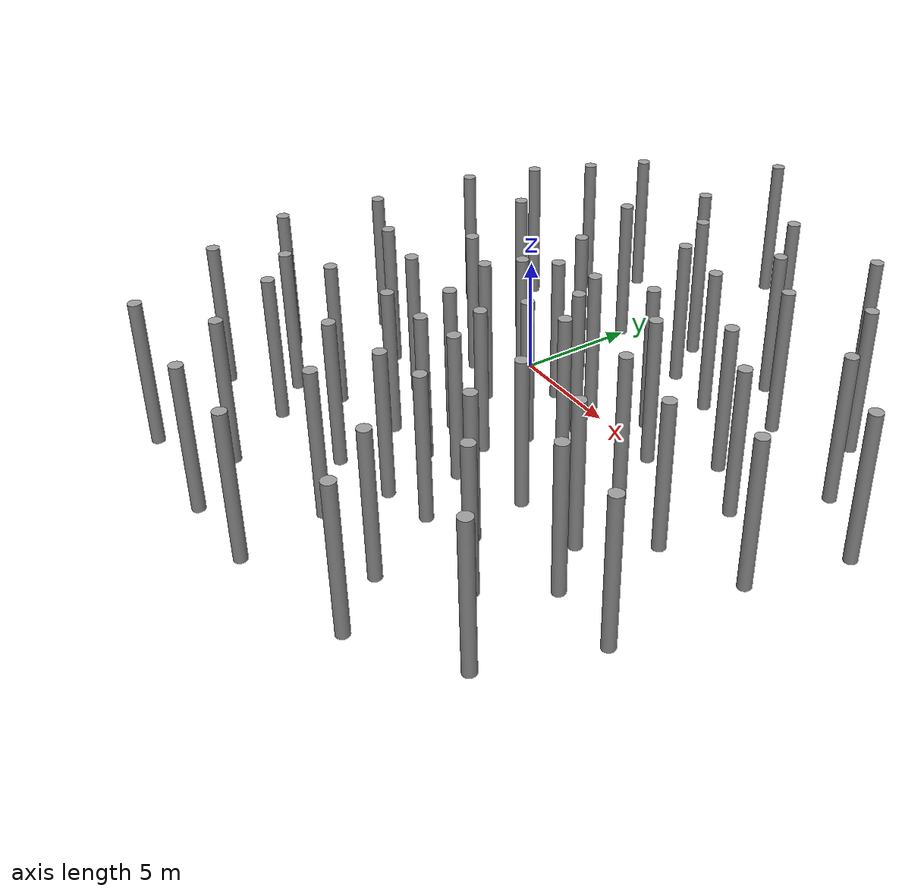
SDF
<?xml version='1.0'?>
<sdf version='1.6'>
  <model name='skog2'>
    <link name='link_0'>
      <inertial>
        <mass>1</mass>
        <inertia>
          <ixx>0.145833</ixx>
          <ixy>0</ixy>
          <ixz>0</ixz>
          <iyy>0.145833</iyy>
          <iyz>0</iyz>
          <izz>0.125</izz>
        </inertia>
        <pose frame=''>0 0 0 0 -0 0</pose>
      </inertial>
      <pose frame=''>-3.56509 -0.045146 0 0 -0 0</pose>
      <gravity>1</gravity>
      <self_collide>0</self_collide>
      <kinematic>0</kinematic>
      <enable_wind>0</enable_wind>
      <visual name='visual'>
        <pose frame=''>0 0 0 0 -0 0</pose>
        <geometry>
          <cylinder>
            <radius>0.3</radius>
            <length>7</length>
          </cylinder>
        </geometry>
        <material>
          <lighting>1</lighting>
          <script>
            <uri>file://media/materials/scripts/gazebo.material</uri>
            <name>Gazebo/Grey</name>
          </script>
          <shader type='vertex'>
            <normal_map>__default__</normal_map>
          </shader>
          <ambient>0.3 0.3 0.3 1</ambient>
          <diffuse>0.7 0.7 0.7 1</diffuse>
          <specular>0.01 0.01 0.01 1</specular>
          <emissive>0 0 0 1</emissive>
        </material>
        <transparency>0</transparency>
        <cast_shadows>1</cast_shadows>
      </visual>
      <collision name='collision'>
        <laser_retro>0</laser_retro>
        <max_contacts>10</max_contacts>
        <pose frame=''>0 0 0 0 -0 0</pose>
        <geometry>
          <cylinder>
            <radius>0.3</radius>
            <length>7</length>
          </cylinder>
        </geometry>
        <surface>
          <friction>
            <ode>
              <mu>1</mu>
              <mu2>1</mu2>
              <fdir1>0 0 0</fdir1>
              <slip1>0</slip1>
              <slip2>0</slip2>
            </ode>
            <torsional>
              <coefficient>1</coefficient>
              <patch_radius>0</patch_radius>
              <surface_radius>0</surface_radius>
              <use_patch_radius>1</use_patch_radius>
              <ode>
                <slip>0</slip>
              </ode>
            </torsional>
          </friction>
          <bounce>
            <restitution_coefficient>0</restitution_coefficient>
            <threshold>1e+06</threshold>
          </bounce>
          <contact>
            <collide_without_contact>0</collide_without_contact>
            <collide_without_contact_bitmask>1</collide_without_contact_bitmask>
            <collide_bitmask>1</collide_bitmask>
            <ode>
              <soft_cfm>0</soft_cfm>
              <soft_erp>0.2</soft_erp>
              <kp>1e+13</kp>
              <kd>1</kd>
              <max_vel>0.01</max_vel>
              <min_depth>0</min_depth>
            </ode>
            <bullet>
              <split_impulse>1</split_impulse>
              <split_impulse_penetration_threshold>-0.01</split_impulse_penetration_threshold>
              <soft_cfm>0</soft_cfm>
              <soft_erp>0.2</soft_erp>
              <kp>1e+13</kp>
              <kd>1</kd>
            </bullet>
          </contact>
        </surface>
      </collision>
    </link>
    <link name='link_0_clone'>
      <inertial>
        <mass>1</mass>
        <inertia>
          <ixx>0.145833</ixx>
          <ixy>0</ixy>
          <ixz>0</ixz>
          <iyy>0.145833</iyy>
          <iyz>0</iyz>
          <izz>0.125</izz>
        </inertia>
        <pose frame=''>0 0 0 0 -0 0</pose>
      </inertial>
      <pose frame=''>-2.97752 1.58068 0 0 -0 0</pose>
      <gravity>1</gravity>
      <self_collide>0</self_collide>
      <kinematic>0</kinematic>
      <enable_wind>0</enable_wind>
      <visual name='visual'>
        <pose frame=''>0 0 0 0 -0 0</pose>
        <geometry>
          <cylinder>
            <radius>0.3</radius>
            <length>7</length>
          </cylinder>
        </geometry>
        <material>
          <lighting>1</lighting>
          <script>
            <uri>file://media/materials/scripts/gazebo.material</uri>
            <name>Gazebo/Grey</name>
          </script>
          <shader type='vertex'>
            <normal_map>__default__</normal_map>
          </shader>
          <ambient>0.3 0.3 0.3 1</ambient>
          <diffuse>0.7 0.7 0.7 1</diffuse>
          <specular>0.01 0.01 0.01 1</specular>
          <emissive>0 0 0 1</emissive>
        </material>
        <transparency>0</transparency>
        <cast_shadows>1</cast_shadows>
      </visual>
      <collision name='collision'>
        <laser_retro>0</laser_retro>
        <max_contacts>10</max_contacts>
        <pose frame=''>0 0 0 0 -0 0</pose>
        <geometry>
          <cylinder>
            <radius>0.3</radius>
            <length>7</length>
          </cylinder>
        </geometry>
        <surface>
          <friction>
            <ode>
              <mu>1</mu>
              <mu2>1</mu2>
              <fdir1>0 0 0</fdir1>
              <slip1>0</slip1>
              <slip2>0</slip2>
            </ode>
            <torsional>
              <coefficient>1</coefficient>
              <patch_radius>0</patch_radius>
              <surface_radius>0</surface_radius>
              <use_patch_radius>1</use_patch_radius>
              <ode>
                <slip>0</slip>
              </ode>
            </torsional>
          </friction>
          <bounce>
            <restitution_coefficient>0</restitution_coefficient>
            <threshold>1e+06</threshold>
          </bounce>
          <contact>
            <collide_without_contact>0</collide_without_contact>
            <collide_without_contact_bitmask>1</collide_without_contact_bitmask>
            <collide_bitmask>1</collide_bitmask>
            <ode>
              <soft_cfm>0</soft_cfm>
              <soft_erp>0.2</soft_erp>
              <kp>1e+13</kp>
              <kd>1</kd>
              <max_vel>0.01</max_vel>
              <min_depth>0</min_depth>
            </ode>
            <bullet>
              <split_impulse>1</split_impulse>
              <split_impulse_penetration_threshold>-0.01</split_impulse_penetration_threshold>
              <soft_cfm>0</soft_cfm>
              <soft_erp>0.2</soft_erp>
              <kp>1e+13</kp>
              <kd>1</kd>
            </bullet>
          </contact>
        </surface>
      </collision>
    </link>
    <link name='link_0_clone_0'>
      <inertial>
        <mass>1</mass>
        <inertia>
          <ixx>0.145833</ixx>
          <ixy>0</ixy>
          <ixz>0</ixz>
          <iyy>0.145833</iyy>
          <iyz>0</iyz>
          <izz>0.125</izz>
        </inertia>
        <pose frame=''>0 0 0 0 -0 0</pose>
      </inertial>
      <pose frame=''>-1.8151 2.73071 0 0 -0 0</pose>
      <gravity>1</gravity>
      <self_collide>0</self_collide>
      <kinematic>0</kinematic>
      <enable_wind>0</enable_wind>
      <visual name='visual'>
        <pose frame=''>0 0 0 0 -0 0</pose>
        <geometry>
          <cylinder>
            <radius>0.3</radius>
            <length>7</length>
          </cylinder>
        </geometry>
        <material>
          <lighting>1</lighting>
          <script>
            <uri>file://media/materials/scripts/gazebo.material</uri>
            <name>Gazebo/Grey</name>
          </script>
          <shader type='vertex'>
            <normal_map>__default__</normal_map>
          </shader>
          <ambient>0.3 0.3 0.3 1</ambient>
          <diffuse>0.7 0.7 0.7 1</diffuse>
          <specular>0.01 0.01 0.01 1</specular>
          <emissive>0 0 0 1</emissive>
        </material>
        <transparency>0</transparency>
        <cast_shadows>1</cast_shadows>
      </visual>
      <collision name='collision'>
        <laser_retro>0</laser_retro>
        <max_contacts>10</max_contacts>
        <pose frame=''>0 0 0 0 -0 0</pose>
        <geometry>
          <cylinder>
            <radius>0.3</radius>
            <length>7</length>
          </cylinder>
        </geometry>
        <surface>
          <friction>
            <ode>
              <mu>1</mu>
              <mu2>1</mu2>
              <fdir1>0 0 0</fdir1>
              <slip1>0</slip1>
              <slip2>0</slip2>
            </ode>
            <torsional>
              <coefficient>1</coefficient>
              <patch_radius>0</patch_radius>
              <surface_radius>0</surface_radius>
              <use_patch_radius>1</use_patch_radius>
              <ode>
                <slip>0</slip>
              </ode>
            </torsional>
          </friction>
          <bounce>
            <restitution_coefficient>0</restitution_coefficient>
            <threshold>1e+06</threshold>
          </bounce>
          <contact>
            <collide_without_contact>0</collide_without_contact>
            <collide_without_contact_bitmask>1</collide_without_contact_bitmask>
            <collide_bitmask>1</collide_bitmask>
            <ode>
              <soft_cfm>0</soft_cfm>
              <soft_erp>0.2</soft_erp>
              <kp>1e+13</kp>
              <kd>1</kd>
              <max_vel>0.01</max_vel>
              <min_depth>0</min_depth>
            </ode>
            <bullet>
              <split_impulse>1</split_impulse>
              <split_impulse_penetration_threshold>-0.01</split_impulse_penetration_threshold>
              <soft_cfm>0</soft_cfm>
              <soft_erp>0.2</soft_erp>
              <kp>1e+13</kp>
              <kd>1</kd>
            </bullet>
          </contact>
        </surface>
      </collision>
    </link>
    <link name='link_0_clone_1'>
      <inertial>
        <mass>1</mass>
        <inertia>
          <ixx>0.145833</ixx>
          <ixy>0</ixy>
          <ixz>0</ixz>
          <iyy>0.145833</iyy>
          <iyz>0</iyz>
          <izz>0.125</izz>
        </inertia>
        <pose frame=''>0 0 0 0 -0 0</pose>
      </inertial>
      <pose frame=''>0.375089 -0.434583 0 0 -0 0</pose>
      <gravity>1</gravity>
      <self_collide>0</self_collide>
      <kinematic>0</kinematic>
      <enable_wind>0</enable_wind>
      <visual name='visual'>
        <pose frame=''>0 0 0 0 -0 0</pose>
        <geometry>
          <cylinder>
            <radius>0.3</radius>
            <length>7</length>
          </cylinder>
        </geometry>
        <material>
          <lighting>1</lighting>
          <script>
            <uri>file://media/materials/scripts/gazebo.material</uri>
            <name>Gazebo/Grey</name>
          </script>
          <shader type='vertex'>
            <normal_map>__default__</normal_map>
          </shader>
          <ambient>0.3 0.3 0.3 1</ambient>
          <diffuse>0.7 0.7 0.7 1</diffuse>
          <specular>0.01 0.01 0.01 1</specular>
          <emissive>0 0 0 1</emissive>
        </material>
        <transparency>0</transparency>
        <cast_shadows>1</cast_shadows>
      </visual>
      <collision name='collision'>
        <laser_retro>0</laser_retro>
        <max_contacts>10</max_contacts>
        <pose frame=''>0 0 0 0 -0 0</pose>
        <geometry>
          <cylinder>
            <radius>0.3</radius>
            <length>7</length>
          </cylinder>
        </geometry>
        <surface>
          <friction>
            <ode>
              <mu>1</mu>
              <mu2>1</mu2>
              <fdir1>0 0 0</fdir1>
              <slip1>0</slip1>
              <slip2>0</slip2>
            </ode>
            <torsional>
              <coefficient>1</coefficient>
              <patch_radius>0</patch_radius>
              <surface_radius>0</surface_radius>
              <use_patch_radius>1</use_patch_radius>
              <ode>
                <slip>0</slip>
              </ode>
            </torsional>
          </friction>
          <bounce>
            <restitution_coefficient>0</restitution_coefficient>
            <threshold>1e+06</threshold>
          </bounce>
          <contact>
            <collide_without_contact>0</collide_without_contact>
            <collide_without_contact_bitmask>1</collide_without_contact_bitmask>
            <collide_bitmask>1</collide_bitmask>
            <ode>
              <soft_cfm>0</soft_cfm>
              <soft_erp>0.2</soft_erp>
              <kp>1e+13</kp>
              <kd>1</kd>
              <max_vel>0.01</max_vel>
              <min_depth>0</min_depth>
            </ode>
            <bullet>
              <split_impulse>1</split_impulse>
              <split_impulse_penetration_threshold>-0.01</split_impulse_penetration_threshold>
              <soft_cfm>0</soft_cfm>
              <soft_erp>0.2</soft_erp>
              <kp>1e+13</kp>
              <kd>1</kd>
            </bullet>
          </contact>
        </surface>
      </collision>
    </link>
    <link name='link_0_clone_10'>
      <inertial>
        <mass>1</mass>
        <inertia>
          <ixx>0.145833</ixx>
          <ixy>0</ixy>
          <ixz>0</ixz>
          <iyy>0.145833</iyy>
          <iyz>0</iyz>
          <izz>0.125</izz>
        </inertia>
        <pose frame=''>0 0 0 0 -0 0</pose>
      </inertial>
      <pose frame=''>2.50519 4.65138 0 0 -0 0</pose>
      <gravity>1</gravity>
      <self_collide>0</self_collide>
      <kinematic>0</kinematic>
      <enable_wind>0</enable_wind>
      <visual name='visual'>
        <pose frame=''>0 0 0 0 -0 0</pose>
        <geometry>
          <cylinder>
            <radius>0.3</radius>
            <length>7</length>
          </cylinder>
        </geometry>
        <material>
          <lighting>1</lighting>
          <script>
            <uri>file://media/materials/scripts/gazebo.material</uri>
            <name>Gazebo/Grey</name>
          </script>
          <shader type='vertex'>
            <normal_map>__default__</normal_map>
          </shader>
          <ambient>0.3 0.3 0.3 1</ambient>
          <diffuse>0.7 0.7 0.7 1</diffuse>
          <specular>0.01 0.01 0.01 1</specular>
          <emissive>0 0 0 1</emissive>
        </material>
        <transparency>0</transparency>
        <cast_shadows>1</cast_shadows>
      </visual>
      <collision name='collision'>
        <laser_retro>0</laser_retro>
        <max_contacts>10</max_contacts>
        <pose frame=''>0 0 0 0 -0 0</pose>
        <geometry>
          <cylinder>
            <radius>0.3</radius>
            <length>7</length>
          </cylinder>
        </geometry>
        <surface>
          <friction>
            <ode>
              <mu>1</mu>
              <mu2>1</mu2>
              <fdir1>0 0 0</fdir1>
              <slip1>0</slip1>
              <slip2>0</slip2>
            </ode>
            <torsional>
              <coefficient>1</coefficient>
              <patch_radius>0</patch_radius>
              <surface_radius>0</surface_radius>
              <use_patch_radius>1</use_patch_radius>
              <ode>
                <slip>0</slip>
              </ode>
            </torsional>
          </friction>
          <bounce>
            <restitution_coefficient>0</restitution_coefficient>
            <threshold>1e+06</threshold>
          </bounce>
          <contact>
            <collide_without_contact>0</collide_without_contact>
            <collide_without_contact_bitmask>1</collide_without_contact_bitmask>
            <collide_bitmask>1</collide_bitmask>
            <ode>
              <soft_cfm>0</soft_cfm>
              <soft_erp>0.2</soft_erp>
              <kp>1e+13</kp>
              <kd>1</kd>
              <max_vel>0.01</max_vel>
              <min_depth>0</min_depth>
            </ode>
            <bullet>
              <split_impulse>1</split_impulse>
              <split_impulse_penetration_threshold>-0.01</split_impulse_penetration_threshold>
              <soft_cfm>0</soft_cfm>
              <soft_erp>0.2</soft_erp>
              <kp>1e+13</kp>
              <kd>1</kd>
            </bullet>
          </contact>
        </surface>
      </collision>
    </link>
    <link name='link_0_clone_11'>
      <inertial>
        <mass>1</mass>
        <inertia>
          <ixx>0.145833</ixx>
          <ixy>0</ixy>
          <ixz>0</ixz>
          <iyy>0.145833</iyy>
          <iyz>0</iyz>
          <izz>0.125</izz>
        </inertia>
        <pose frame=''>0 0 0 0 -0 0</pose>
      </inertial>
      <pose frame=''>2.42666 0.027375 0 0 -0 0</pose>
      <gravity>1</gravity>
      <self_collide>0</self_collide>
      <kinematic>0</kinematic>
      <enable_wind>0</enable_wind>
      <visual name='visual'>
        <pose frame=''>0 0 0 0 -0 0</pose>
        <geometry>
          <cylinder>
            <radius>0.3</radius>
            <length>7</length>
          </cylinder>
        </geometry>
        <material>
          <lighting>1</lighting>
          <script>
            <uri>file://media/materials/scripts/gazebo.material</uri>
            <name>Gazebo/Grey</name>
          </script>
          <shader type='vertex'>
            <normal_map>__default__</normal_map>
          </shader>
          <ambient>0.3 0.3 0.3 1</ambient>
          <diffuse>0.7 0.7 0.7 1</diffuse>
          <specular>0.01 0.01 0.01 1</specular>
          <emissive>0 0 0 1</emissive>
        </material>
        <transparency>0</transparency>
        <cast_shadows>1</cast_shadows>
      </visual>
      <collision name='collision'>
        <laser_retro>0</laser_retro>
        <max_contacts>10</max_contacts>
        <pose frame=''>0 0 0 0 -0 0</pose>
        <geometry>
          <cylinder>
            <radius>0.3</radius>
            <length>7</length>
          </cylinder>
        </geometry>
        <surface>
          <friction>
            <ode>
              <mu>1</mu>
              <mu2>1</mu2>
              <fdir1>0 0 0</fdir1>
              <slip1>0</slip1>
              <slip2>0</slip2>
            </ode>
            <torsional>
              <coefficient>1</coefficient>
              <patch_radius>0</patch_radius>
              <surface_radius>0</surface_radius>
              <use_patch_radius>1</use_patch_radius>
              <ode>
                <slip>0</slip>
              </ode>
            </torsional>
          </friction>
          <bounce>
            <restitution_coefficient>0</restitution_coefficient>
            <threshold>1e+06</threshold>
          </bounce>
          <contact>
            <collide_without_contact>0</collide_without_contact>
            <collide_without_contact_bitmask>1</collide_without_contact_bitmask>
            <collide_bitmask>1</collide_bitmask>
            <ode>
              <soft_cfm>0</soft_cfm>
              <soft_erp>0.2</soft_erp>
              <kp>1e+13</kp>
              <kd>1</kd>
              <max_vel>0.01</max_vel>
              <min_depth>0</min_depth>
            </ode>
            <bullet>
              <split_impulse>1</split_impulse>
              <split_impulse_penetration_threshold>-0.01</split_impulse_penetration_threshold>
              <soft_cfm>0</soft_cfm>
              <soft_erp>0.2</soft_erp>
              <kp>1e+13</kp>
              <kd>1</kd>
            </bullet>
          </contact>
        </surface>
      </collision>
    </link>
    <link name='link_0_clone_12'>
      <inertial>
        <mass>1</mass>
        <inertia>
          <ixx>0.145833</ixx>
          <ixy>0</ixy>
          <ixz>0</ixz>
          <iyy>0.145833</iyy>
          <iyz>0</iyz>
          <izz>0.125</izz>
        </inertia>
        <pose frame=''>0 0 0 0 -0 0</pose>
      </inertial>
      <pose frame=''>-1.05106 -4.80766 0 0 -0 0</pose>
      <gravity>1</gravity>
      <self_collide>0</self_collide>
      <kinematic>0</kinematic>
      <enable_wind>0</enable_wind>
      <visual name='visual'>
        <pose frame=''>0 0 0 0 -0 0</pose>
        <geometry>
          <cylinder>
            <radius>0.3</radius>
            <length>7</length>
          </cylinder>
        </geometry>
        <material>
          <lighting>1</lighting>
          <script>
            <uri>file://media/materials/scripts/gazebo.material</uri>
            <name>Gazebo/Grey</name>
          </script>
          <shader type='vertex'>
            <normal_map>__default__</normal_map>
          </shader>
          <ambient>0.3 0.3 0.3 1</ambient>
          <diffuse>0.7 0.7 0.7 1</diffuse>
          <specular>0.01 0.01 0.01 1</specular>
          <emissive>0 0 0 1</emissive>
        </material>
        <transparency>0</transparency>
        <cast_shadows>1</cast_shadows>
      </visual>
      <collision name='collision'>
        <laser_retro>0</laser_retro>
        <max_contacts>10</max_contacts>
        <pose frame=''>0 0 0 0 -0 0</pose>
        <geometry>
          <cylinder>
            <radius>0.3</radius>
            <length>7</length>
          </cylinder>
        </geometry>
        <surface>
          <friction>
            <ode>
              <mu>1</mu>
              <mu2>1</mu2>
              <fdir1>0 0 0</fdir1>
              <slip1>0</slip1>
              <slip2>0</slip2>
            </ode>
            <torsional>
              <coefficient>1</coefficient>
              <patch_radius>0</patch_radius>
              <surface_radius>0</surface_radius>
              <use_patch_radius>1</use_patch_radius>
              <ode>
                <slip>0</slip>
              </ode>
            </torsional>
          </friction>
          <bounce>
            <restitution_coefficient>0</restitution_coefficient>
            <threshold>1e+06</threshold>
          </bounce>
          <contact>
            <collide_without_contact>0</collide_without_contact>
            <collide_without_contact_bitmask>1</collide_without_contact_bitmask>
            <collide_bitmask>1</collide_bitmask>
            <ode>
              <soft_cfm>0</soft_cfm>
              <soft_erp>0.2</soft_erp>
              <kp>1e+13</kp>
              <kd>1</kd>
              <max_vel>0.01</max_vel>
              <min_depth>0</min_depth>
            </ode>
            <bullet>
              <split_impulse>1</split_impulse>
              <split_impulse_penetration_threshold>-0.01</split_impulse_penetration_threshold>
              <soft_cfm>0</soft_cfm>
              <soft_erp>0.2</soft_erp>
              <kp>1e+13</kp>
              <kd>1</kd>
            </bullet>
          </contact>
        </surface>
      </collision>
    </link>
    <link name='link_0_clone_13'>
      <inertial>
        <mass>1</mass>
        <inertia>
          <ixx>0.145833</ixx>
          <ixy>0</ixy>
          <ixz>0</ixz>
          <iyy>0.145833</iyy>
          <iyz>0</iyz>
          <izz>0.125</izz>
        </inertia>
        <pose frame=''>0 0 0 0 -0 0</pose>
      </inertial>
      <pose frame=''>1.00037 -4.4509 0 0 -0 0</pose>
      <gravity>1</gravity>
      <self_collide>0</self_collide>
      <kinematic>0</kinematic>
      <enable_wind>0</enable_wind>
      <visual name='visual'>
        <pose frame=''>0 0 0 0 -0 0</pose>
        <geometry>
          <cylinder>
            <radius>0.3</radius>
            <length>7</length>
          </cylinder>
        </geometry>
        <material>
          <lighting>1</lighting>
          <script>
            <uri>file://media/materials/scripts/gazebo.material</uri>
            <name>Gazebo/Grey</name>
          </script>
          <shader type='vertex'>
            <normal_map>__default__</normal_map>
          </shader>
          <ambient>0.3 0.3 0.3 1</ambient>
          <diffuse>0.7 0.7 0.7 1</diffuse>
          <specular>0.01 0.01 0.01 1</specular>
          <emissive>0 0 0 1</emissive>
        </material>
        <transparency>0</transparency>
        <cast_shadows>1</cast_shadows>
      </visual>
      <collision name='collision'>
        <laser_retro>0</laser_retro>
        <max_contacts>10</max_contacts>
        <pose frame=''>0 0 0 0 -0 0</pose>
        <geometry>
          <cylinder>
            <radius>0.3</radius>
            <length>7</length>
          </cylinder>
        </geometry>
        <surface>
          <friction>
            <ode>
              <mu>1</mu>
              <mu2>1</mu2>
              <fdir1>0 0 0</fdir1>
              <slip1>0</slip1>
              <slip2>0</slip2>
            </ode>
            <torsional>
              <coefficient>1</coefficient>
              <patch_radius>0</patch_radius>
              <surface_radius>0</surface_radius>
              <use_patch_radius>1</use_patch_radius>
              <ode>
                <slip>0</slip>
              </ode>
            </torsional>
          </friction>
          <bounce>
            <restitution_coefficient>0</restitution_coefficient>
            <threshold>1e+06</threshold>
          </bounce>
          <contact>
            <collide_without_contact>0</collide_without_contact>
            <collide_without_contact_bitmask>1</collide_without_contact_bitmask>
            <collide_bitmask>1</collide_bitmask>
            <ode>
              <soft_cfm>0</soft_cfm>
              <soft_erp>0.2</soft_erp>
              <kp>1e+13</kp>
              <kd>1</kd>
              <max_vel>0.01</max_vel>
              <min_depth>0</min_depth>
            </ode>
            <bullet>
              <split_impulse>1</split_impulse>
              <split_impulse_penetration_threshold>-0.01</split_impulse_penetration_threshold>
              <soft_cfm>0</soft_cfm>
              <soft_erp>0.2</soft_erp>
              <kp>1e+13</kp>
              <kd>1</kd>
            </bullet>
          </contact>
        </surface>
      </collision>
    </link>
    <link name='link_0_clone_14'>
      <inertial>
        <mass>1</mass>
        <inertia>
          <ixx>0.145833</ixx>
          <ixy>0</ixy>
          <ixz>0</ixz>
          <iyy>0.145833</iyy>
          <iyz>0</iyz>
          <izz>0.125</izz>
        </inertia>
        <pose frame=''>0 0 0 0 -0 0</pose>
      </inertial>
      <pose frame=''>4.10784 -3.25885 0 0 -0 0</pose>
      <gravity>1</gravity>
      <self_collide>0</self_collide>
      <kinematic>0</kinematic>
      <enable_wind>0</enable_wind>
      <visual name='visual'>
        <pose frame=''>0 0 0 0 -0 0</pose>
        <geometry>
          <cylinder>
            <radius>0.3</radius>
            <length>7</length>
          </cylinder>
        </geometry>
        <material>
          <lighting>1</lighting>
          <script>
            <uri>file://media/materials/scripts/gazebo.material</uri>
            <name>Gazebo/Grey</name>
          </script>
          <shader type='vertex'>
            <normal_map>__default__</normal_map>
          </shader>
          <ambient>0.3 0.3 0.3 1</ambient>
          <diffuse>0.7 0.7 0.7 1</diffuse>
          <specular>0.01 0.01 0.01 1</specular>
          <emissive>0 0 0 1</emissive>
        </material>
        <transparency>0</transparency>
        <cast_shadows>1</cast_shadows>
      </visual>
      <collision name='collision'>
        <laser_retro>0</laser_retro>
        <max_contacts>10</max_contacts>
        <pose frame=''>0 0 0 0 -0 0</pose>
        <geometry>
          <cylinder>
            <radius>0.3</radius>
            <length>7</length>
          </cylinder>
        </geometry>
        <surface>
          <friction>
            <ode>
              <mu>1</mu>
              <mu2>1</mu2>
              <fdir1>0 0 0</fdir1>
              <slip1>0</slip1>
              <slip2>0</slip2>
            </ode>
            <torsional>
              <coefficient>1</coefficient>
              <patch_radius>0</patch_radius>
              <surface_radius>0</surface_radius>
              <use_patch_radius>1</use_patch_radius>
              <ode>
                <slip>0</slip>
              </ode>
            </torsional>
          </friction>
          <bounce>
            <restitution_coefficient>0</restitution_coefficient>
            <threshold>1e+06</threshold>
          </bounce>
          <contact>
            <collide_without_contact>0</collide_without_contact>
            <collide_without_contact_bitmask>1</collide_without_contact_bitmask>
            <collide_bitmask>1</collide_bitmask>
            <ode>
              <soft_cfm>0</soft_cfm>
              <soft_erp>0.2</soft_erp>
              <kp>1e+13</kp>
              <kd>1</kd>
              <max_vel>0.01</max_vel>
              <min_depth>0</min_depth>
            </ode>
            <bullet>
              <split_impulse>1</split_impulse>
              <split_impulse_penetration_threshold>-0.01</split_impulse_penetration_threshold>
              <soft_cfm>0</soft_cfm>
              <soft_erp>0.2</soft_erp>
              <kp>1e+13</kp>
              <kd>1</kd>
            </bullet>
          </contact>
        </surface>
      </collision>
    </link>
    <link name='link_0_clone_15'>
      <inertial>
        <mass>1</mass>
        <inertia>
          <ixx>0.145833</ixx>
          <ixy>0</ixy>
          <ixz>0</ixz>
          <iyy>0.145833</iyy>
          <iyz>0</iyz>
          <izz>0.125</izz>
        </inertia>
        <pose frame=''>0 0 0 0 -0 0</pose>
      </inertial>
      <pose frame=''>6.12409 0.304074 0 0 -0 0</pose>
      <gravity>1</gravity>
      <self_collide>0</self_collide>
      <kinematic>0</kinematic>
      <enable_wind>0</enable_wind>
      <visual name='visual'>
        <pose frame=''>0 0 0 0 -0 0</pose>
        <geometry>
          <cylinder>
            <radius>0.3</radius>
            <length>7</length>
          </cylinder>
        </geometry>
        <material>
          <lighting>1</lighting>
          <script>
            <uri>file://media/materials/scripts/gazebo.material</uri>
            <name>Gazebo/Grey</name>
          </script>
          <shader type='vertex'>
            <normal_map>__default__</normal_map>
          </shader>
          <ambient>0.3 0.3 0.3 1</ambient>
          <diffuse>0.7 0.7 0.7 1</diffuse>
          <specular>0.01 0.01 0.01 1</specular>
          <emissive>0 0 0 1</emissive>
        </material>
        <transparency>0</transparency>
        <cast_shadows>1</cast_shadows>
      </visual>
      <collision name='collision'>
        <laser_retro>0</laser_retro>
        <max_contacts>10</max_contacts>
        <pose frame=''>0 0 0 0 -0 0</pose>
        <geometry>
          <cylinder>
            <radius>0.3</radius>
            <length>7</length>
          </cylinder>
        </geometry>
        <surface>
          <friction>
            <ode>
              <mu>1</mu>
              <mu2>1</mu2>
              <fdir1>0 0 0</fdir1>
              <slip1>0</slip1>
              <slip2>0</slip2>
            </ode>
            <torsional>
              <coefficient>1</coefficient>
              <patch_radius>0</patch_radius>
              <surface_radius>0</surface_radius>
              <use_patch_radius>1</use_patch_radius>
              <ode>
                <slip>0</slip>
              </ode>
            </torsional>
          </friction>
          <bounce>
            <restitution_coefficient>0</restitution_coefficient>
            <threshold>1e+06</threshold>
          </bounce>
          <contact>
            <collide_without_contact>0</collide_without_contact>
            <collide_without_contact_bitmask>1</collide_without_contact_bitmask>
            <collide_bitmask>1</collide_bitmask>
            <ode>
              <soft_cfm>0</soft_cfm>
              <soft_erp>0.2</soft_erp>
              <kp>1e+13</kp>
              <kd>1</kd>
              <max_vel>0.01</max_vel>
              <min_depth>0</min_depth>
            </ode>
            <bullet>
              <split_impulse>1</split_impulse>
              <split_impulse_penetration_threshold>-0.01</split_impulse_penetration_threshold>
              <soft_cfm>0</soft_cfm>
              <soft_erp>0.2</soft_erp>
              <kp>1e+13</kp>
              <kd>1</kd>
            </bullet>
          </contact>
        </surface>
      </collision>
    </link>
    <link name='link_0_clone_16'>
      <inertial>
        <mass>1</mass>
        <inertia>
          <ixx>0.145833</ixx>
          <ixy>0</ixy>
          <ixz>0</ixz>
          <iyy>0.145833</iyy>
          <iyz>0</iyz>
          <izz>0.125</izz>
        </inertia>
        <pose frame=''>0 0 0 0 -0 0</pose>
      </inertial>
      <pose frame=''>6.83354 5.18672 0 0 -0 0</pose>
      <gravity>1</gravity>
      <self_collide>0</self_collide>
      <kinematic>0</kinematic>
      <enable_wind>0</enable_wind>
      <visual name='visual'>
        <pose frame=''>0 0 0 0 -0 0</pose>
        <geometry>
          <cylinder>
            <radius>0.3</radius>
            <length>7</length>
          </cylinder>
        </geometry>
        <material>
          <lighting>1</lighting>
          <script>
            <uri>file://media/materials/scripts/gazebo.material</uri>
            <name>Gazebo/Grey</name>
          </script>
          <shader type='vertex'>
            <normal_map>__default__</normal_map>
          </shader>
          <ambient>0.3 0.3 0.3 1</ambient>
          <diffuse>0.7 0.7 0.7 1</diffuse>
          <specular>0.01 0.01 0.01 1</specular>
          <emissive>0 0 0 1</emissive>
        </material>
        <transparency>0</transparency>
        <cast_shadows>1</cast_shadows>
      </visual>
      <collision name='collision'>
        <laser_retro>0</laser_retro>
        <max_contacts>10</max_contacts>
        <pose frame=''>0 0 0 0 -0 0</pose>
        <geometry>
          <cylinder>
            <radius>0.3</radius>
            <length>7</length>
          </cylinder>
        </geometry>
        <surface>
          <friction>
            <ode>
              <mu>1</mu>
              <mu2>1</mu2>
              <fdir1>0 0 0</fdir1>
              <slip1>0</slip1>
              <slip2>0</slip2>
            </ode>
            <torsional>
              <coefficient>1</coefficient>
              <patch_radius>0</patch_radius>
              <surface_radius>0</surface_radius>
              <use_patch_radius>1</use_patch_radius>
              <ode>
                <slip>0</slip>
              </ode>
            </torsional>
          </friction>
          <bounce>
            <restitution_coefficient>0</restitution_coefficient>
            <threshold>1e+06</threshold>
          </bounce>
          <contact>
            <collide_without_contact>0</collide_without_contact>
            <collide_without_contact_bitmask>1</collide_without_contact_bitmask>
            <collide_bitmask>1</collide_bitmask>
            <ode>
              <soft_cfm>0</soft_cfm>
              <soft_erp>0.2</soft_erp>
              <kp>1e+13</kp>
              <kd>1</kd>
              <max_vel>0.01</max_vel>
              <min_depth>0</min_depth>
            </ode>
            <bullet>
              <split_impulse>1</split_impulse>
              <split_impulse_penetration_threshold>-0.01</split_impulse_penetration_threshold>
              <soft_cfm>0</soft_cfm>
              <soft_erp>0.2</soft_erp>
              <kp>1e+13</kp>
              <kd>1</kd>
            </bullet>
          </contact>
        </surface>
      </collision>
    </link>
    <link name='link_0_clone_17'>
      <inertial>
        <mass>1</mass>
        <inertia>
          <ixx>0.145833</ixx>
          <ixy>0</ixy>
          <ixz>0</ixz>
          <iyy>0.145833</iyy>
          <iyz>0</iyz>
          <izz>0.125</izz>
        </inertia>
        <pose frame=''>0 0 0 0 -0 0</pose>
      </inertial>
      <pose frame=''>2.8537 7.8375 0 0 -0 0</pose>
      <gravity>1</gravity>
      <self_collide>0</self_collide>
      <kinematic>0</kinematic>
      <enable_wind>0</enable_wind>
      <visual name='visual'>
        <pose frame=''>0 0 0 0 -0 0</pose>
        <geometry>
          <cylinder>
            <radius>0.3</radius>
            <length>7</length>
          </cylinder>
        </geometry>
        <material>
          <lighting>1</lighting>
          <script>
            <uri>file://media/materials/scripts/gazebo.material</uri>
            <name>Gazebo/Grey</name>
          </script>
          <shader type='vertex'>
            <normal_map>__default__</normal_map>
          </shader>
          <ambient>0.3 0.3 0.3 1</ambient>
          <diffuse>0.7 0.7 0.7 1</diffuse>
          <specular>0.01 0.01 0.01 1</specular>
          <emissive>0 0 0 1</emissive>
        </material>
        <transparency>0</transparency>
        <cast_shadows>1</cast_shadows>
      </visual>
      <collision name='collision'>
        <laser_retro>0</laser_retro>
        <max_contacts>10</max_contacts>
        <pose frame=''>0 0 0 0 -0 0</pose>
        <geometry>
          <cylinder>
            <radius>0.3</radius>
            <length>7</length>
          </cylinder>
        </geometry>
        <surface>
          <friction>
            <ode>
              <mu>1</mu>
              <mu2>1</mu2>
              <fdir1>0 0 0</fdir1>
              <slip1>0</slip1>
              <slip2>0</slip2>
            </ode>
            <torsional>
              <coefficient>1</coefficient>
              <patch_radius>0</patch_radius>
              <surface_radius>0</surface_radius>
              <use_patch_radius>1</use_patch_radius>
              <ode>
                <slip>0</slip>
              </ode>
            </torsional>
          </friction>
          <bounce>
            <restitution_coefficient>0</restitution_coefficient>
            <threshold>1e+06</threshold>
          </bounce>
          <contact>
            <collide_without_contact>0</collide_without_contact>
            <collide_without_contact_bitmask>1</collide_without_contact_bitmask>
            <collide_bitmask>1</collide_bitmask>
            <ode>
              <soft_cfm>0</soft_cfm>
              <soft_erp>0.2</soft_erp>
              <kp>1e+13</kp>
              <kd>1</kd>
              <max_vel>0.01</max_vel>
              <min_depth>0</min_depth>
            </ode>
            <bullet>
              <split_impulse>1</split_impulse>
              <split_impulse_penetration_threshold>-0.01</split_impulse_penetration_threshold>
              <soft_cfm>0</soft_cfm>
              <soft_erp>0.2</soft_erp>
              <kp>1e+13</kp>
              <kd>1</kd>
            </bullet>
          </contact>
        </surface>
      </collision>
    </link>
    <link name='link_0_clone_18'>
      <inertial>
        <mass>1</mass>
        <inertia>
          <ixx>0.145833</ixx>
          <ixy>0</ixy>
          <ixz>0</ixz>
          <iyy>0.145833</iyy>
          <iyz>0</iyz>
          <izz>0.125</izz>
        </inertia>
        <pose frame=''>0 0 0 0 -0 0</pose>
      </inertial>
      <pose frame=''>0.071763 8.4831 0 0 -0 0</pose>
      <gravity>1</gravity>
      <self_collide>0</self_collide>
      <kinematic>0</kinematic>
      <enable_wind>0</enable_wind>
      <visual name='visual'>
        <pose frame=''>0 0 0 0 -0 0</pose>
        <geometry>
          <cylinder>
            <radius>0.3</radius>
            <length>7</length>
          </cylinder>
        </geometry>
        <material>
          <lighting>1</lighting>
          <script>
            <uri>file://media/materials/scripts/gazebo.material</uri>
            <name>Gazebo/Grey</name>
          </script>
          <shader type='vertex'>
            <normal_map>__default__</normal_map>
          </shader>
          <ambient>0.3 0.3 0.3 1</ambient>
          <diffuse>0.7 0.7 0.7 1</diffuse>
          <specular>0.01 0.01 0.01 1</specular>
          <emissive>0 0 0 1</emissive>
        </material>
        <transparency>0</transparency>
        <cast_shadows>1</cast_shadows>
      </visual>
      <collision name='collision'>
        <laser_retro>0</laser_retro>
        <max_contacts>10</max_contacts>
        <pose frame=''>0 0 0 0 -0 0</pose>
        <geometry>
          <cylinder>
            <radius>0.3</radius>
            <length>7</length>
          </cylinder>
        </geometry>
        <surface>
          <friction>
            <ode>
              <mu>1</mu>
              <mu2>1</mu2>
              <fdir1>0 0 0</fdir1>
              <slip1>0</slip1>
              <slip2>0</slip2>
            </ode>
            <torsional>
              <coefficient>1</coefficient>
              <patch_radius>0</patch_radius>
              <surface_radius>0</surface_radius>
              <use_patch_radius>1</use_patch_radius>
              <ode>
                <slip>0</slip>
              </ode>
            </torsional>
          </friction>
          <bounce>
            <restitution_coefficient>0</restitution_coefficient>
            <threshold>1e+06</threshold>
          </bounce>
          <contact>
            <collide_without_contact>0</collide_without_contact>
            <collide_without_contact_bitmask>1</collide_without_contact_bitmask>
            <collide_bitmask>1</collide_bitmask>
            <ode>
              <soft_cfm>0</soft_cfm>
              <soft_erp>0.2</soft_erp>
              <kp>1e+13</kp>
              <kd>1</kd>
              <max_vel>0.01</max_vel>
              <min_depth>0</min_depth>
            </ode>
            <bullet>
              <split_impulse>1</split_impulse>
              <split_impulse_penetration_threshold>-0.01</split_impulse_penetration_threshold>
              <soft_cfm>0</soft_cfm>
              <soft_erp>0.2</soft_erp>
              <kp>1e+13</kp>
              <kd>1</kd>
            </bullet>
          </contact>
        </surface>
      </collision>
    </link>
    <link name='link_0_clone_19'>
      <inertial>
        <mass>1</mass>
        <inertia>
          <ixx>0.145833</ixx>
          <ixy>0</ixy>
          <ixz>0</ixz>
          <iyy>0.145833</iyy>
          <iyz>0</iyz>
          <izz>0.125</izz>
        </inertia>
        <pose frame=''>0 0 0 0 -0 0</pose>
      </inertial>
      <pose frame=''>-4.78843 8.93534 0 0 -0 0</pose>
      <gravity>1</gravity>
      <self_collide>0</self_collide>
      <kinematic>0</kinematic>
      <enable_wind>0</enable_wind>
      <visual name='visual'>
        <pose frame=''>0 0 0 0 -0 0</pose>
        <geometry>
          <cylinder>
            <radius>0.3</radius>
            <length>7</length>
          </cylinder>
        </geometry>
        <material>
          <lighting>1</lighting>
          <script>
            <uri>file://media/materials/scripts/gazebo.material</uri>
            <name>Gazebo/Grey</name>
          </script>
          <shader type='vertex'>
            <normal_map>__default__</normal_map>
          </shader>
          <ambient>0.3 0.3 0.3 1</ambient>
          <diffuse>0.7 0.7 0.7 1</diffuse>
          <specular>0.01 0.01 0.01 1</specular>
          <emissive>0 0 0 1</emissive>
        </material>
        <transparency>0</transparency>
        <cast_shadows>1</cast_shadows>
      </visual>
      <collision name='collision'>
        <laser_retro>0</laser_retro>
        <max_contacts>10</max_contacts>
        <pose frame=''>0 0 0 0 -0 0</pose>
        <geometry>
          <cylinder>
            <radius>0.3</radius>
            <length>7</length>
          </cylinder>
        </geometry>
        <surface>
          <friction>
            <ode>
              <mu>1</mu>
              <mu2>1</mu2>
              <fdir1>0 0 0</fdir1>
              <slip1>0</slip1>
              <slip2>0</slip2>
            </ode>
            <torsional>
              <coefficient>1</coefficient>
              <patch_radius>0</patch_radius>
              <surface_radius>0</surface_radius>
              <use_patch_radius>1</use_patch_radius>
              <ode>
                <slip>0</slip>
              </ode>
            </torsional>
          </friction>
          <bounce>
            <restitution_coefficient>0</restitution_coefficient>
            <threshold>1e+06</threshold>
          </bounce>
          <contact>
            <collide_without_contact>0</collide_without_contact>
            <collide_without_contact_bitmask>1</collide_without_contact_bitmask>
            <collide_bitmask>1</collide_bitmask>
            <ode>
              <soft_cfm>0</soft_cfm>
              <soft_erp>0.2</soft_erp>
              <kp>1e+13</kp>
              <kd>1</kd>
              <max_vel>0.01</max_vel>
              <min_depth>0</min_depth>
            </ode>
            <bullet>
              <split_impulse>1</split_impulse>
              <split_impulse_penetration_threshold>-0.01</split_impulse_penetration_threshold>
              <soft_cfm>0</soft_cfm>
              <soft_erp>0.2</soft_erp>
              <kp>1e+13</kp>
              <kd>1</kd>
            </bullet>
          </contact>
        </surface>
      </collision>
    </link>
    <link name='link_0_clone_2'>
      <inertial>
        <mass>1</mass>
        <inertia>
          <ixx>0.145833</ixx>
          <ixy>0</ixy>
          <ixz>0</ixz>
          <iyy>0.145833</iyy>
          <iyz>0</iyz>
          <izz>0.125</izz>
        </inertia>
        <pose frame=''>0 0 0 0 -0 0</pose>
      </inertial>
      <pose frame=''>1.0178 1.76909 0 0 -0 0</pose>
      <gravity>1</gravity>
      <self_collide>0</self_collide>
      <kinematic>0</kinematic>
      <enable_wind>0</enable_wind>
      <visual name='visual'>
        <pose frame=''>0 0 0 0 -0 0</pose>
        <geometry>
          <cylinder>
            <radius>0.3</radius>
            <length>7</length>
          </cylinder>
        </geometry>
        <material>
          <lighting>1</lighting>
          <script>
            <uri>file://media/materials/scripts/gazebo.material</uri>
            <name>Gazebo/Grey</name>
          </script>
          <shader type='vertex'>
            <normal_map>__default__</normal_map>
          </shader>
          <ambient>0.3 0.3 0.3 1</ambient>
          <diffuse>0.7 0.7 0.7 1</diffuse>
          <specular>0.01 0.01 0.01 1</specular>
          <emissive>0 0 0 1</emissive>
        </material>
        <transparency>0</transparency>
        <cast_shadows>1</cast_shadows>
      </visual>
      <collision name='collision'>
        <laser_retro>0</laser_retro>
        <max_contacts>10</max_contacts>
        <pose frame=''>0 0 0 0 -0 0</pose>
        <geometry>
          <cylinder>
            <radius>0.3</radius>
            <length>7</length>
          </cylinder>
        </geometry>
        <surface>
          <friction>
            <ode>
              <mu>1</mu>
              <mu2>1</mu2>
              <fdir1>0 0 0</fdir1>
              <slip1>0</slip1>
              <slip2>0</slip2>
            </ode>
            <torsional>
              <coefficient>1</coefficient>
              <patch_radius>0</patch_radius>
              <surface_radius>0</surface_radius>
              <use_patch_radius>1</use_patch_radius>
              <ode>
                <slip>0</slip>
              </ode>
            </torsional>
          </friction>
          <bounce>
            <restitution_coefficient>0</restitution_coefficient>
            <threshold>1e+06</threshold>
          </bounce>
          <contact>
            <collide_without_contact>0</collide_without_contact>
            <collide_without_contact_bitmask>1</collide_without_contact_bitmask>
            <collide_bitmask>1</collide_bitmask>
            <ode>
              <soft_cfm>0</soft_cfm>
              <soft_erp>0.2</soft_erp>
              <kp>1e+13</kp>
              <kd>1</kd>
              <max_vel>0.01</max_vel>
              <min_depth>0</min_depth>
            </ode>
            <bullet>
              <split_impulse>1</split_impulse>
              <split_impulse_penetration_threshold>-0.01</split_impulse_penetration_threshold>
              <soft_cfm>0</soft_cfm>
              <soft_erp>0.2</soft_erp>
              <kp>1e+13</kp>
              <kd>1</kd>
            </bullet>
          </contact>
        </surface>
      </collision>
    </link>
    <link name='link_0_clone_20'>
      <inertial>
        <mass>1</mass>
        <inertia>
          <ixx>0.145833</ixx>
          <ixy>0</ixy>
          <ixz>0</ixz>
          <iyy>0.145833</iyy>
          <iyz>0</iyz>
          <izz>0.125</izz>
        </inertia>
        <pose frame=''>0 0 0 0 -0 0</pose>
      </inertial>
      <pose frame=''>-8.199 5.0595 0 0 -0 0</pose>
      <gravity>1</gravity>
      <self_collide>0</self_collide>
      <kinematic>0</kinematic>
      <enable_wind>0</enable_wind>
      <visual name='visual'>
        <pose frame=''>0 0 0 0 -0 0</pose>
        <geometry>
          <cylinder>
            <radius>0.3</radius>
            <length>7</length>
          </cylinder>
        </geometry>
        <material>
          <lighting>1</lighting>
          <script>
            <uri>file://media/materials/scripts/gazebo.material</uri>
            <name>Gazebo/Grey</name>
          </script>
          <shader type='vertex'>
            <normal_map>__default__</normal_map>
          </shader>
          <ambient>0.3 0.3 0.3 1</ambient>
          <diffuse>0.7 0.7 0.7 1</diffuse>
          <specular>0.01 0.01 0.01 1</specular>
          <emissive>0 0 0 1</emissive>
        </material>
        <transparency>0</transparency>
        <cast_shadows>1</cast_shadows>
      </visual>
      <collision name='collision'>
        <laser_retro>0</laser_retro>
        <max_contacts>10</max_contacts>
        <pose frame=''>0 0 0 0 -0 0</pose>
        <geometry>
          <cylinder>
            <radius>0.3</radius>
            <length>7</length>
          </cylinder>
        </geometry>
        <surface>
          <friction>
            <ode>
              <mu>1</mu>
              <mu2>1</mu2>
              <fdir1>0 0 0</fdir1>
              <slip1>0</slip1>
              <slip2>0</slip2>
            </ode>
            <torsional>
              <coefficient>1</coefficient>
              <patch_radius>0</patch_radius>
              <surface_radius>0</surface_radius>
              <use_patch_radius>1</use_patch_radius>
              <ode>
                <slip>0</slip>
              </ode>
            </torsional>
          </friction>
          <bounce>
            <restitution_coefficient>0</restitution_coefficient>
            <threshold>1e+06</threshold>
          </bounce>
          <contact>
            <collide_without_contact>0</collide_without_contact>
            <collide_without_contact_bitmask>1</collide_without_contact_bitmask>
            <collide_bitmask>1</collide_bitmask>
            <ode>
              <soft_cfm>0</soft_cfm>
              <soft_erp>0.2</soft_erp>
              <kp>1e+13</kp>
              <kd>1</kd>
              <max_vel>0.01</max_vel>
              <min_depth>0</min_depth>
            </ode>
            <bullet>
              <split_impulse>1</split_impulse>
              <split_impulse_penetration_threshold>-0.01</split_impulse_penetration_threshold>
              <soft_cfm>0</soft_cfm>
              <soft_erp>0.2</soft_erp>
              <kp>1e+13</kp>
              <kd>1</kd>
            </bullet>
          </contact>
        </surface>
      </collision>
    </link>
    <link name='link_0_clone_21'>
      <inertial>
        <mass>1</mass>
        <inertia>
          <ixx>0.145833</ixx>
          <ixy>0</ixy>
          <ixz>0</ixz>
          <iyy>0.145833</iyy>
          <iyz>0</iyz>
          <izz>0.125</izz>
        </inertia>
        <pose frame=''>0 0 0 0 -0 0</pose>
      </inertial>
      <pose frame=''>-9.02508 -1.87411 0 0 -0 0</pose>
      <gravity>1</gravity>
      <self_collide>0</self_collide>
      <kinematic>0</kinematic>
      <enable_wind>0</enable_wind>
      <visual name='visual'>
        <pose frame=''>0 0 0 0 -0 0</pose>
        <geometry>
          <cylinder>
            <radius>0.3</radius>
            <length>7</length>
          </cylinder>
        </geometry>
        <material>
          <lighting>1</lighting>
          <script>
            <uri>file://media/materials/scripts/gazebo.material</uri>
            <name>Gazebo/Grey</name>
          </script>
          <shader type='vertex'>
            <normal_map>__default__</normal_map>
          </shader>
          <ambient>0.3 0.3 0.3 1</ambient>
          <diffuse>0.7 0.7 0.7 1</diffuse>
          <specular>0.01 0.01 0.01 1</specular>
          <emissive>0 0 0 1</emissive>
        </material>
        <transparency>0</transparency>
        <cast_shadows>1</cast_shadows>
      </visual>
      <collision name='collision'>
        <laser_retro>0</laser_retro>
        <max_contacts>10</max_contacts>
        <pose frame=''>0 0 0 0 -0 0</pose>
        <geometry>
          <cylinder>
            <radius>0.3</radius>
            <length>7</length>
          </cylinder>
        </geometry>
        <surface>
          <friction>
            <ode>
              <mu>1</mu>
              <mu2>1</mu2>
              <fdir1>0 0 0</fdir1>
              <slip1>0</slip1>
              <slip2>0</slip2>
            </ode>
            <torsional>
              <coefficient>1</coefficient>
              <patch_radius>0</patch_radius>
              <surface_radius>0</surface_radius>
              <use_patch_radius>1</use_patch_radius>
              <ode>
                <slip>0</slip>
              </ode>
            </torsional>
          </friction>
          <bounce>
            <restitution_coefficient>0</restitution_coefficient>
            <threshold>1e+06</threshold>
          </bounce>
          <contact>
            <collide_without_contact>0</collide_without_contact>
            <collide_without_contact_bitmask>1</collide_without_contact_bitmask>
            <collide_bitmask>1</collide_bitmask>
            <ode>
              <soft_cfm>0</soft_cfm>
              <soft_erp>0.2</soft_erp>
              <kp>1e+13</kp>
              <kd>1</kd>
              <max_vel>0.01</max_vel>
              <min_depth>0</min_depth>
            </ode>
            <bullet>
              <split_impulse>1</split_impulse>
              <split_impulse_penetration_threshold>-0.01</split_impulse_penetration_threshold>
              <soft_cfm>0</soft_cfm>
              <soft_erp>0.2</soft_erp>
              <kp>1e+13</kp>
              <kd>1</kd>
            </bullet>
          </contact>
        </surface>
      </collision>
    </link>
    <link name='link_0_clone_22'>
      <inertial>
        <mass>1</mass>
        <inertia>
          <ixx>0.145833</ixx>
          <ixy>0</ixy>
          <ixz>0</ixz>
          <iyy>0.145833</iyy>
          <iyz>0</iyz>
          <izz>0.125</izz>
        </inertia>
        <pose frame=''>0 0 0 0 -0 0</pose>
      </inertial>
      <pose frame=''>-9.36789 -6.97052 0 0 -0 0</pose>
      <gravity>1</gravity>
      <self_collide>0</self_collide>
      <kinematic>0</kinematic>
      <enable_wind>0</enable_wind>
      <visual name='visual'>
        <pose frame=''>0 0 0 0 -0 0</pose>
        <geometry>
          <cylinder>
            <radius>0.3</radius>
            <length>7</length>
          </cylinder>
        </geometry>
        <material>
          <lighting>1</lighting>
          <script>
            <uri>file://media/materials/scripts/gazebo.material</uri>
            <name>Gazebo/Grey</name>
          </script>
          <shader type='vertex'>
            <normal_map>__default__</normal_map>
          </shader>
          <ambient>0.3 0.3 0.3 1</ambient>
          <diffuse>0.7 0.7 0.7 1</diffuse>
          <specular>0.01 0.01 0.01 1</specular>
          <emissive>0 0 0 1</emissive>
        </material>
        <transparency>0</transparency>
        <cast_shadows>1</cast_shadows>
      </visual>
      <collision name='collision'>
        <laser_retro>0</laser_retro>
        <max_contacts>10</max_contacts>
        <pose frame=''>0 0 0 0 -0 0</pose>
        <geometry>
          <cylinder>
            <radius>0.3</radius>
            <length>7</length>
          </cylinder>
        </geometry>
        <surface>
          <friction>
            <ode>
              <mu>1</mu>
              <mu2>1</mu2>
              <fdir1>0 0 0</fdir1>
              <slip1>0</slip1>
              <slip2>0</slip2>
            </ode>
            <torsional>
              <coefficient>1</coefficient>
              <patch_radius>0</patch_radius>
              <surface_radius>0</surface_radius>
              <use_patch_radius>1</use_patch_radius>
              <ode>
                <slip>0</slip>
              </ode>
            </torsional>
          </friction>
          <bounce>
            <restitution_coefficient>0</restitution_coefficient>
            <threshold>1e+06</threshold>
          </bounce>
          <contact>
            <collide_without_contact>0</collide_without_contact>
            <collide_without_contact_bitmask>1</collide_without_contact_bitmask>
            <collide_bitmask>1</collide_bitmask>
            <ode>
              <soft_cfm>0</soft_cfm>
              <soft_erp>0.2</soft_erp>
              <kp>1e+13</kp>
              <kd>1</kd>
              <max_vel>0.01</max_vel>
              <min_depth>0</min_depth>
            </ode>
            <bullet>
              <split_impulse>1</split_impulse>
              <split_impulse_penetration_threshold>-0.01</split_impulse_penetration_threshold>
              <soft_cfm>0</soft_cfm>
              <soft_erp>0.2</soft_erp>
              <kp>1e+13</kp>
              <kd>1</kd>
            </bullet>
          </contact>
        </surface>
      </collision>
    </link>
    <link name='link_0_clone_23'>
      <inertial>
        <mass>1</mass>
        <inertia>
          <ixx>0.145833</ixx>
          <ixy>0</ixy>
          <ixz>0</ixz>
          <iyy>0.145833</iyy>
          <iyz>0</iyz>
          <izz>0.125</izz>
        </inertia>
        <pose frame=''>0 0 0 0 -0 0</pose>
      </inertial>
      <pose frame=''>-7.53777 -8.66213 0 0 -0 0</pose>
      <gravity>1</gravity>
      <self_collide>0</self_collide>
      <kinematic>0</kinematic>
      <enable_wind>0</enable_wind>
      <visual name='visual'>
        <pose frame=''>0 0 0 0 -0 0</pose>
        <geometry>
          <cylinder>
            <radius>0.3</radius>
            <length>7</length>
          </cylinder>
        </geometry>
        <material>
          <lighting>1</lighting>
          <script>
            <uri>file://media/materials/scripts/gazebo.material</uri>
            <name>Gazebo/Grey</name>
          </script>
          <shader type='vertex'>
            <normal_map>__default__</normal_map>
          </shader>
          <ambient>0.3 0.3 0.3 1</ambient>
          <diffuse>0.7 0.7 0.7 1</diffuse>
          <specular>0.01 0.01 0.01 1</specular>
          <emissive>0 0 0 1</emissive>
        </material>
        <transparency>0</transparency>
        <cast_shadows>1</cast_shadows>
      </visual>
      <collision name='collision'>
        <laser_retro>0</laser_retro>
        <max_contacts>10</max_contacts>
        <pose frame=''>0 0 0 0 -0 0</pose>
        <geometry>
          <cylinder>
            <radius>0.3</radius>
            <length>7</length>
          </cylinder>
        </geometry>
        <surface>
          <friction>
            <ode>
              <mu>1</mu>
              <mu2>1</mu2>
              <fdir1>0 0 0</fdir1>
              <slip1>0</slip1>
              <slip2>0</slip2>
            </ode>
            <torsional>
              <coefficient>1</coefficient>
              <patch_radius>0</patch_radius>
              <surface_radius>0</surface_radius>
              <use_patch_radius>1</use_patch_radius>
              <ode>
                <slip>0</slip>
              </ode>
            </torsional>
          </friction>
          <bounce>
            <restitution_coefficient>0</restitution_coefficient>
            <threshold>1e+06</threshold>
          </bounce>
          <contact>
            <collide_without_contact>0</collide_without_contact>
            <collide_without_contact_bitmask>1</collide_without_contact_bitmask>
            <collide_bitmask>1</collide_bitmask>
            <ode>
              <soft_cfm>0</soft_cfm>
              <soft_erp>0.2</soft_erp>
              <kp>1e+13</kp>
              <kd>1</kd>
              <max_vel>0.01</max_vel>
              <min_depth>0</min_depth>
            </ode>
            <bullet>
              <split_impulse>1</split_impulse>
              <split_impulse_penetration_threshold>-0.01</split_impulse_penetration_threshold>
              <soft_cfm>0</soft_cfm>
              <soft_erp>0.2</soft_erp>
              <kp>1e+13</kp>
              <kd>1</kd>
            </bullet>
          </contact>
        </surface>
      </collision>
    </link>
    <link name='link_0_clone_24'>
      <inertial>
        <mass>1</mass>
        <inertia>
          <ixx>0.145833</ixx>
          <ixy>0</ixy>
          <ixz>0</ixz>
          <iyy>0.145833</iyy>
          <iyz>0</iyz>
          <izz>0.125</izz>
        </inertia>
        <pose frame=''>0 0 0 0 -0 0</pose>
      </inertial>
      <pose frame=''>-2.75121 -8.16197 0 0 -0 0</pose>
      <gravity>1</gravity>
      <self_collide>0</self_collide>
      <kinematic>0</kinematic>
      <enable_wind>0</enable_wind>
      <visual name='visual'>
        <pose frame=''>0 0 0 0 -0 0</pose>
        <geometry>
          <cylinder>
            <radius>0.3</radius>
            <length>7</length>
          </cylinder>
        </geometry>
        <material>
          <lighting>1</lighting>
          <script>
            <uri>file://media/materials/scripts/gazebo.material</uri>
            <name>Gazebo/Grey</name>
          </script>
          <shader type='vertex'>
            <normal_map>__default__</normal_map>
          </shader>
          <ambient>0.3 0.3 0.3 1</ambient>
          <diffuse>0.7 0.7 0.7 1</diffuse>
          <specular>0.01 0.01 0.01 1</specular>
          <emissive>0 0 0 1</emissive>
        </material>
        <transparency>0</transparency>
        <cast_shadows>1</cast_shadows>
      </visual>
      <collision name='collision'>
        <laser_retro>0</laser_retro>
        <max_contacts>10</max_contacts>
        <pose frame=''>0 0 0 0 -0 0</pose>
        <geometry>
          <cylinder>
            <radius>0.3</radius>
            <length>7</length>
          </cylinder>
        </geometry>
        <surface>
          <friction>
            <ode>
              <mu>1</mu>
              <mu2>1</mu2>
              <fdir1>0 0 0</fdir1>
              <slip1>0</slip1>
              <slip2>0</slip2>
            </ode>
            <torsional>
              <coefficient>1</coefficient>
              <patch_radius>0</patch_radius>
              <surface_radius>0</surface_radius>
              <use_patch_radius>1</use_patch_radius>
              <ode>
                <slip>0</slip>
              </ode>
            </torsional>
          </friction>
          <bounce>
            <restitution_coefficient>0</restitution_coefficient>
            <threshold>1e+06</threshold>
          </bounce>
          <contact>
            <collide_without_contact>0</collide_without_contact>
            <collide_without_contact_bitmask>1</collide_without_contact_bitmask>
            <collide_bitmask>1</collide_bitmask>
            <ode>
              <soft_cfm>0</soft_cfm>
              <soft_erp>0.2</soft_erp>
              <kp>1e+13</kp>
              <kd>1</kd>
              <max_vel>0.01</max_vel>
              <min_depth>0</min_depth>
            </ode>
            <bullet>
              <split_impulse>1</split_impulse>
              <split_impulse_penetration_threshold>-0.01</split_impulse_penetration_threshold>
              <soft_cfm>0</soft_cfm>
              <soft_erp>0.2</soft_erp>
              <kp>1e+13</kp>
              <kd>1</kd>
            </bullet>
          </contact>
        </surface>
      </collision>
    </link>
    <link name='link_0_clone_25'>
      <inertial>
        <mass>1</mass>
        <inertia>
          <ixx>0.145833</ixx>
          <ixy>0</ixy>
          <ixz>0</ixz>
          <iyy>0.145833</iyy>
          <iyz>0</iyz>
          <izz>0.125</izz>
        </inertia>
        <pose frame=''>0 0 0 0 -0 0</pose>
      </inertial>
      <pose frame=''>-7.15427 -5.82621 0 0 -0 0</pose>
      <gravity>1</gravity>
      <self_collide>0</self_collide>
      <kinematic>0</kinematic>
      <enable_wind>0</enable_wind>
      <visual name='visual'>
        <pose frame=''>0 0 0 0 -0 0</pose>
        <geometry>
          <cylinder>
            <radius>0.3</radius>
            <length>7</length>
          </cylinder>
        </geometry>
        <material>
          <lighting>1</lighting>
          <script>
            <uri>file://media/materials/scripts/gazebo.material</uri>
            <name>Gazebo/Grey</name>
          </script>
          <shader type='vertex'>
            <normal_map>__default__</normal_map>
          </shader>
          <ambient>0.3 0.3 0.3 1</ambient>
          <diffuse>0.7 0.7 0.7 1</diffuse>
          <specular>0.01 0.01 0.01 1</specular>
          <emissive>0 0 0 1</emissive>
        </material>
        <transparency>0</transparency>
        <cast_shadows>1</cast_shadows>
      </visual>
      <collision name='collision'>
        <laser_retro>0</laser_retro>
        <max_contacts>10</max_contacts>
        <pose frame=''>0 0 0 0 -0 0</pose>
        <geometry>
          <cylinder>
            <radius>0.3</radius>
            <length>7</length>
          </cylinder>
        </geometry>
        <surface>
          <friction>
            <ode>
              <mu>1</mu>
              <mu2>1</mu2>
              <fdir1>0 0 0</fdir1>
              <slip1>0</slip1>
              <slip2>0</slip2>
            </ode>
            <torsional>
              <coefficient>1</coefficient>
              <patch_radius>0</patch_radius>
              <surface_radius>0</surface_radius>
              <use_patch_radius>1</use_patch_radius>
              <ode>
                <slip>0</slip>
              </ode>
            </torsional>
          </friction>
          <bounce>
            <restitution_coefficient>0</restitution_coefficient>
            <threshold>1e+06</threshold>
          </bounce>
          <contact>
            <collide_without_contact>0</collide_without_contact>
            <collide_without_contact_bitmask>1</collide_without_contact_bitmask>
            <collide_bitmask>1</collide_bitmask>
            <ode>
              <soft_cfm>0</soft_cfm>
              <soft_erp>0.2</soft_erp>
              <kp>1e+13</kp>
              <kd>1</kd>
              <max_vel>0.01</max_vel>
              <min_depth>0</min_depth>
            </ode>
            <bullet>
              <split_impulse>1</split_impulse>
              <split_impulse_penetration_threshold>-0.01</split_impulse_penetration_threshold>
              <soft_cfm>0</soft_cfm>
              <soft_erp>0.2</soft_erp>
              <kp>1e+13</kp>
              <kd>1</kd>
            </bullet>
          </contact>
        </surface>
      </collision>
    </link>
    <link name='link_0_clone_26'>
      <inertial>
        <mass>1</mass>
        <inertia>
          <ixx>0.145833</ixx>
          <ixy>0</ixy>
          <ixz>0</ixz>
          <iyy>0.145833</iyy>
          <iyz>0</iyz>
          <izz>0.125</izz>
        </inertia>
        <pose frame=''>0 0 0 0 -0 0</pose>
      </inertial>
      <pose frame=''>2.77127 -7.06466 0 0 -0 0</pose>
      <gravity>1</gravity>
      <self_collide>0</self_collide>
      <kinematic>0</kinematic>
      <enable_wind>0</enable_wind>
      <visual name='visual'>
        <pose frame=''>0 0 0 0 -0 0</pose>
        <geometry>
          <cylinder>
            <radius>0.3</radius>
            <length>7</length>
          </cylinder>
        </geometry>
        <material>
          <lighting>1</lighting>
          <script>
            <uri>file://media/materials/scripts/gazebo.material</uri>
            <name>Gazebo/Grey</name>
          </script>
          <shader type='vertex'>
            <normal_map>__default__</normal_map>
          </shader>
          <ambient>0.3 0.3 0.3 1</ambient>
          <diffuse>0.7 0.7 0.7 1</diffuse>
          <specular>0.01 0.01 0.01 1</specular>
          <emissive>0 0 0 1</emissive>
        </material>
        <transparency>0</transparency>
        <cast_shadows>1</cast_shadows>
      </visual>
      <collision name='collision'>
        <laser_retro>0</laser_retro>
        <max_contacts>10</max_contacts>
        <pose frame=''>0 0 0 0 -0 0</pose>
        <geometry>
          <cylinder>
            <radius>0.3</radius>
            <length>7</length>
          </cylinder>
        </geometry>
        <surface>
          <friction>
            <ode>
              <mu>1</mu>
              <mu2>1</mu2>
              <fdir1>0 0 0</fdir1>
              <slip1>0</slip1>
              <slip2>0</slip2>
            </ode>
            <torsional>
              <coefficient>1</coefficient>
              <patch_radius>0</patch_radius>
              <surface_radius>0</surface_radius>
              <use_patch_radius>1</use_patch_radius>
              <ode>
                <slip>0</slip>
              </ode>
            </torsional>
          </friction>
          <bounce>
            <restitution_coefficient>0</restitution_coefficient>
            <threshold>1e+06</threshold>
          </bounce>
          <contact>
            <collide_without_contact>0</collide_without_contact>
            <collide_without_contact_bitmask>1</collide_without_contact_bitmask>
            <collide_bitmask>1</collide_bitmask>
            <ode>
              <soft_cfm>0</soft_cfm>
              <soft_erp>0.2</soft_erp>
              <kp>1e+13</kp>
              <kd>1</kd>
              <max_vel>0.01</max_vel>
              <min_depth>0</min_depth>
            </ode>
            <bullet>
              <split_impulse>1</split_impulse>
              <split_impulse_penetration_threshold>-0.01</split_impulse_penetration_threshold>
              <soft_cfm>0</soft_cfm>
              <soft_erp>0.2</soft_erp>
              <kp>1e+13</kp>
              <kd>1</kd>
            </bullet>
          </contact>
        </surface>
      </collision>
    </link>
    <link name='link_0_clone_27'>
      <inertial>
        <mass>1</mass>
        <inertia>
          <ixx>0.145833</ixx>
          <ixy>0</ixy>
          <ixz>0</ixz>
          <iyy>0.145833</iyy>
          <iyz>0</iyz>
          <izz>0.125</izz>
        </inertia>
        <pose frame=''>0 0 0 0 -0 0</pose>
      </inertial>
      <pose frame=''>4.93309 -6.15341 0 0 -0 0</pose>
      <gravity>1</gravity>
      <self_collide>0</self_collide>
      <kinematic>0</kinematic>
      <enable_wind>0</enable_wind>
      <visual name='visual'>
        <pose frame=''>0 0 0 0 -0 0</pose>
        <geometry>
          <cylinder>
            <radius>0.3</radius>
            <length>7</length>
          </cylinder>
        </geometry>
        <material>
          <lighting>1</lighting>
          <script>
            <uri>file://media/materials/scripts/gazebo.material</uri>
            <name>Gazebo/Grey</name>
          </script>
          <shader type='vertex'>
            <normal_map>__default__</normal_map>
          </shader>
          <ambient>0.3 0.3 0.3 1</ambient>
          <diffuse>0.7 0.7 0.7 1</diffuse>
          <specular>0.01 0.01 0.01 1</specular>
          <emissive>0 0 0 1</emissive>
        </material>
        <transparency>0</transparency>
        <cast_shadows>1</cast_shadows>
      </visual>
      <collision name='collision'>
        <laser_retro>0</laser_retro>
        <max_contacts>10</max_contacts>
        <pose frame=''>0 0 0 0 -0 0</pose>
        <geometry>
          <cylinder>
            <radius>0.3</radius>
            <length>7</length>
          </cylinder>
        </geometry>
        <surface>
          <friction>
            <ode>
              <mu>1</mu>
              <mu2>1</mu2>
              <fdir1>0 0 0</fdir1>
              <slip1>0</slip1>
              <slip2>0</slip2>
            </ode>
            <torsional>
              <coefficient>1</coefficient>
              <patch_radius>0</patch_radius>
              <surface_radius>0</surface_radius>
              <use_patch_radius>1</use_patch_radius>
              <ode>
                <slip>0</slip>
              </ode>
            </torsional>
          </friction>
          <bounce>
            <restitution_coefficient>0</restitution_coefficient>
            <threshold>1e+06</threshold>
          </bounce>
          <contact>
            <collide_without_contact>0</collide_without_contact>
            <collide_without_contact_bitmask>1</collide_without_contact_bitmask>
            <collide_bitmask>1</collide_bitmask>
            <ode>
              <soft_cfm>0</soft_cfm>
              <soft_erp>0.2</soft_erp>
              <kp>1e+13</kp>
              <kd>1</kd>
              <max_vel>0.01</max_vel>
              <min_depth>0</min_depth>
            </ode>
            <bullet>
              <split_impulse>1</split_impulse>
              <split_impulse_penetration_threshold>-0.01</split_impulse_penetration_threshold>
              <soft_cfm>0</soft_cfm>
              <soft_erp>0.2</soft_erp>
              <kp>1e+13</kp>
              <kd>1</kd>
            </bullet>
          </contact>
        </surface>
      </collision>
    </link>
    <link name='link_0_clone_28'>
      <inertial>
        <mass>1</mass>
        <inertia>
          <ixx>0.145833</ixx>
          <ixy>0</ixy>
          <ixz>0</ixz>
          <iyy>0.145833</iyy>
          <iyz>0</iyz>
          <izz>0.125</izz>
        </inertia>
        <pose frame=''>0 0 0 0 -0 0</pose>
      </inertial>
      <pose frame=''>7.6559 -7.95453 0 0 -0 0</pose>
      <gravity>1</gravity>
      <self_collide>0</self_collide>
      <kinematic>0</kinematic>
      <enable_wind>0</enable_wind>
      <visual name='visual'>
        <pose frame=''>0 0 0 0 -0 0</pose>
        <geometry>
          <cylinder>
            <radius>0.3</radius>
            <length>7</length>
          </cylinder>
        </geometry>
        <material>
          <lighting>1</lighting>
          <script>
            <uri>file://media/materials/scripts/gazebo.material</uri>
            <name>Gazebo/Grey</name>
          </script>
          <shader type='vertex'>
            <normal_map>__default__</normal_map>
          </shader>
          <ambient>0.3 0.3 0.3 1</ambient>
          <diffuse>0.7 0.7 0.7 1</diffuse>
          <specular>0.01 0.01 0.01 1</specular>
          <emissive>0 0 0 1</emissive>
        </material>
        <transparency>0</transparency>
        <cast_shadows>1</cast_shadows>
      </visual>
      <collision name='collision'>
        <laser_retro>0</laser_retro>
        <max_contacts>10</max_contacts>
        <pose frame=''>0 0 0 0 -0 0</pose>
        <geometry>
          <cylinder>
            <radius>0.3</radius>
            <length>7</length>
          </cylinder>
        </geometry>
        <surface>
          <friction>
            <ode>
              <mu>1</mu>
              <mu2>1</mu2>
              <fdir1>0 0 0</fdir1>
              <slip1>0</slip1>
              <slip2>0</slip2>
            </ode>
            <torsional>
              <coefficient>1</coefficient>
              <patch_radius>0</patch_radius>
              <surface_radius>0</surface_radius>
              <use_patch_radius>1</use_patch_radius>
              <ode>
                <slip>0</slip>
              </ode>
            </torsional>
          </friction>
          <bounce>
            <restitution_coefficient>0</restitution_coefficient>
            <threshold>1e+06</threshold>
          </bounce>
          <contact>
            <collide_without_contact>0</collide_without_contact>
            <collide_without_contact_bitmask>1</collide_without_contact_bitmask>
            <collide_bitmask>1</collide_bitmask>
            <ode>
              <soft_cfm>0</soft_cfm>
              <soft_erp>0.2</soft_erp>
              <kp>1e+13</kp>
              <kd>1</kd>
              <max_vel>0.01</max_vel>
              <min_depth>0</min_depth>
            </ode>
            <bullet>
              <split_impulse>1</split_impulse>
              <split_impulse_penetration_threshold>-0.01</split_impulse_penetration_threshold>
              <soft_cfm>0</soft_cfm>
              <soft_erp>0.2</soft_erp>
              <kp>1e+13</kp>
              <kd>1</kd>
            </bullet>
          </contact>
        </surface>
      </collision>
    </link>
    <link name='link_0_clone_29'>
      <inertial>
        <mass>1</mass>
        <inertia>
          <ixx>0.145833</ixx>
          <ixy>0</ixy>
          <ixz>0</ixz>
          <iyy>0.145833</iyy>
          <iyz>0</iyz>
          <izz>0.125</izz>
        </inertia>
        <pose frame=''>0 0 0 0 -0 0</pose>
      </inertial>
      <pose frame=''>7.62972 -3.06744 0 0 -0 0</pose>
      <gravity>1</gravity>
      <self_collide>0</self_collide>
      <kinematic>0</kinematic>
      <enable_wind>0</enable_wind>
      <visual name='visual'>
        <pose frame=''>0 0 0 0 -0 0</pose>
        <geometry>
          <cylinder>
            <radius>0.3</radius>
            <length>7</length>
          </cylinder>
        </geometry>
        <material>
          <lighting>1</lighting>
          <script>
            <uri>file://media/materials/scripts/gazebo.material</uri>
            <name>Gazebo/Grey</name>
          </script>
          <shader type='vertex'>
            <normal_map>__default__</normal_map>
          </shader>
          <ambient>0.3 0.3 0.3 1</ambient>
          <diffuse>0.7 0.7 0.7 1</diffuse>
          <specular>0.01 0.01 0.01 1</specular>
          <emissive>0 0 0 1</emissive>
        </material>
        <transparency>0</transparency>
        <cast_shadows>1</cast_shadows>
      </visual>
      <collision name='collision'>
        <laser_retro>0</laser_retro>
        <max_contacts>10</max_contacts>
        <pose frame=''>0 0 0 0 -0 0</pose>
        <geometry>
          <cylinder>
            <radius>0.3</radius>
            <length>7</length>
          </cylinder>
        </geometry>
        <surface>
          <friction>
            <ode>
              <mu>1</mu>
              <mu2>1</mu2>
              <fdir1>0 0 0</fdir1>
              <slip1>0</slip1>
              <slip2>0</slip2>
            </ode>
            <torsional>
              <coefficient>1</coefficient>
              <patch_radius>0</patch_radius>
              <surface_radius>0</surface_radius>
              <use_patch_radius>1</use_patch_radius>
              <ode>
                <slip>0</slip>
              </ode>
            </torsional>
          </friction>
          <bounce>
            <restitution_coefficient>0</restitution_coefficient>
            <threshold>1e+06</threshold>
          </bounce>
          <contact>
            <collide_without_contact>0</collide_without_contact>
            <collide_without_contact_bitmask>1</collide_without_contact_bitmask>
            <collide_bitmask>1</collide_bitmask>
            <ode>
              <soft_cfm>0</soft_cfm>
              <soft_erp>0.2</soft_erp>
              <kp>1e+13</kp>
              <kd>1</kd>
              <max_vel>0.01</max_vel>
              <min_depth>0</min_depth>
            </ode>
            <bullet>
              <split_impulse>1</split_impulse>
              <split_impulse_penetration_threshold>-0.01</split_impulse_penetration_threshold>
              <soft_cfm>0</soft_cfm>
              <soft_erp>0.2</soft_erp>
              <kp>1e+13</kp>
              <kd>1</kd>
            </bullet>
          </contact>
        </surface>
      </collision>
    </link>
    <link name='link_0_clone_3'>
      <inertial>
        <mass>1</mass>
        <inertia>
          <ixx>0.145833</ixx>
          <ixy>0</ixy>
          <ixz>0</ixz>
          <iyy>0.145833</iyy>
          <iyz>0</iyz>
          <izz>0.125</izz>
        </inertia>
        <pose frame=''>0 0 0 0 -0 0</pose>
      </inertial>
      <pose frame=''>0.132438 3.29787 0 0 -0 0</pose>
      <gravity>1</gravity>
      <self_collide>0</self_collide>
      <kinematic>0</kinematic>
      <enable_wind>0</enable_wind>
      <visual name='visual'>
        <pose frame=''>0 0 0 0 -0 0</pose>
        <geometry>
          <cylinder>
            <radius>0.3</radius>
            <length>7</length>
          </cylinder>
        </geometry>
        <material>
          <lighting>1</lighting>
          <script>
            <uri>file://media/materials/scripts/gazebo.material</uri>
            <name>Gazebo/Grey</name>
          </script>
          <shader type='vertex'>
            <normal_map>__default__</normal_map>
          </shader>
          <ambient>0.3 0.3 0.3 1</ambient>
          <diffuse>0.7 0.7 0.7 1</diffuse>
          <specular>0.01 0.01 0.01 1</specular>
          <emissive>0 0 0 1</emissive>
        </material>
        <transparency>0</transparency>
        <cast_shadows>1</cast_shadows>
      </visual>
      <collision name='collision'>
        <laser_retro>0</laser_retro>
        <max_contacts>10</max_contacts>
        <pose frame=''>0 0 0 0 -0 0</pose>
        <geometry>
          <cylinder>
            <radius>0.3</radius>
            <length>7</length>
          </cylinder>
        </geometry>
        <surface>
          <friction>
            <ode>
              <mu>1</mu>
              <mu2>1</mu2>
              <fdir1>0 0 0</fdir1>
              <slip1>0</slip1>
              <slip2>0</slip2>
            </ode>
            <torsional>
              <coefficient>1</coefficient>
              <patch_radius>0</patch_radius>
              <surface_radius>0</surface_radius>
              <use_patch_radius>1</use_patch_radius>
              <ode>
                <slip>0</slip>
              </ode>
            </torsional>
          </friction>
          <bounce>
            <restitution_coefficient>0</restitution_coefficient>
            <threshold>1e+06</threshold>
          </bounce>
          <contact>
            <collide_without_contact>0</collide_without_contact>
            <collide_without_contact_bitmask>1</collide_without_contact_bitmask>
            <collide_bitmask>1</collide_bitmask>
            <ode>
              <soft_cfm>0</soft_cfm>
              <soft_erp>0.2</soft_erp>
              <kp>1e+13</kp>
              <kd>1</kd>
              <max_vel>0.01</max_vel>
              <min_depth>0</min_depth>
            </ode>
            <bullet>
              <split_impulse>1</split_impulse>
              <split_impulse_penetration_threshold>-0.01</split_impulse_penetration_threshold>
              <soft_cfm>0</soft_cfm>
              <soft_erp>0.2</soft_erp>
              <kp>1e+13</kp>
              <kd>1</kd>
            </bullet>
          </contact>
        </surface>
      </collision>
    </link>
    <link name='link_0_clone_30'>
      <inertial>
        <mass>1</mass>
        <inertia>
          <ixx>0.145833</ixx>
          <ixy>0</ixy>
          <ixz>0</ixz>
          <iyy>0.145833</iyy>
          <iyz>0</iyz>
          <izz>0.125</izz>
        </inertia>
        <pose frame=''>0 0 0 0 -0 0</pose>
      </inertial>
      <pose frame=''>9.4573 -5.17921 0 0 -0 0</pose>
      <gravity>1</gravity>
      <self_collide>0</self_collide>
      <kinematic>0</kinematic>
      <enable_wind>0</enable_wind>
      <visual name='visual'>
        <pose frame=''>0 0 0 0 -0 0</pose>
        <geometry>
          <cylinder>
            <radius>0.3</radius>
            <length>7</length>
          </cylinder>
        </geometry>
        <material>
          <lighting>1</lighting>
          <script>
            <uri>file://media/materials/scripts/gazebo.material</uri>
            <name>Gazebo/Grey</name>
          </script>
          <shader type='vertex'>
            <normal_map>__default__</normal_map>
          </shader>
          <ambient>0.3 0.3 0.3 1</ambient>
          <diffuse>0.7 0.7 0.7 1</diffuse>
          <specular>0.01 0.01 0.01 1</specular>
          <emissive>0 0 0 1</emissive>
        </material>
        <transparency>0</transparency>
        <cast_shadows>1</cast_shadows>
      </visual>
      <collision name='collision'>
        <laser_retro>0</laser_retro>
        <max_contacts>10</max_contacts>
        <pose frame=''>0 0 0 0 -0 0</pose>
        <geometry>
          <cylinder>
            <radius>0.3</radius>
            <length>7</length>
          </cylinder>
        </geometry>
        <surface>
          <friction>
            <ode>
              <mu>1</mu>
              <mu2>1</mu2>
              <fdir1>0 0 0</fdir1>
              <slip1>0</slip1>
              <slip2>0</slip2>
            </ode>
            <torsional>
              <coefficient>1</coefficient>
              <patch_radius>0</patch_radius>
              <surface_radius>0</surface_radius>
              <use_patch_radius>1</use_patch_radius>
              <ode>
                <slip>0</slip>
              </ode>
            </torsional>
          </friction>
          <bounce>
            <restitution_coefficient>0</restitution_coefficient>
            <threshold>1e+06</threshold>
          </bounce>
          <contact>
            <collide_without_contact>0</collide_without_contact>
            <collide_without_contact_bitmask>1</collide_without_contact_bitmask>
            <collide_bitmask>1</collide_bitmask>
            <ode>
              <soft_cfm>0</soft_cfm>
              <soft_erp>0.2</soft_erp>
              <kp>1e+13</kp>
              <kd>1</kd>
              <max_vel>0.01</max_vel>
              <min_depth>0</min_depth>
            </ode>
            <bullet>
              <split_impulse>1</split_impulse>
              <split_impulse_penetration_threshold>-0.01</split_impulse_penetration_threshold>
              <soft_cfm>0</soft_cfm>
              <soft_erp>0.2</soft_erp>
              <kp>1e+13</kp>
              <kd>1</kd>
            </bullet>
          </contact>
        </surface>
      </collision>
    </link>
    <link name='link_0_clone_31'>
      <inertial>
        <mass>1</mass>
        <inertia>
          <ixx>0.145833</ixx>
          <ixy>0</ixy>
          <ixz>0</ixz>
          <iyy>0.145833</iyy>
          <iyz>0</iyz>
          <izz>0.125</izz>
        </inertia>
        <pose frame=''>0 0 0 0 -0 0</pose>
      </inertial>
      <pose frame=''>9.53582 -0.345348 0 0 -0 0</pose>
      <gravity>1</gravity>
      <self_collide>0</self_collide>
      <kinematic>0</kinematic>
      <enable_wind>0</enable_wind>
      <visual name='visual'>
        <pose frame=''>0 0 0 0 -0 0</pose>
        <geometry>
          <cylinder>
            <radius>0.3</radius>
            <length>7</length>
          </cylinder>
        </geometry>
        <material>
          <lighting>1</lighting>
          <script>
            <uri>file://media/materials/scripts/gazebo.material</uri>
            <name>Gazebo/Grey</name>
          </script>
          <shader type='vertex'>
            <normal_map>__default__</normal_map>
          </shader>
          <ambient>0.3 0.3 0.3 1</ambient>
          <diffuse>0.7 0.7 0.7 1</diffuse>
          <specular>0.01 0.01 0.01 1</specular>
          <emissive>0 0 0 1</emissive>
        </material>
        <transparency>0</transparency>
        <cast_shadows>1</cast_shadows>
      </visual>
      <collision name='collision'>
        <laser_retro>0</laser_retro>
        <max_contacts>10</max_contacts>
        <pose frame=''>0 0 0 0 -0 0</pose>
        <geometry>
          <cylinder>
            <radius>0.3</radius>
            <length>7</length>
          </cylinder>
        </geometry>
        <surface>
          <friction>
            <ode>
              <mu>1</mu>
              <mu2>1</mu2>
              <fdir1>0 0 0</fdir1>
              <slip1>0</slip1>
              <slip2>0</slip2>
            </ode>
            <torsional>
              <coefficient>1</coefficient>
              <patch_radius>0</patch_radius>
              <surface_radius>0</surface_radius>
              <use_patch_radius>1</use_patch_radius>
              <ode>
                <slip>0</slip>
              </ode>
            </torsional>
          </friction>
          <bounce>
            <restitution_coefficient>0</restitution_coefficient>
            <threshold>1e+06</threshold>
          </bounce>
          <contact>
            <collide_without_contact>0</collide_without_contact>
            <collide_without_contact_bitmask>1</collide_without_contact_bitmask>
            <collide_bitmask>1</collide_bitmask>
            <ode>
              <soft_cfm>0</soft_cfm>
              <soft_erp>0.2</soft_erp>
              <kp>1e+13</kp>
              <kd>1</kd>
              <max_vel>0.01</max_vel>
              <min_depth>0</min_depth>
            </ode>
            <bullet>
              <split_impulse>1</split_impulse>
              <split_impulse_penetration_threshold>-0.01</split_impulse_penetration_threshold>
              <soft_cfm>0</soft_cfm>
              <soft_erp>0.2</soft_erp>
              <kp>1e+13</kp>
              <kd>1</kd>
            </bullet>
          </contact>
        </surface>
      </collision>
    </link>
    <link name='link_0_clone_32'>
      <inertial>
        <mass>1</mass>
        <inertia>
          <ixx>0.145833</ixx>
          <ixy>0</ixy>
          <ixz>0</ixz>
          <iyy>0.145833</iyy>
          <iyz>0</iyz>
          <izz>0.125</izz>
        </inertia>
        <pose frame=''>0 0 0 0 -0 0</pose>
      </inertial>
      <pose frame=''>9.45164 3.49125 0 0 -0 0</pose>
      <gravity>1</gravity>
      <self_collide>0</self_collide>
      <kinematic>0</kinematic>
      <enable_wind>0</enable_wind>
      <visual name='visual'>
        <pose frame=''>0 0 0 0 -0 0</pose>
        <geometry>
          <cylinder>
            <radius>0.3</radius>
            <length>7</length>
          </cylinder>
        </geometry>
        <material>
          <lighting>1</lighting>
          <script>
            <uri>file://media/materials/scripts/gazebo.material</uri>
            <name>Gazebo/Grey</name>
          </script>
          <shader type='vertex'>
            <normal_map>__default__</normal_map>
          </shader>
          <ambient>0.3 0.3 0.3 1</ambient>
          <diffuse>0.7 0.7 0.7 1</diffuse>
          <specular>0.01 0.01 0.01 1</specular>
          <emissive>0 0 0 1</emissive>
        </material>
        <transparency>0</transparency>
        <cast_shadows>1</cast_shadows>
      </visual>
      <collision name='collision'>
        <laser_retro>0</laser_retro>
        <max_contacts>10</max_contacts>
        <pose frame=''>0 0 0 0 -0 0</pose>
        <geometry>
          <cylinder>
            <radius>0.3</radius>
            <length>7</length>
          </cylinder>
        </geometry>
        <surface>
          <friction>
            <ode>
              <mu>1</mu>
              <mu2>1</mu2>
              <fdir1>0 0 0</fdir1>
              <slip1>0</slip1>
              <slip2>0</slip2>
            </ode>
            <torsional>
              <coefficient>1</coefficient>
              <patch_radius>0</patch_radius>
              <surface_radius>0</surface_radius>
              <use_patch_radius>1</use_patch_radius>
              <ode>
                <slip>0</slip>
              </ode>
            </torsional>
          </friction>
          <bounce>
            <restitution_coefficient>0</restitution_coefficient>
            <threshold>1e+06</threshold>
          </bounce>
          <contact>
            <collide_without_contact>0</collide_without_contact>
            <collide_without_contact_bitmask>1</collide_without_contact_bitmask>
            <collide_bitmask>1</collide_bitmask>
            <ode>
              <soft_cfm>0</soft_cfm>
              <soft_erp>0.2</soft_erp>
              <kp>1e+13</kp>
              <kd>1</kd>
              <max_vel>0.01</max_vel>
              <min_depth>0</min_depth>
            </ode>
            <bullet>
              <split_impulse>1</split_impulse>
              <split_impulse_penetration_threshold>-0.01</split_impulse_penetration_threshold>
              <soft_cfm>0</soft_cfm>
              <soft_erp>0.2</soft_erp>
              <kp>1e+13</kp>
              <kd>1</kd>
            </bullet>
          </contact>
        </surface>
      </collision>
    </link>
    <link name='link_0_clone_33'>
      <inertial>
        <mass>1</mass>
        <inertia>
          <ixx>0.145833</ixx>
          <ixy>0</ixy>
          <ixz>0</ixz>
          <iyy>0.145833</iyy>
          <iyz>0</iyz>
          <izz>0.125</izz>
        </inertia>
        <pose frame=''>0 0 0 0 -0 0</pose>
      </inertial>
      <pose frame=''>4.61473 3.04459 0 0 -0 0</pose>
      <gravity>1</gravity>
      <self_collide>0</self_collide>
      <kinematic>0</kinematic>
      <enable_wind>0</enable_wind>
      <visual name='visual'>
        <pose frame=''>0 0 0 0 -0 0</pose>
        <geometry>
          <cylinder>
            <radius>0.3</radius>
            <length>7</length>
          </cylinder>
        </geometry>
        <material>
          <lighting>1</lighting>
          <script>
            <uri>file://media/materials/scripts/gazebo.material</uri>
            <name>Gazebo/Grey</name>
          </script>
          <shader type='vertex'>
            <normal_map>__default__</normal_map>
          </shader>
          <ambient>0.3 0.3 0.3 1</ambient>
          <diffuse>0.7 0.7 0.7 1</diffuse>
          <specular>0.01 0.01 0.01 1</specular>
          <emissive>0 0 0 1</emissive>
        </material>
        <transparency>0</transparency>
        <cast_shadows>1</cast_shadows>
      </visual>
      <collision name='collision'>
        <laser_retro>0</laser_retro>
        <max_contacts>10</max_contacts>
        <pose frame=''>0 0 0 0 -0 0</pose>
        <geometry>
          <cylinder>
            <radius>0.3</radius>
            <length>7</length>
          </cylinder>
        </geometry>
        <surface>
          <friction>
            <ode>
              <mu>1</mu>
              <mu2>1</mu2>
              <fdir1>0 0 0</fdir1>
              <slip1>0</slip1>
              <slip2>0</slip2>
            </ode>
            <torsional>
              <coefficient>1</coefficient>
              <patch_radius>0</patch_radius>
              <surface_radius>0</surface_radius>
              <use_patch_radius>1</use_patch_radius>
              <ode>
                <slip>0</slip>
              </ode>
            </torsional>
          </friction>
          <bounce>
            <restitution_coefficient>0</restitution_coefficient>
            <threshold>1e+06</threshold>
          </bounce>
          <contact>
            <collide_without_contact>0</collide_without_contact>
            <collide_without_contact_bitmask>1</collide_without_contact_bitmask>
            <collide_bitmask>1</collide_bitmask>
            <ode>
              <soft_cfm>0</soft_cfm>
              <soft_erp>0.2</soft_erp>
              <kp>1e+13</kp>
              <kd>1</kd>
              <max_vel>0.01</max_vel>
              <min_depth>0</min_depth>
            </ode>
            <bullet>
              <split_impulse>1</split_impulse>
              <split_impulse_penetration_threshold>-0.01</split_impulse_penetration_threshold>
              <soft_cfm>0</soft_cfm>
              <soft_erp>0.2</soft_erp>
              <kp>1e+13</kp>
              <kd>1</kd>
            </bullet>
          </contact>
        </surface>
      </collision>
    </link>
    <link name='link_0_clone_34'>
      <inertial>
        <mass>1</mass>
        <inertia>
          <ixx>0.145833</ixx>
          <ixy>0</ixy>
          <ixz>0</ixz>
          <iyy>0.145833</iyy>
          <iyz>0</iyz>
          <izz>0.125</izz>
        </inertia>
        <pose frame=''>0 0 0 0 -0 0</pose>
      </inertial>
      <pose frame=''>5.90973 9.2389 0 0 -0 0</pose>
      <gravity>1</gravity>
      <self_collide>0</self_collide>
      <kinematic>0</kinematic>
      <enable_wind>0</enable_wind>
      <visual name='visual'>
        <pose frame=''>0 0 0 0 -0 0</pose>
        <geometry>
          <cylinder>
            <radius>0.3</radius>
            <length>7</length>
          </cylinder>
        </geometry>
        <material>
          <lighting>1</lighting>
          <script>
            <uri>file://media/materials/scripts/gazebo.material</uri>
            <name>Gazebo/Grey</name>
          </script>
          <shader type='vertex'>
            <normal_map>__default__</normal_map>
          </shader>
          <ambient>0.3 0.3 0.3 1</ambient>
          <diffuse>0.7 0.7 0.7 1</diffuse>
          <specular>0.01 0.01 0.01 1</specular>
          <emissive>0 0 0 1</emissive>
        </material>
        <transparency>0</transparency>
        <cast_shadows>1</cast_shadows>
      </visual>
      <collision name='collision'>
        <laser_retro>0</laser_retro>
        <max_contacts>10</max_contacts>
        <pose frame=''>0 0 0 0 -0 0</pose>
        <geometry>
          <cylinder>
            <radius>0.3</radius>
            <length>7</length>
          </cylinder>
        </geometry>
        <surface>
          <friction>
            <ode>
              <mu>1</mu>
              <mu2>1</mu2>
              <fdir1>0 0 0</fdir1>
              <slip1>0</slip1>
              <slip2>0</slip2>
            </ode>
            <torsional>
              <coefficient>1</coefficient>
              <patch_radius>0</patch_radius>
              <surface_radius>0</surface_radius>
              <use_patch_radius>1</use_patch_radius>
              <ode>
                <slip>0</slip>
              </ode>
            </torsional>
          </friction>
          <bounce>
            <restitution_coefficient>0</restitution_coefficient>
            <threshold>1e+06</threshold>
          </bounce>
          <contact>
            <collide_without_contact>0</collide_without_contact>
            <collide_without_contact_bitmask>1</collide_without_contact_bitmask>
            <collide_bitmask>1</collide_bitmask>
            <ode>
              <soft_cfm>0</soft_cfm>
              <soft_erp>0.2</soft_erp>
              <kp>1e+13</kp>
              <kd>1</kd>
              <max_vel>0.01</max_vel>
              <min_depth>0</min_depth>
            </ode>
            <bullet>
              <split_impulse>1</split_impulse>
              <split_impulse_penetration_threshold>-0.01</split_impulse_penetration_threshold>
              <soft_cfm>0</soft_cfm>
              <soft_erp>0.2</soft_erp>
              <kp>1e+13</kp>
              <kd>1</kd>
            </bullet>
          </contact>
        </surface>
      </collision>
    </link>
    <link name='link_0_clone_35'>
      <inertial>
        <mass>1</mass>
        <inertia>
          <ixx>0.145833</ixx>
          <ixy>0</ixy>
          <ixz>0</ixz>
          <iyy>0.145833</iyy>
          <iyz>0</iyz>
          <izz>0.125</izz>
        </inertia>
        <pose frame=''>0 0 0 0 -0 0</pose>
      </inertial>
      <pose frame=''>11.1027 7.58092 0 0 -0 0</pose>
      <gravity>1</gravity>
      <self_collide>0</self_collide>
      <kinematic>0</kinematic>
      <enable_wind>0</enable_wind>
      <visual name='visual'>
        <pose frame=''>0 0 0 0 -0 0</pose>
        <geometry>
          <cylinder>
            <radius>0.3</radius>
            <length>7</length>
          </cylinder>
        </geometry>
        <material>
          <lighting>1</lighting>
          <script>
            <uri>file://media/materials/scripts/gazebo.material</uri>
            <name>Gazebo/Grey</name>
          </script>
          <shader type='vertex'>
            <normal_map>__default__</normal_map>
          </shader>
          <ambient>0.3 0.3 0.3 1</ambient>
          <diffuse>0.7 0.7 0.7 1</diffuse>
          <specular>0.01 0.01 0.01 1</specular>
          <emissive>0 0 0 1</emissive>
        </material>
        <transparency>0</transparency>
        <cast_shadows>1</cast_shadows>
      </visual>
      <collision name='collision'>
        <laser_retro>0</laser_retro>
        <max_contacts>10</max_contacts>
        <pose frame=''>0 0 0 0 -0 0</pose>
        <geometry>
          <cylinder>
            <radius>0.3</radius>
            <length>7</length>
          </cylinder>
        </geometry>
        <surface>
          <friction>
            <ode>
              <mu>1</mu>
              <mu2>1</mu2>
              <fdir1>0 0 0</fdir1>
              <slip1>0</slip1>
              <slip2>0</slip2>
            </ode>
            <torsional>
              <coefficient>1</coefficient>
              <patch_radius>0</patch_radius>
              <surface_radius>0</surface_radius>
              <use_patch_radius>1</use_patch_radius>
              <ode>
                <slip>0</slip>
              </ode>
            </torsional>
          </friction>
          <bounce>
            <restitution_coefficient>0</restitution_coefficient>
            <threshold>1e+06</threshold>
          </bounce>
          <contact>
            <collide_without_contact>0</collide_without_contact>
            <collide_without_contact_bitmask>1</collide_without_contact_bitmask>
            <collide_bitmask>1</collide_bitmask>
            <ode>
              <soft_cfm>0</soft_cfm>
              <soft_erp>0.2</soft_erp>
              <kp>1e+13</kp>
              <kd>1</kd>
              <max_vel>0.01</max_vel>
              <min_depth>0</min_depth>
            </ode>
            <bullet>
              <split_impulse>1</split_impulse>
              <split_impulse_penetration_threshold>-0.01</split_impulse_penetration_threshold>
              <soft_cfm>0</soft_cfm>
              <soft_erp>0.2</soft_erp>
              <kp>1e+13</kp>
              <kd>1</kd>
            </bullet>
          </contact>
        </surface>
      </collision>
    </link>
    <link name='link_0_clone_36'>
      <inertial>
        <mass>1</mass>
        <inertia>
          <ixx>0.145833</ixx>
          <ixy>0</ixy>
          <ixz>0</ixz>
          <iyy>0.145833</iyy>
          <iyz>0</iyz>
          <izz>0.125</izz>
        </inertia>
        <pose frame=''>0 0 0 0 -0 0</pose>
      </inertial>
      <pose frame=''>9.01871 10.9552 0 0 -0 0</pose>
      <gravity>1</gravity>
      <self_collide>0</self_collide>
      <kinematic>0</kinematic>
      <enable_wind>0</enable_wind>
      <visual name='visual'>
        <pose frame=''>0 0 0 0 -0 0</pose>
        <geometry>
          <cylinder>
            <radius>0.3</radius>
            <length>7</length>
          </cylinder>
        </geometry>
        <material>
          <lighting>1</lighting>
          <script>
            <uri>file://media/materials/scripts/gazebo.material</uri>
            <name>Gazebo/Grey</name>
          </script>
          <shader type='vertex'>
            <normal_map>__default__</normal_map>
          </shader>
          <ambient>0.3 0.3 0.3 1</ambient>
          <diffuse>0.7 0.7 0.7 1</diffuse>
          <specular>0.01 0.01 0.01 1</specular>
          <emissive>0 0 0 1</emissive>
        </material>
        <transparency>0</transparency>
        <cast_shadows>1</cast_shadows>
      </visual>
      <collision name='collision'>
        <laser_retro>0</laser_retro>
        <max_contacts>10</max_contacts>
        <pose frame=''>0 0 0 0 -0 0</pose>
        <geometry>
          <cylinder>
            <radius>0.3</radius>
            <length>7</length>
          </cylinder>
        </geometry>
        <surface>
          <friction>
            <ode>
              <mu>1</mu>
              <mu2>1</mu2>
              <fdir1>0 0 0</fdir1>
              <slip1>0</slip1>
              <slip2>0</slip2>
            </ode>
            <torsional>
              <coefficient>1</coefficient>
              <patch_radius>0</patch_radius>
              <surface_radius>0</surface_radius>
              <use_patch_radius>1</use_patch_radius>
              <ode>
                <slip>0</slip>
              </ode>
            </torsional>
          </friction>
          <bounce>
            <restitution_coefficient>0</restitution_coefficient>
            <threshold>1e+06</threshold>
          </bounce>
          <contact>
            <collide_without_contact>0</collide_without_contact>
            <collide_without_contact_bitmask>1</collide_without_contact_bitmask>
            <collide_bitmask>1</collide_bitmask>
            <ode>
              <soft_cfm>0</soft_cfm>
              <soft_erp>0.2</soft_erp>
              <kp>1e+13</kp>
              <kd>1</kd>
              <max_vel>0.01</max_vel>
              <min_depth>0</min_depth>
            </ode>
            <bullet>
              <split_impulse>1</split_impulse>
              <split_impulse_penetration_threshold>-0.01</split_impulse_penetration_threshold>
              <soft_cfm>0</soft_cfm>
              <soft_erp>0.2</soft_erp>
              <kp>1e+13</kp>
              <kd>1</kd>
            </bullet>
          </contact>
        </surface>
      </collision>
    </link>
    <link name='link_0_clone_37'>
      <inertial>
        <mass>1</mass>
        <inertia>
          <ixx>0.145833</ixx>
          <ixy>0</ixy>
          <ixz>0</ixz>
          <iyy>0.145833</iyy>
          <iyz>0</iyz>
          <izz>0.125</izz>
        </inertia>
        <pose frame=''>0 0 0 0 -0 0</pose>
      </inertial>
      <pose frame=''>1.1539 14.2056 0 0 -0 0</pose>
      <gravity>1</gravity>
      <self_collide>0</self_collide>
      <kinematic>0</kinematic>
      <enable_wind>0</enable_wind>
      <visual name='visual'>
        <pose frame=''>0 0 0 0 -0 0</pose>
        <geometry>
          <cylinder>
            <radius>0.3</radius>
            <length>7</length>
          </cylinder>
        </geometry>
        <material>
          <lighting>1</lighting>
          <script>
            <uri>file://media/materials/scripts/gazebo.material</uri>
            <name>Gazebo/Grey</name>
          </script>
          <shader type='vertex'>
            <normal_map>__default__</normal_map>
          </shader>
          <ambient>0.3 0.3 0.3 1</ambient>
          <diffuse>0.7 0.7 0.7 1</diffuse>
          <specular>0.01 0.01 0.01 1</specular>
          <emissive>0 0 0 1</emissive>
        </material>
        <transparency>0</transparency>
        <cast_shadows>1</cast_shadows>
      </visual>
      <collision name='collision'>
        <laser_retro>0</laser_retro>
        <max_contacts>10</max_contacts>
        <pose frame=''>0 0 0 0 -0 0</pose>
        <geometry>
          <cylinder>
            <radius>0.3</radius>
            <length>7</length>
          </cylinder>
        </geometry>
        <surface>
          <friction>
            <ode>
              <mu>1</mu>
              <mu2>1</mu2>
              <fdir1>0 0 0</fdir1>
              <slip1>0</slip1>
              <slip2>0</slip2>
            </ode>
            <torsional>
              <coefficient>1</coefficient>
              <patch_radius>0</patch_radius>
              <surface_radius>0</surface_radius>
              <use_patch_radius>1</use_patch_radius>
              <ode>
                <slip>0</slip>
              </ode>
            </torsional>
          </friction>
          <bounce>
            <restitution_coefficient>0</restitution_coefficient>
            <threshold>1e+06</threshold>
          </bounce>
          <contact>
            <collide_without_contact>0</collide_without_contact>
            <collide_without_contact_bitmask>1</collide_without_contact_bitmask>
            <collide_bitmask>1</collide_bitmask>
            <ode>
              <soft_cfm>0</soft_cfm>
              <soft_erp>0.2</soft_erp>
              <kp>1e+13</kp>
              <kd>1</kd>
              <max_vel>0.01</max_vel>
              <min_depth>0</min_depth>
            </ode>
            <bullet>
              <split_impulse>1</split_impulse>
              <split_impulse_penetration_threshold>-0.01</split_impulse_penetration_threshold>
              <soft_cfm>0</soft_cfm>
              <soft_erp>0.2</soft_erp>
              <kp>1e+13</kp>
              <kd>1</kd>
            </bullet>
          </contact>
        </surface>
      </collision>
    </link>
    <link name='link_0_clone_38'>
      <inertial>
        <mass>1</mass>
        <inertia>
          <ixx>0.145833</ixx>
          <ixy>0</ixy>
          <ixz>0</ixz>
          <iyy>0.145833</iyy>
          <iyz>0</iyz>
          <izz>0.125</izz>
        </inertia>
        <pose frame=''>0 0 0 0 -0 0</pose>
      </inertial>
      <pose frame=''>-3.63595 12.9178 0 0 -0 0</pose>
      <gravity>1</gravity>
      <self_collide>0</self_collide>
      <kinematic>0</kinematic>
      <enable_wind>0</enable_wind>
      <visual name='visual'>
        <pose frame=''>0 0 0 0 -0 0</pose>
        <geometry>
          <cylinder>
            <radius>0.3</radius>
            <length>7</length>
          </cylinder>
        </geometry>
        <material>
          <lighting>1</lighting>
          <script>
            <uri>file://media/materials/scripts/gazebo.material</uri>
            <name>Gazebo/Grey</name>
          </script>
          <shader type='vertex'>
            <normal_map>__default__</normal_map>
          </shader>
          <ambient>0.3 0.3 0.3 1</ambient>
          <diffuse>0.7 0.7 0.7 1</diffuse>
          <specular>0.01 0.01 0.01 1</specular>
          <emissive>0 0 0 1</emissive>
        </material>
        <transparency>0</transparency>
        <cast_shadows>1</cast_shadows>
      </visual>
      <collision name='collision'>
        <laser_retro>0</laser_retro>
        <max_contacts>10</max_contacts>
        <pose frame=''>0 0 0 0 -0 0</pose>
        <geometry>
          <cylinder>
            <radius>0.3</radius>
            <length>7</length>
          </cylinder>
        </geometry>
        <surface>
          <friction>
            <ode>
              <mu>1</mu>
              <mu2>1</mu2>
              <fdir1>0 0 0</fdir1>
              <slip1>0</slip1>
              <slip2>0</slip2>
            </ode>
            <torsional>
              <coefficient>1</coefficient>
              <patch_radius>0</patch_radius>
              <surface_radius>0</surface_radius>
              <use_patch_radius>1</use_patch_radius>
              <ode>
                <slip>0</slip>
              </ode>
            </torsional>
          </friction>
          <bounce>
            <restitution_coefficient>0</restitution_coefficient>
            <threshold>1e+06</threshold>
          </bounce>
          <contact>
            <collide_without_contact>0</collide_without_contact>
            <collide_without_contact_bitmask>1</collide_without_contact_bitmask>
            <collide_bitmask>1</collide_bitmask>
            <ode>
              <soft_cfm>0</soft_cfm>
              <soft_erp>0.2</soft_erp>
              <kp>1e+13</kp>
              <kd>1</kd>
              <max_vel>0.01</max_vel>
              <min_depth>0</min_depth>
            </ode>
            <bullet>
              <split_impulse>1</split_impulse>
              <split_impulse_penetration_threshold>-0.01</split_impulse_penetration_threshold>
              <soft_cfm>0</soft_cfm>
              <soft_erp>0.2</soft_erp>
              <kp>1e+13</kp>
              <kd>1</kd>
            </bullet>
          </contact>
        </surface>
      </collision>
    </link>
    <link name='link_0_clone_39'>
      <inertial>
        <mass>1</mass>
        <inertia>
          <ixx>0.145833</ixx>
          <ixy>0</ixy>
          <ixz>0</ixz>
          <iyy>0.145833</iyy>
          <iyz>0</iyz>
          <izz>0.125</izz>
        </inertia>
        <pose frame=''>0 0 0 0 -0 0</pose>
      </inertial>
      <pose frame=''>-8.62884 13.0511 0 0 -0 0</pose>
      <gravity>1</gravity>
      <self_collide>0</self_collide>
      <kinematic>0</kinematic>
      <enable_wind>0</enable_wind>
      <visual name='visual'>
        <pose frame=''>0 0 0 0 -0 0</pose>
        <geometry>
          <cylinder>
            <radius>0.3</radius>
            <length>7</length>
          </cylinder>
        </geometry>
        <material>
          <lighting>1</lighting>
          <script>
            <uri>file://media/materials/scripts/gazebo.material</uri>
            <name>Gazebo/Grey</name>
          </script>
          <shader type='vertex'>
            <normal_map>__default__</normal_map>
          </shader>
          <ambient>0.3 0.3 0.3 1</ambient>
          <diffuse>0.7 0.7 0.7 1</diffuse>
          <specular>0.01 0.01 0.01 1</specular>
          <emissive>0 0 0 1</emissive>
        </material>
        <transparency>0</transparency>
        <cast_shadows>1</cast_shadows>
      </visual>
      <collision name='collision'>
        <laser_retro>0</laser_retro>
        <max_contacts>10</max_contacts>
        <pose frame=''>0 0 0 0 -0 0</pose>
        <geometry>
          <cylinder>
            <radius>0.3</radius>
            <length>7</length>
          </cylinder>
        </geometry>
        <surface>
          <friction>
            <ode>
              <mu>1</mu>
              <mu2>1</mu2>
              <fdir1>0 0 0</fdir1>
              <slip1>0</slip1>
              <slip2>0</slip2>
            </ode>
            <torsional>
              <coefficient>1</coefficient>
              <patch_radius>0</patch_radius>
              <surface_radius>0</surface_radius>
              <use_patch_radius>1</use_patch_radius>
              <ode>
                <slip>0</slip>
              </ode>
            </torsional>
          </friction>
          <bounce>
            <restitution_coefficient>0</restitution_coefficient>
            <threshold>1e+06</threshold>
          </bounce>
          <contact>
            <collide_without_contact>0</collide_without_contact>
            <collide_without_contact_bitmask>1</collide_without_contact_bitmask>
            <collide_bitmask>1</collide_bitmask>
            <ode>
              <soft_cfm>0</soft_cfm>
              <soft_erp>0.2</soft_erp>
              <kp>1e+13</kp>
              <kd>1</kd>
              <max_vel>0.01</max_vel>
              <min_depth>0</min_depth>
            </ode>
            <bullet>
              <split_impulse>1</split_impulse>
              <split_impulse_penetration_threshold>-0.01</split_impulse_penetration_threshold>
              <soft_cfm>0</soft_cfm>
              <soft_erp>0.2</soft_erp>
              <kp>1e+13</kp>
              <kd>1</kd>
            </bullet>
          </contact>
        </surface>
      </collision>
    </link>
    <link name='link_0_clone_4'>
      <inertial>
        <mass>1</mass>
        <inertia>
          <ixx>0.145833</ixx>
          <ixy>0</ixy>
          <ixz>0</ixz>
          <iyy>0.145833</iyy>
          <iyz>0</iyz>
          <izz>0.125</izz>
        </inertia>
        <pose frame=''>0 0 0 0 -0 0</pose>
      </inertial>
      <pose frame=''>-2.31778 -2.62714 0 0 -0 0</pose>
      <gravity>1</gravity>
      <self_collide>0</self_collide>
      <kinematic>0</kinematic>
      <enable_wind>0</enable_wind>
      <visual name='visual'>
        <pose frame=''>0 0 0 0 -0 0</pose>
        <geometry>
          <cylinder>
            <radius>0.3</radius>
            <length>7</length>
          </cylinder>
        </geometry>
        <material>
          <lighting>1</lighting>
          <script>
            <uri>file://media/materials/scripts/gazebo.material</uri>
            <name>Gazebo/Grey</name>
          </script>
          <shader type='vertex'>
            <normal_map>__default__</normal_map>
          </shader>
          <ambient>0.3 0.3 0.3 1</ambient>
          <diffuse>0.7 0.7 0.7 1</diffuse>
          <specular>0.01 0.01 0.01 1</specular>
          <emissive>0 0 0 1</emissive>
        </material>
        <transparency>0</transparency>
        <cast_shadows>1</cast_shadows>
      </visual>
      <collision name='collision'>
        <laser_retro>0</laser_retro>
        <max_contacts>10</max_contacts>
        <pose frame=''>0 0 0 0 -0 0</pose>
        <geometry>
          <cylinder>
            <radius>0.3</radius>
            <length>7</length>
          </cylinder>
        </geometry>
        <surface>
          <friction>
            <ode>
              <mu>1</mu>
              <mu2>1</mu2>
              <fdir1>0 0 0</fdir1>
              <slip1>0</slip1>
              <slip2>0</slip2>
            </ode>
            <torsional>
              <coefficient>1</coefficient>
              <patch_radius>0</patch_radius>
              <surface_radius>0</surface_radius>
              <use_patch_radius>1</use_patch_radius>
              <ode>
                <slip>0</slip>
              </ode>
            </torsional>
          </friction>
          <bounce>
            <restitution_coefficient>0</restitution_coefficient>
            <threshold>1e+06</threshold>
          </bounce>
          <contact>
            <collide_without_contact>0</collide_without_contact>
            <collide_without_contact_bitmask>1</collide_without_contact_bitmask>
            <collide_bitmask>1</collide_bitmask>
            <ode>
              <soft_cfm>0</soft_cfm>
              <soft_erp>0.2</soft_erp>
              <kp>1e+13</kp>
              <kd>1</kd>
              <max_vel>0.01</max_vel>
              <min_depth>0</min_depth>
            </ode>
            <bullet>
              <split_impulse>1</split_impulse>
              <split_impulse_penetration_threshold>-0.01</split_impulse_penetration_threshold>
              <soft_cfm>0</soft_cfm>
              <soft_erp>0.2</soft_erp>
              <kp>1e+13</kp>
              <kd>1</kd>
            </bullet>
          </contact>
        </surface>
      </collision>
    </link>
    <link name='link_0_clone_40'>
      <inertial>
        <mass>1</mass>
        <inertia>
          <ixx>0.145833</ixx>
          <ixy>0</ixy>
          <ixz>0</ixz>
          <iyy>0.145833</iyy>
          <iyz>0</iyz>
          <izz>0.125</izz>
        </inertia>
        <pose frame=''>0 0 0 0 -0 0</pose>
      </inertial>
      <pose frame=''>-9.79916 10.4817 0 0 -0 0</pose>
      <gravity>1</gravity>
      <self_collide>0</self_collide>
      <kinematic>0</kinematic>
      <enable_wind>0</enable_wind>
      <visual name='visual'>
        <pose frame=''>0 0 0 0 -0 0</pose>
        <geometry>
          <cylinder>
            <radius>0.3</radius>
            <length>7</length>
          </cylinder>
        </geometry>
        <material>
          <lighting>1</lighting>
          <script>
            <uri>file://media/materials/scripts/gazebo.material</uri>
            <name>Gazebo/Grey</name>
          </script>
          <shader type='vertex'>
            <normal_map>__default__</normal_map>
          </shader>
          <ambient>0.3 0.3 0.3 1</ambient>
          <diffuse>0.7 0.7 0.7 1</diffuse>
          <specular>0.01 0.01 0.01 1</specular>
          <emissive>0 0 0 1</emissive>
        </material>
        <transparency>0</transparency>
        <cast_shadows>1</cast_shadows>
      </visual>
      <collision name='collision'>
        <laser_retro>0</laser_retro>
        <max_contacts>10</max_contacts>
        <pose frame=''>0 0 0 0 -0 0</pose>
        <geometry>
          <cylinder>
            <radius>0.3</radius>
            <length>7</length>
          </cylinder>
        </geometry>
        <surface>
          <friction>
            <ode>
              <mu>1</mu>
              <mu2>1</mu2>
              <fdir1>0 0 0</fdir1>
              <slip1>0</slip1>
              <slip2>0</slip2>
            </ode>
            <torsional>
              <coefficient>1</coefficient>
              <patch_radius>0</patch_radius>
              <surface_radius>0</surface_radius>
              <use_patch_radius>1</use_patch_radius>
              <ode>
                <slip>0</slip>
              </ode>
            </torsional>
          </friction>
          <bounce>
            <restitution_coefficient>0</restitution_coefficient>
            <threshold>1e+06</threshold>
          </bounce>
          <contact>
            <collide_without_contact>0</collide_without_contact>
            <collide_without_contact_bitmask>1</collide_without_contact_bitmask>
            <collide_bitmask>1</collide_bitmask>
            <ode>
              <soft_cfm>0</soft_cfm>
              <soft_erp>0.2</soft_erp>
              <kp>1e+13</kp>
              <kd>1</kd>
              <max_vel>0.01</max_vel>
              <min_depth>0</min_depth>
            </ode>
            <bullet>
              <split_impulse>1</split_impulse>
              <split_impulse_penetration_threshold>-0.01</split_impulse_penetration_threshold>
              <soft_cfm>0</soft_cfm>
              <soft_erp>0.2</soft_erp>
              <kp>1e+13</kp>
              <kd>1</kd>
            </bullet>
          </contact>
        </surface>
      </collision>
    </link>
    <link name='link_0_clone_41'>
      <inertial>
        <mass>1</mass>
        <inertia>
          <ixx>0.145833</ixx>
          <ixy>0</ixy>
          <ixz>0</ixz>
          <iyy>0.145833</iyy>
          <iyz>0</iyz>
          <izz>0.125</izz>
        </inertia>
        <pose frame=''>0 0 0 0 -0 0</pose>
      </inertial>
      <pose frame=''>-11.0225 7.80768 0 0 -0 0</pose>
      <gravity>1</gravity>
      <self_collide>0</self_collide>
      <kinematic>0</kinematic>
      <enable_wind>0</enable_wind>
      <visual name='visual'>
        <pose frame=''>0 0 0 0 -0 0</pose>
        <geometry>
          <cylinder>
            <radius>0.3</radius>
            <length>7</length>
          </cylinder>
        </geometry>
        <material>
          <lighting>1</lighting>
          <script>
            <uri>file://media/materials/scripts/gazebo.material</uri>
            <name>Gazebo/Grey</name>
          </script>
          <shader type='vertex'>
            <normal_map>__default__</normal_map>
          </shader>
          <ambient>0.3 0.3 0.3 1</ambient>
          <diffuse>0.7 0.7 0.7 1</diffuse>
          <specular>0.01 0.01 0.01 1</specular>
          <emissive>0 0 0 1</emissive>
        </material>
        <transparency>0</transparency>
        <cast_shadows>1</cast_shadows>
      </visual>
      <collision name='collision'>
        <laser_retro>0</laser_retro>
        <max_contacts>10</max_contacts>
        <pose frame=''>0 0 0 0 -0 0</pose>
        <geometry>
          <cylinder>
            <radius>0.3</radius>
            <length>7</length>
          </cylinder>
        </geometry>
        <surface>
          <friction>
            <ode>
              <mu>1</mu>
              <mu2>1</mu2>
              <fdir1>0 0 0</fdir1>
              <slip1>0</slip1>
              <slip2>0</slip2>
            </ode>
            <torsional>
              <coefficient>1</coefficient>
              <patch_radius>0</patch_radius>
              <surface_radius>0</surface_radius>
              <use_patch_radius>1</use_patch_radius>
              <ode>
                <slip>0</slip>
              </ode>
            </torsional>
          </friction>
          <bounce>
            <restitution_coefficient>0</restitution_coefficient>
            <threshold>1e+06</threshold>
          </bounce>
          <contact>
            <collide_without_contact>0</collide_without_contact>
            <collide_without_contact_bitmask>1</collide_without_contact_bitmask>
            <collide_bitmask>1</collide_bitmask>
            <ode>
              <soft_cfm>0</soft_cfm>
              <soft_erp>0.2</soft_erp>
              <kp>1e+13</kp>
              <kd>1</kd>
              <max_vel>0.01</max_vel>
              <min_depth>0</min_depth>
            </ode>
            <bullet>
              <split_impulse>1</split_impulse>
              <split_impulse_penetration_threshold>-0.01</split_impulse_penetration_threshold>
              <soft_cfm>0</soft_cfm>
              <soft_erp>0.2</soft_erp>
              <kp>1e+13</kp>
              <kd>1</kd>
            </bullet>
          </contact>
        </surface>
      </collision>
    </link>
    <link name='link_0_clone_42'>
      <inertial>
        <mass>1</mass>
        <inertia>
          <ixx>0.145833</ixx>
          <ixy>0</ixy>
          <ixz>0</ixz>
          <iyy>0.145833</iyy>
          <iyz>0</iyz>
          <izz>0.125</izz>
        </inertia>
        <pose frame=''>0 0 0 0 -0 0</pose>
      </inertial>
      <pose frame=''>-12.0403 4.50246 0 0 -0 0</pose>
      <gravity>1</gravity>
      <self_collide>0</self_collide>
      <kinematic>0</kinematic>
      <enable_wind>0</enable_wind>
      <visual name='visual'>
        <pose frame=''>0 0 0 0 -0 0</pose>
        <geometry>
          <cylinder>
            <radius>0.3</radius>
            <length>7</length>
          </cylinder>
        </geometry>
        <material>
          <lighting>1</lighting>
          <script>
            <uri>file://media/materials/scripts/gazebo.material</uri>
            <name>Gazebo/Grey</name>
          </script>
          <shader type='vertex'>
            <normal_map>__default__</normal_map>
          </shader>
          <ambient>0.3 0.3 0.3 1</ambient>
          <diffuse>0.7 0.7 0.7 1</diffuse>
          <specular>0.01 0.01 0.01 1</specular>
          <emissive>0 0 0 1</emissive>
        </material>
        <transparency>0</transparency>
        <cast_shadows>1</cast_shadows>
      </visual>
      <collision name='collision'>
        <laser_retro>0</laser_retro>
        <max_contacts>10</max_contacts>
        <pose frame=''>0 0 0 0 -0 0</pose>
        <geometry>
          <cylinder>
            <radius>0.3</radius>
            <length>7</length>
          </cylinder>
        </geometry>
        <surface>
          <friction>
            <ode>
              <mu>1</mu>
              <mu2>1</mu2>
              <fdir1>0 0 0</fdir1>
              <slip1>0</slip1>
              <slip2>0</slip2>
            </ode>
            <torsional>
              <coefficient>1</coefficient>
              <patch_radius>0</patch_radius>
              <surface_radius>0</surface_radius>
              <use_patch_radius>1</use_patch_radius>
              <ode>
                <slip>0</slip>
              </ode>
            </torsional>
          </friction>
          <bounce>
            <restitution_coefficient>0</restitution_coefficient>
            <threshold>1e+06</threshold>
          </bounce>
          <contact>
            <collide_without_contact>0</collide_without_contact>
            <collide_without_contact_bitmask>1</collide_without_contact_bitmask>
            <collide_bitmask>1</collide_bitmask>
            <ode>
              <soft_cfm>0</soft_cfm>
              <soft_erp>0.2</soft_erp>
              <kp>1e+13</kp>
              <kd>1</kd>
              <max_vel>0.01</max_vel>
              <min_depth>0</min_depth>
            </ode>
            <bullet>
              <split_impulse>1</split_impulse>
              <split_impulse_penetration_threshold>-0.01</split_impulse_penetration_threshold>
              <soft_cfm>0</soft_cfm>
              <soft_erp>0.2</soft_erp>
              <kp>1e+13</kp>
              <kd>1</kd>
            </bullet>
          </contact>
        </surface>
      </collision>
    </link>
    <link name='link_0_clone_43'>
      <inertial>
        <mass>1</mass>
        <inertia>
          <ixx>0.145833</ixx>
          <ixy>0</ixy>
          <ixz>0</ixz>
          <iyy>0.145833</iyy>
          <iyz>0</iyz>
          <izz>0.125</izz>
        </inertia>
        <pose frame=''>0 0 0 0 -0 0</pose>
      </inertial>
      <pose frame=''>-12.2787 -0.647414 0 0 -0 0</pose>
      <gravity>1</gravity>
      <self_collide>0</self_collide>
      <kinematic>0</kinematic>
      <enable_wind>0</enable_wind>
      <visual name='visual'>
        <pose frame=''>0 0 0 0 -0 0</pose>
        <geometry>
          <cylinder>
            <radius>0.3</radius>
            <length>7</length>
          </cylinder>
        </geometry>
        <material>
          <lighting>1</lighting>
          <script>
            <uri>file://media/materials/scripts/gazebo.material</uri>
            <name>Gazebo/Grey</name>
          </script>
          <shader type='vertex'>
            <normal_map>__default__</normal_map>
          </shader>
          <ambient>0.3 0.3 0.3 1</ambient>
          <diffuse>0.7 0.7 0.7 1</diffuse>
          <specular>0.01 0.01 0.01 1</specular>
          <emissive>0 0 0 1</emissive>
        </material>
        <transparency>0</transparency>
        <cast_shadows>1</cast_shadows>
      </visual>
      <collision name='collision'>
        <laser_retro>0</laser_retro>
        <max_contacts>10</max_contacts>
        <pose frame=''>0 0 0 0 -0 0</pose>
        <geometry>
          <cylinder>
            <radius>0.3</radius>
            <length>7</length>
          </cylinder>
        </geometry>
        <surface>
          <friction>
            <ode>
              <mu>1</mu>
              <mu2>1</mu2>
              <fdir1>0 0 0</fdir1>
              <slip1>0</slip1>
              <slip2>0</slip2>
            </ode>
            <torsional>
              <coefficient>1</coefficient>
              <patch_radius>0</patch_radius>
              <surface_radius>0</surface_radius>
              <use_patch_radius>1</use_patch_radius>
              <ode>
                <slip>0</slip>
              </ode>
            </torsional>
          </friction>
          <bounce>
            <restitution_coefficient>0</restitution_coefficient>
            <threshold>1e+06</threshold>
          </bounce>
          <contact>
            <collide_without_contact>0</collide_without_contact>
            <collide_without_contact_bitmask>1</collide_without_contact_bitmask>
            <collide_bitmask>1</collide_bitmask>
            <ode>
              <soft_cfm>0</soft_cfm>
              <soft_erp>0.2</soft_erp>
              <kp>1e+13</kp>
              <kd>1</kd>
              <max_vel>0.01</max_vel>
              <min_depth>0</min_depth>
            </ode>
            <bullet>
              <split_impulse>1</split_impulse>
              <split_impulse_penetration_threshold>-0.01</split_impulse_penetration_threshold>
              <soft_cfm>0</soft_cfm>
              <soft_erp>0.2</soft_erp>
              <kp>1e+13</kp>
              <kd>1</kd>
            </bullet>
          </contact>
        </surface>
      </collision>
    </link>
    <link name='link_0_clone_44'>
      <inertial>
        <mass>1</mass>
        <inertia>
          <ixx>0.145833</ixx>
          <ixy>0</ixy>
          <ixz>0</ixz>
          <iyy>0.145833</iyy>
          <iyz>0</iyz>
          <izz>0.125</izz>
        </inertia>
        <pose frame=''>0 0 0 0 -0 0</pose>
      </inertial>
      <pose frame=''>-13.0918 -5.32141 0 0 -0 0</pose>
      <gravity>1</gravity>
      <self_collide>0</self_collide>
      <kinematic>0</kinematic>
      <enable_wind>0</enable_wind>
      <visual name='visual'>
        <pose frame=''>0 0 0 0 -0 0</pose>
        <geometry>
          <cylinder>
            <radius>0.3</radius>
            <length>7</length>
          </cylinder>
        </geometry>
        <material>
          <lighting>1</lighting>
          <script>
            <uri>file://media/materials/scripts/gazebo.material</uri>
            <name>Gazebo/Grey</name>
          </script>
          <shader type='vertex'>
            <normal_map>__default__</normal_map>
          </shader>
          <ambient>0.3 0.3 0.3 1</ambient>
          <diffuse>0.7 0.7 0.7 1</diffuse>
          <specular>0.01 0.01 0.01 1</specular>
          <emissive>0 0 0 1</emissive>
        </material>
        <transparency>0</transparency>
        <cast_shadows>1</cast_shadows>
      </visual>
      <collision name='collision'>
        <laser_retro>0</laser_retro>
        <max_contacts>10</max_contacts>
        <pose frame=''>0 0 0 0 -0 0</pose>
        <geometry>
          <cylinder>
            <radius>0.3</radius>
            <length>7</length>
          </cylinder>
        </geometry>
        <surface>
          <friction>
            <ode>
              <mu>1</mu>
              <mu2>1</mu2>
              <fdir1>0 0 0</fdir1>
              <slip1>0</slip1>
              <slip2>0</slip2>
            </ode>
            <torsional>
              <coefficient>1</coefficient>
              <patch_radius>0</patch_radius>
              <surface_radius>0</surface_radius>
              <use_patch_radius>1</use_patch_radius>
              <ode>
                <slip>0</slip>
              </ode>
            </torsional>
          </friction>
          <bounce>
            <restitution_coefficient>0</restitution_coefficient>
            <threshold>1e+06</threshold>
          </bounce>
          <contact>
            <collide_without_contact>0</collide_without_contact>
            <collide_without_contact_bitmask>1</collide_without_contact_bitmask>
            <collide_bitmask>1</collide_bitmask>
            <ode>
              <soft_cfm>0</soft_cfm>
              <soft_erp>0.2</soft_erp>
              <kp>1e+13</kp>
              <kd>1</kd>
              <max_vel>0.01</max_vel>
              <min_depth>0</min_depth>
            </ode>
            <bullet>
              <split_impulse>1</split_impulse>
              <split_impulse_penetration_threshold>-0.01</split_impulse_penetration_threshold>
              <soft_cfm>0</soft_cfm>
              <soft_erp>0.2</soft_erp>
              <kp>1e+13</kp>
              <kd>1</kd>
            </bullet>
          </contact>
        </surface>
      </collision>
    </link>
    <link name='link_0_clone_45'>
      <inertial>
        <mass>1</mass>
        <inertia>
          <ixx>0.145833</ixx>
          <ixy>0</ixy>
          <ixz>0</ixz>
          <iyy>0.145833</iyy>
          <iyz>0</iyz>
          <izz>0.125</izz>
        </inertia>
        <pose frame=''>0 0 0 0 -0 0</pose>
      </inertial>
      <pose frame=''>-11.7464 -9.42807 0 0 -0 0</pose>
      <gravity>1</gravity>
      <self_collide>0</self_collide>
      <kinematic>0</kinematic>
      <enable_wind>0</enable_wind>
      <visual name='visual'>
        <pose frame=''>0 0 0 0 -0 0</pose>
        <geometry>
          <cylinder>
            <radius>0.3</radius>
            <length>7</length>
          </cylinder>
        </geometry>
        <material>
          <lighting>1</lighting>
          <script>
            <uri>file://media/materials/scripts/gazebo.material</uri>
            <name>Gazebo/Grey</name>
          </script>
          <shader type='vertex'>
            <normal_map>__default__</normal_map>
          </shader>
          <ambient>0.3 0.3 0.3 1</ambient>
          <diffuse>0.7 0.7 0.7 1</diffuse>
          <specular>0.01 0.01 0.01 1</specular>
          <emissive>0 0 0 1</emissive>
        </material>
        <transparency>0</transparency>
        <cast_shadows>1</cast_shadows>
      </visual>
      <collision name='collision'>
        <laser_retro>0</laser_retro>
        <max_contacts>10</max_contacts>
        <pose frame=''>0 0 0 0 -0 0</pose>
        <geometry>
          <cylinder>
            <radius>0.3</radius>
            <length>7</length>
          </cylinder>
        </geometry>
        <surface>
          <friction>
            <ode>
              <mu>1</mu>
              <mu2>1</mu2>
              <fdir1>0 0 0</fdir1>
              <slip1>0</slip1>
              <slip2>0</slip2>
            </ode>
            <torsional>
              <coefficient>1</coefficient>
              <patch_radius>0</patch_radius>
              <surface_radius>0</surface_radius>
              <use_patch_radius>1</use_patch_radius>
              <ode>
                <slip>0</slip>
              </ode>
            </torsional>
          </friction>
          <bounce>
            <restitution_coefficient>0</restitution_coefficient>
            <threshold>1e+06</threshold>
          </bounce>
          <contact>
            <collide_without_contact>0</collide_without_contact>
            <collide_without_contact_bitmask>1</collide_without_contact_bitmask>
            <collide_bitmask>1</collide_bitmask>
            <ode>
              <soft_cfm>0</soft_cfm>
              <soft_erp>0.2</soft_erp>
              <kp>1e+13</kp>
              <kd>1</kd>
              <max_vel>0.01</max_vel>
              <min_depth>0</min_depth>
            </ode>
            <bullet>
              <split_impulse>1</split_impulse>
              <split_impulse_penetration_threshold>-0.01</split_impulse_penetration_threshold>
              <soft_cfm>0</soft_cfm>
              <soft_erp>0.2</soft_erp>
              <kp>1e+13</kp>
              <kd>1</kd>
            </bullet>
          </contact>
        </surface>
      </collision>
    </link>
    <link name='link_0_clone_46'>
      <inertial>
        <mass>1</mass>
        <inertia>
          <ixx>0.145833</ixx>
          <ixy>0</ixy>
          <ixz>0</ixz>
          <iyy>0.145833</iyy>
          <iyz>0</iyz>
          <izz>0.125</izz>
        </inertia>
        <pose frame=''>0 0 0 0 -0 0</pose>
      </inertial>
      <pose frame=''>-5.45294 -11.9323 0 0 -0 0</pose>
      <gravity>1</gravity>
      <self_collide>0</self_collide>
      <kinematic>0</kinematic>
      <enable_wind>0</enable_wind>
      <visual name='visual'>
        <pose frame=''>0 0 0 0 -0 0</pose>
        <geometry>
          <cylinder>
            <radius>0.3</radius>
            <length>7</length>
          </cylinder>
        </geometry>
        <material>
          <lighting>1</lighting>
          <script>
            <uri>file://media/materials/scripts/gazebo.material</uri>
            <name>Gazebo/Grey</name>
          </script>
          <shader type='vertex'>
            <normal_map>__default__</normal_map>
          </shader>
          <ambient>0.3 0.3 0.3 1</ambient>
          <diffuse>0.7 0.7 0.7 1</diffuse>
          <specular>0.01 0.01 0.01 1</specular>
          <emissive>0 0 0 1</emissive>
        </material>
        <transparency>0</transparency>
        <cast_shadows>1</cast_shadows>
      </visual>
      <collision name='collision'>
        <laser_retro>0</laser_retro>
        <max_contacts>10</max_contacts>
        <pose frame=''>0 0 0 0 -0 0</pose>
        <geometry>
          <cylinder>
            <radius>0.3</radius>
            <length>7</length>
          </cylinder>
        </geometry>
        <surface>
          <friction>
            <ode>
              <mu>1</mu>
              <mu2>1</mu2>
              <fdir1>0 0 0</fdir1>
              <slip1>0</slip1>
              <slip2>0</slip2>
            </ode>
            <torsional>
              <coefficient>1</coefficient>
              <patch_radius>0</patch_radius>
              <surface_radius>0</surface_radius>
              <use_patch_radius>1</use_patch_radius>
              <ode>
                <slip>0</slip>
              </ode>
            </torsional>
          </friction>
          <bounce>
            <restitution_coefficient>0</restitution_coefficient>
            <threshold>1e+06</threshold>
          </bounce>
          <contact>
            <collide_without_contact>0</collide_without_contact>
            <collide_without_contact_bitmask>1</collide_without_contact_bitmask>
            <collide_bitmask>1</collide_bitmask>
            <ode>
              <soft_cfm>0</soft_cfm>
              <soft_erp>0.2</soft_erp>
              <kp>1e+13</kp>
              <kd>1</kd>
              <max_vel>0.01</max_vel>
              <min_depth>0</min_depth>
            </ode>
            <bullet>
              <split_impulse>1</split_impulse>
              <split_impulse_penetration_threshold>-0.01</split_impulse_penetration_threshold>
              <soft_cfm>0</soft_cfm>
              <soft_erp>0.2</soft_erp>
              <kp>1e+13</kp>
              <kd>1</kd>
            </bullet>
          </contact>
        </surface>
      </collision>
    </link>
    <link name='link_0_clone_47'>
      <inertial>
        <mass>1</mass>
        <inertia>
          <ixx>0.145833</ixx>
          <ixy>0</ixy>
          <ixz>0</ixz>
          <iyy>0.145833</iyy>
          <iyz>0</iyz>
          <izz>0.125</izz>
        </inertia>
        <pose frame=''>0 0 0 0 -0 0</pose>
      </inertial>
      <pose frame=''>0.179659 -10.4379 0 0 -0 0</pose>
      <gravity>1</gravity>
      <self_collide>0</self_collide>
      <kinematic>0</kinematic>
      <enable_wind>0</enable_wind>
      <visual name='visual'>
        <pose frame=''>0 0 0 0 -0 0</pose>
        <geometry>
          <cylinder>
            <radius>0.3</radius>
            <length>7</length>
          </cylinder>
        </geometry>
        <material>
          <lighting>1</lighting>
          <script>
            <uri>file://media/materials/scripts/gazebo.material</uri>
            <name>Gazebo/Grey</name>
          </script>
          <shader type='vertex'>
            <normal_map>__default__</normal_map>
          </shader>
          <ambient>0.3 0.3 0.3 1</ambient>
          <diffuse>0.7 0.7 0.7 1</diffuse>
          <specular>0.01 0.01 0.01 1</specular>
          <emissive>0 0 0 1</emissive>
        </material>
        <transparency>0</transparency>
        <cast_shadows>1</cast_shadows>
      </visual>
      <collision name='collision'>
        <laser_retro>0</laser_retro>
        <max_contacts>10</max_contacts>
        <pose frame=''>0 0 0 0 -0 0</pose>
        <geometry>
          <cylinder>
            <radius>0.3</radius>
            <length>7</length>
          </cylinder>
        </geometry>
        <surface>
          <friction>
            <ode>
              <mu>1</mu>
              <mu2>1</mu2>
              <fdir1>0 0 0</fdir1>
              <slip1>0</slip1>
              <slip2>0</slip2>
            </ode>
            <torsional>
              <coefficient>1</coefficient>
              <patch_radius>0</patch_radius>
              <surface_radius>0</surface_radius>
              <use_patch_radius>1</use_patch_radius>
              <ode>
                <slip>0</slip>
              </ode>
            </torsional>
          </friction>
          <bounce>
            <restitution_coefficient>0</restitution_coefficient>
            <threshold>1e+06</threshold>
          </bounce>
          <contact>
            <collide_without_contact>0</collide_without_contact>
            <collide_without_contact_bitmask>1</collide_without_contact_bitmask>
            <collide_bitmask>1</collide_bitmask>
            <ode>
              <soft_cfm>0</soft_cfm>
              <soft_erp>0.2</soft_erp>
              <kp>1e+13</kp>
              <kd>1</kd>
              <max_vel>0.01</max_vel>
              <min_depth>0</min_depth>
            </ode>
            <bullet>
              <split_impulse>1</split_impulse>
              <split_impulse_penetration_threshold>-0.01</split_impulse_penetration_threshold>
              <soft_cfm>0</soft_cfm>
              <soft_erp>0.2</soft_erp>
              <kp>1e+13</kp>
              <kd>1</kd>
            </bullet>
          </contact>
        </surface>
      </collision>
    </link>
    <link name='link_0_clone_48'>
      <inertial>
        <mass>1</mass>
        <inertia>
          <ixx>0.145833</ixx>
          <ixy>0</ixy>
          <ixz>0</ixz>
          <iyy>0.145833</iyy>
          <iyz>0</iyz>
          <izz>0.125</izz>
        </inertia>
        <pose frame=''>0 0 0 0 -0 0</pose>
      </inertial>
      <pose frame=''>4.80433 -10.5674 0 0 -0 0</pose>
      <gravity>1</gravity>
      <self_collide>0</self_collide>
      <kinematic>0</kinematic>
      <enable_wind>0</enable_wind>
      <visual name='visual'>
        <pose frame=''>0 0 0 0 -0 0</pose>
        <geometry>
          <cylinder>
            <radius>0.3</radius>
            <length>7</length>
          </cylinder>
        </geometry>
        <material>
          <lighting>1</lighting>
          <script>
            <uri>file://media/materials/scripts/gazebo.material</uri>
            <name>Gazebo/Grey</name>
          </script>
          <shader type='vertex'>
            <normal_map>__default__</normal_map>
          </shader>
          <ambient>0.3 0.3 0.3 1</ambient>
          <diffuse>0.7 0.7 0.7 1</diffuse>
          <specular>0.01 0.01 0.01 1</specular>
          <emissive>0 0 0 1</emissive>
        </material>
        <transparency>0</transparency>
        <cast_shadows>1</cast_shadows>
      </visual>
      <collision name='collision'>
        <laser_retro>0</laser_retro>
        <max_contacts>10</max_contacts>
        <pose frame=''>0 0 0 0 -0 0</pose>
        <geometry>
          <cylinder>
            <radius>0.3</radius>
            <length>7</length>
          </cylinder>
        </geometry>
        <surface>
          <friction>
            <ode>
              <mu>1</mu>
              <mu2>1</mu2>
              <fdir1>0 0 0</fdir1>
              <slip1>0</slip1>
              <slip2>0</slip2>
            </ode>
            <torsional>
              <coefficient>1</coefficient>
              <patch_radius>0</patch_radius>
              <surface_radius>0</surface_radius>
              <use_patch_radius>1</use_patch_radius>
              <ode>
                <slip>0</slip>
              </ode>
            </torsional>
          </friction>
          <bounce>
            <restitution_coefficient>0</restitution_coefficient>
            <threshold>1e+06</threshold>
          </bounce>
          <contact>
            <collide_without_contact>0</collide_without_contact>
            <collide_without_contact_bitmask>1</collide_without_contact_bitmask>
            <collide_bitmask>1</collide_bitmask>
            <ode>
              <soft_cfm>0</soft_cfm>
              <soft_erp>0.2</soft_erp>
              <kp>1e+13</kp>
              <kd>1</kd>
              <max_vel>0.01</max_vel>
              <min_depth>0</min_depth>
            </ode>
            <bullet>
              <split_impulse>1</split_impulse>
              <split_impulse_penetration_threshold>-0.01</split_impulse_penetration_threshold>
              <soft_cfm>0</soft_cfm>
              <soft_erp>0.2</soft_erp>
              <kp>1e+13</kp>
              <kd>1</kd>
            </bullet>
          </contact>
        </surface>
      </collision>
    </link>
    <link name='link_0_clone_49'>
      <inertial>
        <mass>1</mass>
        <inertia>
          <ixx>0.145833</ixx>
          <ixy>0</ixy>
          <ixz>0</ixz>
          <iyy>0.145833</iyy>
          <iyz>0</iyz>
          <izz>0.125</izz>
        </inertia>
        <pose frame=''>0 0 0 0 -0 0</pose>
      </inertial>
      <pose frame=''>11.1116 -10.2329 0 0 -0 0</pose>
      <gravity>1</gravity>
      <self_collide>0</self_collide>
      <kinematic>0</kinematic>
      <enable_wind>0</enable_wind>
      <visual name='visual'>
        <pose frame=''>0 0 0 0 -0 0</pose>
        <geometry>
          <cylinder>
            <radius>0.3</radius>
            <length>7</length>
          </cylinder>
        </geometry>
        <material>
          <lighting>1</lighting>
          <script>
            <uri>file://media/materials/scripts/gazebo.material</uri>
            <name>Gazebo/Grey</name>
          </script>
          <shader type='vertex'>
            <normal_map>__default__</normal_map>
          </shader>
          <ambient>0.3 0.3 0.3 1</ambient>
          <diffuse>0.7 0.7 0.7 1</diffuse>
          <specular>0.01 0.01 0.01 1</specular>
          <emissive>0 0 0 1</emissive>
        </material>
        <transparency>0</transparency>
        <cast_shadows>1</cast_shadows>
      </visual>
      <collision name='collision'>
        <laser_retro>0</laser_retro>
        <max_contacts>10</max_contacts>
        <pose frame=''>0 0 0 0 -0 0</pose>
        <geometry>
          <cylinder>
            <radius>0.3</radius>
            <length>7</length>
          </cylinder>
        </geometry>
        <surface>
          <friction>
            <ode>
              <mu>1</mu>
              <mu2>1</mu2>
              <fdir1>0 0 0</fdir1>
              <slip1>0</slip1>
              <slip2>0</slip2>
            </ode>
            <torsional>
              <coefficient>1</coefficient>
              <patch_radius>0</patch_radius>
              <surface_radius>0</surface_radius>
              <use_patch_radius>1</use_patch_radius>
              <ode>
                <slip>0</slip>
              </ode>
            </torsional>
          </friction>
          <bounce>
            <restitution_coefficient>0</restitution_coefficient>
            <threshold>1e+06</threshold>
          </bounce>
          <contact>
            <collide_without_contact>0</collide_without_contact>
            <collide_without_contact_bitmask>1</collide_without_contact_bitmask>
            <collide_bitmask>1</collide_bitmask>
            <ode>
              <soft_cfm>0</soft_cfm>
              <soft_erp>0.2</soft_erp>
              <kp>1e+13</kp>
              <kd>1</kd>
              <max_vel>0.01</max_vel>
              <min_depth>0</min_depth>
            </ode>
            <bullet>
              <split_impulse>1</split_impulse>
              <split_impulse_penetration_threshold>-0.01</split_impulse_penetration_threshold>
              <soft_cfm>0</soft_cfm>
              <soft_erp>0.2</soft_erp>
              <kp>1e+13</kp>
              <kd>1</kd>
            </bullet>
          </contact>
        </surface>
      </collision>
    </link>
    <link name='link_0_clone_5'>
      <inertial>
        <mass>1</mass>
        <inertia>
          <ixx>0.145833</ixx>
          <ixy>0</ixy>
          <ixz>0</ixz>
          <iyy>0.145833</iyy>
          <iyz>0</iyz>
          <izz>0.125</izz>
        </inertia>
        <pose frame=''>0 0 0 0 -0 0</pose>
      </inertial>
      <pose frame=''>-5.9429 -2.3974 0 0 -0 0</pose>
      <gravity>1</gravity>
      <self_collide>0</self_collide>
      <kinematic>0</kinematic>
      <enable_wind>0</enable_wind>
      <visual name='visual'>
        <pose frame=''>0 0 0 0 -0 0</pose>
        <geometry>
          <cylinder>
            <radius>0.3</radius>
            <length>7</length>
          </cylinder>
        </geometry>
        <material>
          <lighting>1</lighting>
          <script>
            <uri>file://media/materials/scripts/gazebo.material</uri>
            <name>Gazebo/Grey</name>
          </script>
          <shader type='vertex'>
            <normal_map>__default__</normal_map>
          </shader>
          <ambient>0.3 0.3 0.3 1</ambient>
          <diffuse>0.7 0.7 0.7 1</diffuse>
          <specular>0.01 0.01 0.01 1</specular>
          <emissive>0 0 0 1</emissive>
        </material>
        <transparency>0</transparency>
        <cast_shadows>1</cast_shadows>
      </visual>
      <collision name='collision'>
        <laser_retro>0</laser_retro>
        <max_contacts>10</max_contacts>
        <pose frame=''>0 0 0 0 -0 0</pose>
        <geometry>
          <cylinder>
            <radius>0.3</radius>
            <length>7</length>
          </cylinder>
        </geometry>
        <surface>
          <friction>
            <ode>
              <mu>1</mu>
              <mu2>1</mu2>
              <fdir1>0 0 0</fdir1>
              <slip1>0</slip1>
              <slip2>0</slip2>
            </ode>
            <torsional>
              <coefficient>1</coefficient>
              <patch_radius>0</patch_radius>
              <surface_radius>0</surface_radius>
              <use_patch_radius>1</use_patch_radius>
              <ode>
                <slip>0</slip>
              </ode>
            </torsional>
          </friction>
          <bounce>
            <restitution_coefficient>0</restitution_coefficient>
            <threshold>1e+06</threshold>
          </bounce>
          <contact>
            <collide_without_contact>0</collide_without_contact>
            <collide_without_contact_bitmask>1</collide_without_contact_bitmask>
            <collide_bitmask>1</collide_bitmask>
            <ode>
              <soft_cfm>0</soft_cfm>
              <soft_erp>0.2</soft_erp>
              <kp>1e+13</kp>
              <kd>1</kd>
              <max_vel>0.01</max_vel>
              <min_depth>0</min_depth>
            </ode>
            <bullet>
              <split_impulse>1</split_impulse>
              <split_impulse_penetration_threshold>-0.01</split_impulse_penetration_threshold>
              <soft_cfm>0</soft_cfm>
              <soft_erp>0.2</soft_erp>
              <kp>1e+13</kp>
              <kd>1</kd>
            </bullet>
          </contact>
        </surface>
      </collision>
    </link>
    <link name='link_0_clone_50'>
      <inertial>
        <mass>1</mass>
        <inertia>
          <ixx>0.145833</ixx>
          <ixy>0</ixy>
          <ixz>0</ixz>
          <iyy>0.145833</iyy>
          <iyz>0</iyz>
          <izz>0.125</izz>
        </inertia>
        <pose frame=''>0 0 0 0 -0 0</pose>
      </inertial>
      <pose frame=''>12.8716 -5.4077 0 0 -0 0</pose>
      <gravity>1</gravity>
      <self_collide>0</self_collide>
      <kinematic>0</kinematic>
      <enable_wind>0</enable_wind>
      <visual name='visual'>
        <pose frame=''>0 0 0 0 -0 0</pose>
        <geometry>
          <cylinder>
            <radius>0.3</radius>
            <length>7</length>
          </cylinder>
        </geometry>
        <material>
          <lighting>1</lighting>
          <script>
            <uri>file://media/materials/scripts/gazebo.material</uri>
            <name>Gazebo/Grey</name>
          </script>
          <shader type='vertex'>
            <normal_map>__default__</normal_map>
          </shader>
          <ambient>0.3 0.3 0.3 1</ambient>
          <diffuse>0.7 0.7 0.7 1</diffuse>
          <specular>0.01 0.01 0.01 1</specular>
          <emissive>0 0 0 1</emissive>
        </material>
        <transparency>0</transparency>
        <cast_shadows>1</cast_shadows>
      </visual>
      <collision name='collision'>
        <laser_retro>0</laser_retro>
        <max_contacts>10</max_contacts>
        <pose frame=''>0 0 0 0 -0 0</pose>
        <geometry>
          <cylinder>
            <radius>0.3</radius>
            <length>7</length>
          </cylinder>
        </geometry>
        <surface>
          <friction>
            <ode>
              <mu>1</mu>
              <mu2>1</mu2>
              <fdir1>0 0 0</fdir1>
              <slip1>0</slip1>
              <slip2>0</slip2>
            </ode>
            <torsional>
              <coefficient>1</coefficient>
              <patch_radius>0</patch_radius>
              <surface_radius>0</surface_radius>
              <use_patch_radius>1</use_patch_radius>
              <ode>
                <slip>0</slip>
              </ode>
            </torsional>
          </friction>
          <bounce>
            <restitution_coefficient>0</restitution_coefficient>
            <threshold>1e+06</threshold>
          </bounce>
          <contact>
            <collide_without_contact>0</collide_without_contact>
            <collide_without_contact_bitmask>1</collide_without_contact_bitmask>
            <collide_bitmask>1</collide_bitmask>
            <ode>
              <soft_cfm>0</soft_cfm>
              <soft_erp>0.2</soft_erp>
              <kp>1e+13</kp>
              <kd>1</kd>
              <max_vel>0.01</max_vel>
              <min_depth>0</min_depth>
            </ode>
            <bullet>
              <split_impulse>1</split_impulse>
              <split_impulse_penetration_threshold>-0.01</split_impulse_penetration_threshold>
              <soft_cfm>0</soft_cfm>
              <soft_erp>0.2</soft_erp>
              <kp>1e+13</kp>
              <kd>1</kd>
            </bullet>
          </contact>
        </surface>
      </collision>
    </link>
    <link name='link_0_clone_51'>
      <inertial>
        <mass>1</mass>
        <inertia>
          <ixx>0.145833</ixx>
          <ixy>0</ixy>
          <ixz>0</ixz>
          <iyy>0.145833</iyy>
          <iyz>0</iyz>
          <izz>0.125</izz>
        </inertia>
        <pose frame=''>0 0 0 0 -0 0</pose>
      </inertial>
      <pose frame=''>13.1681 0.896071 0 0 -0 0</pose>
      <gravity>1</gravity>
      <self_collide>0</self_collide>
      <kinematic>0</kinematic>
      <enable_wind>0</enable_wind>
      <visual name='visual'>
        <pose frame=''>0 0 0 0 -0 0</pose>
        <geometry>
          <cylinder>
            <radius>0.3</radius>
            <length>7</length>
          </cylinder>
        </geometry>
        <material>
          <lighting>1</lighting>
          <script>
            <uri>file://media/materials/scripts/gazebo.material</uri>
            <name>Gazebo/Grey</name>
          </script>
          <shader type='vertex'>
            <normal_map>__default__</normal_map>
          </shader>
          <ambient>0.3 0.3 0.3 1</ambient>
          <diffuse>0.7 0.7 0.7 1</diffuse>
          <specular>0.01 0.01 0.01 1</specular>
          <emissive>0 0 0 1</emissive>
        </material>
        <transparency>0</transparency>
        <cast_shadows>1</cast_shadows>
      </visual>
      <collision name='collision'>
        <laser_retro>0</laser_retro>
        <max_contacts>10</max_contacts>
        <pose frame=''>0 0 0 0 -0 0</pose>
        <geometry>
          <cylinder>
            <radius>0.3</radius>
            <length>7</length>
          </cylinder>
        </geometry>
        <surface>
          <friction>
            <ode>
              <mu>1</mu>
              <mu2>1</mu2>
              <fdir1>0 0 0</fdir1>
              <slip1>0</slip1>
              <slip2>0</slip2>
            </ode>
            <torsional>
              <coefficient>1</coefficient>
              <patch_radius>0</patch_radius>
              <surface_radius>0</surface_radius>
              <use_patch_radius>1</use_patch_radius>
              <ode>
                <slip>0</slip>
              </ode>
            </torsional>
          </friction>
          <bounce>
            <restitution_coefficient>0</restitution_coefficient>
            <threshold>1e+06</threshold>
          </bounce>
          <contact>
            <collide_without_contact>0</collide_without_contact>
            <collide_without_contact_bitmask>1</collide_without_contact_bitmask>
            <collide_bitmask>1</collide_bitmask>
            <ode>
              <soft_cfm>0</soft_cfm>
              <soft_erp>0.2</soft_erp>
              <kp>1e+13</kp>
              <kd>1</kd>
              <max_vel>0.01</max_vel>
              <min_depth>0</min_depth>
            </ode>
            <bullet>
              <split_impulse>1</split_impulse>
              <split_impulse_penetration_threshold>-0.01</split_impulse_penetration_threshold>
              <soft_cfm>0</soft_cfm>
              <soft_erp>0.2</soft_erp>
              <kp>1e+13</kp>
              <kd>1</kd>
            </bullet>
          </contact>
        </surface>
      </collision>
    </link>
    <link name='link_0_clone_52'>
      <inertial>
        <mass>1</mass>
        <inertia>
          <ixx>0.145833</ixx>
          <ixy>0</ixy>
          <ixz>0</ixz>
          <iyy>0.145833</iyy>
          <iyz>0</iyz>
          <izz>0.125</izz>
        </inertia>
        <pose frame=''>0 0 0 0 -0 0</pose>
      </inertial>
      <pose frame=''>14.3483 5.40825 0 0 -0 0</pose>
      <gravity>1</gravity>
      <self_collide>0</self_collide>
      <kinematic>0</kinematic>
      <enable_wind>0</enable_wind>
      <visual name='visual'>
        <pose frame=''>0 0 0 0 -0 0</pose>
        <geometry>
          <cylinder>
            <radius>0.3</radius>
            <length>7</length>
          </cylinder>
        </geometry>
        <material>
          <lighting>1</lighting>
          <script>
            <uri>file://media/materials/scripts/gazebo.material</uri>
            <name>Gazebo/Grey</name>
          </script>
          <shader type='vertex'>
            <normal_map>__default__</normal_map>
          </shader>
          <ambient>0.3 0.3 0.3 1</ambient>
          <diffuse>0.7 0.7 0.7 1</diffuse>
          <specular>0.01 0.01 0.01 1</specular>
          <emissive>0 0 0 1</emissive>
        </material>
        <transparency>0</transparency>
        <cast_shadows>1</cast_shadows>
      </visual>
      <collision name='collision'>
        <laser_retro>0</laser_retro>
        <max_contacts>10</max_contacts>
        <pose frame=''>0 0 0 0 -0 0</pose>
        <geometry>
          <cylinder>
            <radius>0.3</radius>
            <length>7</length>
          </cylinder>
        </geometry>
        <surface>
          <friction>
            <ode>
              <mu>1</mu>
              <mu2>1</mu2>
              <fdir1>0 0 0</fdir1>
              <slip1>0</slip1>
              <slip2>0</slip2>
            </ode>
            <torsional>
              <coefficient>1</coefficient>
              <patch_radius>0</patch_radius>
              <surface_radius>0</surface_radius>
              <use_patch_radius>1</use_patch_radius>
              <ode>
                <slip>0</slip>
              </ode>
            </torsional>
          </friction>
          <bounce>
            <restitution_coefficient>0</restitution_coefficient>
            <threshold>1e+06</threshold>
          </bounce>
          <contact>
            <collide_without_contact>0</collide_without_contact>
            <collide_without_contact_bitmask>1</collide_without_contact_bitmask>
            <collide_bitmask>1</collide_bitmask>
            <ode>
              <soft_cfm>0</soft_cfm>
              <soft_erp>0.2</soft_erp>
              <kp>1e+13</kp>
              <kd>1</kd>
              <max_vel>0.01</max_vel>
              <min_depth>0</min_depth>
            </ode>
            <bullet>
              <split_impulse>1</split_impulse>
              <split_impulse_penetration_threshold>-0.01</split_impulse_penetration_threshold>
              <soft_cfm>0</soft_cfm>
              <soft_erp>0.2</soft_erp>
              <kp>1e+13</kp>
              <kd>1</kd>
            </bullet>
          </contact>
        </surface>
      </collision>
    </link>
    <link name='link_0_clone_53'>
      <inertial>
        <mass>1</mass>
        <inertia>
          <ixx>0.145833</ixx>
          <ixy>0</ixy>
          <ixz>0</ixz>
          <iyy>0.145833</iyy>
          <iyz>0</iyz>
          <izz>0.125</izz>
        </inertia>
        <pose frame=''>0 0 0 0 -0 0</pose>
      </inertial>
      <pose frame=''>6.09508 14.4405 0 0 -0 0</pose>
      <gravity>1</gravity>
      <self_collide>0</self_collide>
      <kinematic>0</kinematic>
      <enable_wind>0</enable_wind>
      <visual name='visual'>
        <pose frame=''>0 0 0 0 -0 0</pose>
        <geometry>
          <cylinder>
            <radius>0.3</radius>
            <length>7</length>
          </cylinder>
        </geometry>
        <material>
          <lighting>1</lighting>
          <script>
            <uri>file://media/materials/scripts/gazebo.material</uri>
            <name>Gazebo/Grey</name>
          </script>
          <shader type='vertex'>
            <normal_map>__default__</normal_map>
          </shader>
          <ambient>0.3 0.3 0.3 1</ambient>
          <diffuse>0.7 0.7 0.7 1</diffuse>
          <specular>0.01 0.01 0.01 1</specular>
          <emissive>0 0 0 1</emissive>
        </material>
        <transparency>0</transparency>
        <cast_shadows>1</cast_shadows>
      </visual>
      <collision name='collision'>
        <laser_retro>0</laser_retro>
        <max_contacts>10</max_contacts>
        <pose frame=''>0 0 0 0 -0 0</pose>
        <geometry>
          <cylinder>
            <radius>0.3</radius>
            <length>7</length>
          </cylinder>
        </geometry>
        <surface>
          <friction>
            <ode>
              <mu>1</mu>
              <mu2>1</mu2>
              <fdir1>0 0 0</fdir1>
              <slip1>0</slip1>
              <slip2>0</slip2>
            </ode>
            <torsional>
              <coefficient>1</coefficient>
              <patch_radius>0</patch_radius>
              <surface_radius>0</surface_radius>
              <use_patch_radius>1</use_patch_radius>
              <ode>
                <slip>0</slip>
              </ode>
            </torsional>
          </friction>
          <bounce>
            <restitution_coefficient>0</restitution_coefficient>
            <threshold>1e+06</threshold>
          </bounce>
          <contact>
            <collide_without_contact>0</collide_without_contact>
            <collide_without_contact_bitmask>1</collide_without_contact_bitmask>
            <collide_bitmask>1</collide_bitmask>
            <ode>
              <soft_cfm>0</soft_cfm>
              <soft_erp>0.2</soft_erp>
              <kp>1e+13</kp>
              <kd>1</kd>
              <max_vel>0.01</max_vel>
              <min_depth>0</min_depth>
            </ode>
            <bullet>
              <split_impulse>1</split_impulse>
              <split_impulse_penetration_threshold>-0.01</split_impulse_penetration_threshold>
              <soft_cfm>0</soft_cfm>
              <soft_erp>0.2</soft_erp>
              <kp>1e+13</kp>
              <kd>1</kd>
            </bullet>
          </contact>
        </surface>
      </collision>
    </link>
    <link name='link_0_clone_54'>
      <inertial>
        <mass>1</mass>
        <inertia>
          <ixx>0.145833</ixx>
          <ixy>0</ixy>
          <ixz>0</ixz>
          <iyy>0.145833</iyy>
          <iyz>0</iyz>
          <izz>0.125</izz>
        </inertia>
        <pose frame=''>0 0 0 0 -0 0</pose>
      </inertial>
      <pose frame=''>6.89261 -13.0478 0 0 -0 0</pose>
      <gravity>1</gravity>
      <self_collide>0</self_collide>
      <kinematic>0</kinematic>
      <enable_wind>0</enable_wind>
      <visual name='visual'>
        <pose frame=''>0 0 0 0 -0 0</pose>
        <geometry>
          <cylinder>
            <radius>0.3</radius>
            <length>7</length>
          </cylinder>
        </geometry>
        <material>
          <lighting>1</lighting>
          <script>
            <uri>file://media/materials/scripts/gazebo.material</uri>
            <name>Gazebo/Grey</name>
          </script>
          <shader type='vertex'>
            <normal_map>__default__</normal_map>
          </shader>
          <ambient>0.3 0.3 0.3 1</ambient>
          <diffuse>0.7 0.7 0.7 1</diffuse>
          <specular>0.01 0.01 0.01 1</specular>
          <emissive>0 0 0 1</emissive>
        </material>
        <transparency>0</transparency>
        <cast_shadows>1</cast_shadows>
      </visual>
      <collision name='collision'>
        <laser_retro>0</laser_retro>
        <max_contacts>10</max_contacts>
        <pose frame=''>0 0 0 0 -0 0</pose>
        <geometry>
          <cylinder>
            <radius>0.3</radius>
            <length>7</length>
          </cylinder>
        </geometry>
        <surface>
          <friction>
            <ode>
              <mu>1</mu>
              <mu2>1</mu2>
              <fdir1>0 0 0</fdir1>
              <slip1>0</slip1>
              <slip2>0</slip2>
            </ode>
            <torsional>
              <coefficient>1</coefficient>
              <patch_radius>0</patch_radius>
              <surface_radius>0</surface_radius>
              <use_patch_radius>1</use_patch_radius>
              <ode>
                <slip>0</slip>
              </ode>
            </torsional>
          </friction>
          <bounce>
            <restitution_coefficient>0</restitution_coefficient>
            <threshold>1e+06</threshold>
          </bounce>
          <contact>
            <collide_without_contact>0</collide_without_contact>
            <collide_without_contact_bitmask>1</collide_without_contact_bitmask>
            <collide_bitmask>1</collide_bitmask>
            <ode>
              <soft_cfm>0</soft_cfm>
              <soft_erp>0.2</soft_erp>
              <kp>1e+13</kp>
              <kd>1</kd>
              <max_vel>0.01</max_vel>
              <min_depth>0</min_depth>
            </ode>
            <bullet>
              <split_impulse>1</split_impulse>
              <split_impulse_penetration_threshold>-0.01</split_impulse_penetration_threshold>
              <soft_cfm>0</soft_cfm>
              <soft_erp>0.2</soft_erp>
              <kp>1e+13</kp>
              <kd>1</kd>
            </bullet>
          </contact>
        </surface>
      </collision>
    </link>
    <link name='link_0_clone_55'>
      <inertial>
        <mass>1</mass>
        <inertia>
          <ixx>0.145833</ixx>
          <ixy>0</ixy>
          <ixz>0</ixz>
          <iyy>0.145833</iyy>
          <iyz>0</iyz>
          <izz>0.125</izz>
        </inertia>
        <pose frame=''>0 0 0 0 -0 0</pose>
      </inertial>
      <pose frame=''>0.894244 -14.4362 0 0 -0 0</pose>
      <gravity>1</gravity>
      <self_collide>0</self_collide>
      <kinematic>0</kinematic>
      <enable_wind>0</enable_wind>
      <visual name='visual'>
        <pose frame=''>0 0 0 0 -0 0</pose>
        <geometry>
          <cylinder>
            <radius>0.3</radius>
            <length>7</length>
          </cylinder>
        </geometry>
        <material>
          <lighting>1</lighting>
          <script>
            <uri>file://media/materials/scripts/gazebo.material</uri>
            <name>Gazebo/Grey</name>
          </script>
          <shader type='vertex'>
            <normal_map>__default__</normal_map>
          </shader>
          <ambient>0.3 0.3 0.3 1</ambient>
          <diffuse>0.7 0.7 0.7 1</diffuse>
          <specular>0.01 0.01 0.01 1</specular>
          <emissive>0 0 0 1</emissive>
        </material>
        <transparency>0</transparency>
        <cast_shadows>1</cast_shadows>
      </visual>
      <collision name='collision'>
        <laser_retro>0</laser_retro>
        <max_contacts>10</max_contacts>
        <pose frame=''>0 0 0 0 -0 0</pose>
        <geometry>
          <cylinder>
            <radius>0.3</radius>
            <length>7</length>
          </cylinder>
        </geometry>
        <surface>
          <friction>
            <ode>
              <mu>1</mu>
              <mu2>1</mu2>
              <fdir1>0 0 0</fdir1>
              <slip1>0</slip1>
              <slip2>0</slip2>
            </ode>
            <torsional>
              <coefficient>1</coefficient>
              <patch_radius>0</patch_radius>
              <surface_radius>0</surface_radius>
              <use_patch_radius>1</use_patch_radius>
              <ode>
                <slip>0</slip>
              </ode>
            </torsional>
          </friction>
          <bounce>
            <restitution_coefficient>0</restitution_coefficient>
            <threshold>1e+06</threshold>
          </bounce>
          <contact>
            <collide_without_contact>0</collide_without_contact>
            <collide_without_contact_bitmask>1</collide_without_contact_bitmask>
            <collide_bitmask>1</collide_bitmask>
            <ode>
              <soft_cfm>0</soft_cfm>
              <soft_erp>0.2</soft_erp>
              <kp>1e+13</kp>
              <kd>1</kd>
              <max_vel>0.01</max_vel>
              <min_depth>0</min_depth>
            </ode>
            <bullet>
              <split_impulse>1</split_impulse>
              <split_impulse_penetration_threshold>-0.01</split_impulse_penetration_threshold>
              <soft_cfm>0</soft_cfm>
              <soft_erp>0.2</soft_erp>
              <kp>1e+13</kp>
              <kd>1</kd>
            </bullet>
          </contact>
        </surface>
      </collision>
    </link>
    <link name='link_0_clone_56'>
      <inertial>
        <mass>1</mass>
        <inertia>
          <ixx>0.145833</ixx>
          <ixy>0</ixy>
          <ixz>0</ixz>
          <iyy>0.145833</iyy>
          <iyz>0</iyz>
          <izz>0.125</izz>
        </inertia>
        <pose frame=''>0 0 0 0 -0 0</pose>
      </inertial>
      <pose frame=''>-3.04836 -14.5725 0 0 -0 0</pose>
      <gravity>1</gravity>
      <self_collide>0</self_collide>
      <kinematic>0</kinematic>
      <enable_wind>0</enable_wind>
      <visual name='visual'>
        <pose frame=''>0 0 0 0 -0 0</pose>
        <geometry>
          <cylinder>
            <radius>0.3</radius>
            <length>7</length>
          </cylinder>
        </geometry>
        <material>
          <lighting>1</lighting>
          <script>
            <uri>file://media/materials/scripts/gazebo.material</uri>
            <name>Gazebo/Grey</name>
          </script>
          <shader type='vertex'>
            <normal_map>__default__</normal_map>
          </shader>
          <ambient>0.3 0.3 0.3 1</ambient>
          <diffuse>0.7 0.7 0.7 1</diffuse>
          <specular>0.01 0.01 0.01 1</specular>
          <emissive>0 0 0 1</emissive>
        </material>
        <transparency>0</transparency>
        <cast_shadows>1</cast_shadows>
      </visual>
      <collision name='collision'>
        <laser_retro>0</laser_retro>
        <max_contacts>10</max_contacts>
        <pose frame=''>0 0 0 0 -0 0</pose>
        <geometry>
          <cylinder>
            <radius>0.3</radius>
            <length>7</length>
          </cylinder>
        </geometry>
        <surface>
          <friction>
            <ode>
              <mu>1</mu>
              <mu2>1</mu2>
              <fdir1>0 0 0</fdir1>
              <slip1>0</slip1>
              <slip2>0</slip2>
            </ode>
            <torsional>
              <coefficient>1</coefficient>
              <patch_radius>0</patch_radius>
              <surface_radius>0</surface_radius>
              <use_patch_radius>1</use_patch_radius>
              <ode>
                <slip>0</slip>
              </ode>
            </torsional>
          </friction>
          <bounce>
            <restitution_coefficient>0</restitution_coefficient>
            <threshold>1e+06</threshold>
          </bounce>
          <contact>
            <collide_without_contact>0</collide_without_contact>
            <collide_without_contact_bitmask>1</collide_without_contact_bitmask>
            <collide_bitmask>1</collide_bitmask>
            <ode>
              <soft_cfm>0</soft_cfm>
              <soft_erp>0.2</soft_erp>
              <kp>1e+13</kp>
              <kd>1</kd>
              <max_vel>0.01</max_vel>
              <min_depth>0</min_depth>
            </ode>
            <bullet>
              <split_impulse>1</split_impulse>
              <split_impulse_penetration_threshold>-0.01</split_impulse_penetration_threshold>
              <soft_cfm>0</soft_cfm>
              <soft_erp>0.2</soft_erp>
              <kp>1e+13</kp>
              <kd>1</kd>
            </bullet>
          </contact>
        </surface>
      </collision>
    </link>
    <link name='link_0_clone_57'>
      <inertial>
        <mass>1</mass>
        <inertia>
          <ixx>0.145833</ixx>
          <ixy>0</ixy>
          <ixz>0</ixz>
          <iyy>0.145833</iyy>
          <iyz>0</iyz>
          <izz>0.125</izz>
        </inertia>
        <pose frame=''>0 0 0 0 -0 0</pose>
      </inertial>
      <pose frame=''>-8.7233 -14.1746 0 0 -0 0</pose>
      <gravity>1</gravity>
      <self_collide>0</self_collide>
      <kinematic>0</kinematic>
      <enable_wind>0</enable_wind>
      <visual name='visual'>
        <pose frame=''>0 0 0 0 -0 0</pose>
        <geometry>
          <cylinder>
            <radius>0.3</radius>
            <length>7</length>
          </cylinder>
        </geometry>
        <material>
          <lighting>1</lighting>
          <script>
            <uri>file://media/materials/scripts/gazebo.material</uri>
            <name>Gazebo/Grey</name>
          </script>
          <shader type='vertex'>
            <normal_map>__default__</normal_map>
          </shader>
          <ambient>0.3 0.3 0.3 1</ambient>
          <diffuse>0.7 0.7 0.7 1</diffuse>
          <specular>0.01 0.01 0.01 1</specular>
          <emissive>0 0 0 1</emissive>
        </material>
        <transparency>0</transparency>
        <cast_shadows>1</cast_shadows>
      </visual>
      <collision name='collision'>
        <laser_retro>0</laser_retro>
        <max_contacts>10</max_contacts>
        <pose frame=''>0 0 0 0 -0 0</pose>
        <geometry>
          <cylinder>
            <radius>0.3</radius>
            <length>7</length>
          </cylinder>
        </geometry>
        <surface>
          <friction>
            <ode>
              <mu>1</mu>
              <mu2>1</mu2>
              <fdir1>0 0 0</fdir1>
              <slip1>0</slip1>
              <slip2>0</slip2>
            </ode>
            <torsional>
              <coefficient>1</coefficient>
              <patch_radius>0</patch_radius>
              <surface_radius>0</surface_radius>
              <use_patch_radius>1</use_patch_radius>
              <ode>
                <slip>0</slip>
              </ode>
            </torsional>
          </friction>
          <bounce>
            <restitution_coefficient>0</restitution_coefficient>
            <threshold>1e+06</threshold>
          </bounce>
          <contact>
            <collide_without_contact>0</collide_without_contact>
            <collide_without_contact_bitmask>1</collide_without_contact_bitmask>
            <collide_bitmask>1</collide_bitmask>
            <ode>
              <soft_cfm>0</soft_cfm>
              <soft_erp>0.2</soft_erp>
              <kp>1e+13</kp>
              <kd>1</kd>
              <max_vel>0.01</max_vel>
              <min_depth>0</min_depth>
            </ode>
            <bullet>
              <split_impulse>1</split_impulse>
              <split_impulse_penetration_threshold>-0.01</split_impulse_penetration_threshold>
              <soft_cfm>0</soft_cfm>
              <soft_erp>0.2</soft_erp>
              <kp>1e+13</kp>
              <kd>1</kd>
            </bullet>
          </contact>
        </surface>
      </collision>
    </link>
    <link name='link_0_clone_58'>
      <inertial>
        <mass>1</mass>
        <inertia>
          <ixx>0.145833</ixx>
          <ixy>0</ixy>
          <ixz>0</ixz>
          <iyy>0.145833</iyy>
          <iyz>0</iyz>
          <izz>0.125</izz>
        </inertia>
        <pose frame=''>0 0 0 0 -0 0</pose>
      </inertial>
      <pose frame=''>-4.23698 18.3867 0 0 -0 0</pose>
      <gravity>1</gravity>
      <self_collide>0</self_collide>
      <kinematic>0</kinematic>
      <enable_wind>0</enable_wind>
      <visual name='visual'>
        <pose frame=''>0 0 0 0 -0 0</pose>
        <geometry>
          <cylinder>
            <radius>0.3</radius>
            <length>7</length>
          </cylinder>
        </geometry>
        <material>
          <lighting>1</lighting>
          <script>
            <uri>file://media/materials/scripts/gazebo.material</uri>
            <name>Gazebo/Grey</name>
          </script>
          <shader type='vertex'>
            <normal_map>__default__</normal_map>
          </shader>
          <ambient>0.3 0.3 0.3 1</ambient>
          <diffuse>0.7 0.7 0.7 1</diffuse>
          <specular>0.01 0.01 0.01 1</specular>
          <emissive>0 0 0 1</emissive>
        </material>
        <transparency>0</transparency>
        <cast_shadows>1</cast_shadows>
      </visual>
      <collision name='collision'>
        <laser_retro>0</laser_retro>
        <max_contacts>10</max_contacts>
        <pose frame=''>0 0 0 0 -0 0</pose>
        <geometry>
          <cylinder>
            <radius>0.3</radius>
            <length>7</length>
          </cylinder>
        </geometry>
        <surface>
          <friction>
            <ode>
              <mu>1</mu>
              <mu2>1</mu2>
              <fdir1>0 0 0</fdir1>
              <slip1>0</slip1>
              <slip2>0</slip2>
            </ode>
            <torsional>
              <coefficient>1</coefficient>
              <patch_radius>0</patch_radius>
              <surface_radius>0</surface_radius>
              <use_patch_radius>1</use_patch_radius>
              <ode>
                <slip>0</slip>
              </ode>
            </torsional>
          </friction>
          <bounce>
            <restitution_coefficient>0</restitution_coefficient>
            <threshold>1e+06</threshold>
          </bounce>
          <contact>
            <collide_without_contact>0</collide_without_contact>
            <collide_without_contact_bitmask>1</collide_without_contact_bitmask>
            <collide_bitmask>1</collide_bitmask>
            <ode>
              <soft_cfm>0</soft_cfm>
              <soft_erp>0.2</soft_erp>
              <kp>1e+13</kp>
              <kd>1</kd>
              <max_vel>0.01</max_vel>
              <min_depth>0</min_depth>
            </ode>
            <bullet>
              <split_impulse>1</split_impulse>
              <split_impulse_penetration_threshold>-0.01</split_impulse_penetration_threshold>
              <soft_cfm>0</soft_cfm>
              <soft_erp>0.2</soft_erp>
              <kp>1e+13</kp>
              <kd>1</kd>
            </bullet>
          </contact>
        </surface>
      </collision>
    </link>
    <link name='link_0_clone_59'>
      <inertial>
        <mass>1</mass>
        <inertia>
          <ixx>0.145833</ixx>
          <ixy>0</ixy>
          <ixz>0</ixz>
          <iyy>0.145833</iyy>
          <iyz>0</iyz>
          <izz>0.125</izz>
        </inertia>
        <pose frame=''>0 0 0 0 -0 0</pose>
      </inertial>
      <pose frame=''>-1.38748 10.8034 0 0 -0 0</pose>
      <gravity>1</gravity>
      <self_collide>0</self_collide>
      <kinematic>0</kinematic>
      <enable_wind>0</enable_wind>
      <visual name='visual'>
        <pose frame=''>0 0 0 0 -0 0</pose>
        <geometry>
          <cylinder>
            <radius>0.3</radius>
            <length>7</length>
          </cylinder>
        </geometry>
        <material>
          <lighting>1</lighting>
          <script>
            <uri>file://media/materials/scripts/gazebo.material</uri>
            <name>Gazebo/Grey</name>
          </script>
          <shader type='vertex'>
            <normal_map>__default__</normal_map>
          </shader>
          <ambient>0.3 0.3 0.3 1</ambient>
          <diffuse>0.7 0.7 0.7 1</diffuse>
          <specular>0.01 0.01 0.01 1</specular>
          <emissive>0 0 0 1</emissive>
        </material>
        <transparency>0</transparency>
        <cast_shadows>1</cast_shadows>
      </visual>
      <collision name='collision'>
        <laser_retro>0</laser_retro>
        <max_contacts>10</max_contacts>
        <pose frame=''>0 0 0 0 -0 0</pose>
        <geometry>
          <cylinder>
            <radius>0.3</radius>
            <length>7</length>
          </cylinder>
        </geometry>
        <surface>
          <friction>
            <ode>
              <mu>1</mu>
              <mu2>1</mu2>
              <fdir1>0 0 0</fdir1>
              <slip1>0</slip1>
              <slip2>0</slip2>
            </ode>
            <torsional>
              <coefficient>1</coefficient>
              <patch_radius>0</patch_radius>
              <surface_radius>0</surface_radius>
              <use_patch_radius>1</use_patch_radius>
              <ode>
                <slip>0</slip>
              </ode>
            </torsional>
          </friction>
          <bounce>
            <restitution_coefficient>0</restitution_coefficient>
            <threshold>1e+06</threshold>
          </bounce>
          <contact>
            <collide_without_contact>0</collide_without_contact>
            <collide_without_contact_bitmask>1</collide_without_contact_bitmask>
            <collide_bitmask>1</collide_bitmask>
            <ode>
              <soft_cfm>0</soft_cfm>
              <soft_erp>0.2</soft_erp>
              <kp>1e+13</kp>
              <kd>1</kd>
              <max_vel>0.01</max_vel>
              <min_depth>0</min_depth>
            </ode>
            <bullet>
              <split_impulse>1</split_impulse>
              <split_impulse_penetration_threshold>-0.01</split_impulse_penetration_threshold>
              <soft_cfm>0</soft_cfm>
              <soft_erp>0.2</soft_erp>
              <kp>1e+13</kp>
              <kd>1</kd>
            </bullet>
          </contact>
        </surface>
      </collision>
    </link>
    <link name='link_0_clone_6'>
      <inertial>
        <mass>1</mass>
        <inertia>
          <ixx>0.145833</ixx>
          <ixy>0</ixy>
          <ixz>0</ixz>
          <iyy>0.145833</iyy>
          <iyz>0</iyz>
          <izz>0.125</izz>
        </inertia>
        <pose frame=''>0 0 0 0 -0 0</pose>
      </inertial>
      <pose frame=''>-0.108448 -2.48138 0 0 -0 0</pose>
      <gravity>1</gravity>
      <self_collide>0</self_collide>
      <kinematic>0</kinematic>
      <enable_wind>0</enable_wind>
      <visual name='visual'>
        <pose frame=''>0 0 0 0 -0 0</pose>
        <geometry>
          <cylinder>
            <radius>0.3</radius>
            <length>7</length>
          </cylinder>
        </geometry>
        <material>
          <lighting>1</lighting>
          <script>
            <uri>file://media/materials/scripts/gazebo.material</uri>
            <name>Gazebo/Grey</name>
          </script>
          <shader type='vertex'>
            <normal_map>__default__</normal_map>
          </shader>
          <ambient>0.3 0.3 0.3 1</ambient>
          <diffuse>0.7 0.7 0.7 1</diffuse>
          <specular>0.01 0.01 0.01 1</specular>
          <emissive>0 0 0 1</emissive>
        </material>
        <transparency>0</transparency>
        <cast_shadows>1</cast_shadows>
      </visual>
      <collision name='collision'>
        <laser_retro>0</laser_retro>
        <max_contacts>10</max_contacts>
        <pose frame=''>0 0 0 0 -0 0</pose>
        <geometry>
          <cylinder>
            <radius>0.3</radius>
            <length>7</length>
          </cylinder>
        </geometry>
        <surface>
          <friction>
            <ode>
              <mu>1</mu>
              <mu2>1</mu2>
              <fdir1>0 0 0</fdir1>
              <slip1>0</slip1>
              <slip2>0</slip2>
            </ode>
            <torsional>
              <coefficient>1</coefficient>
              <patch_radius>0</patch_radius>
              <surface_radius>0</surface_radius>
              <use_patch_radius>1</use_patch_radius>
              <ode>
                <slip>0</slip>
              </ode>
            </torsional>
          </friction>
          <bounce>
            <restitution_coefficient>0</restitution_coefficient>
            <threshold>1e+06</threshold>
          </bounce>
          <contact>
            <collide_without_contact>0</collide_without_contact>
            <collide_without_contact_bitmask>1</collide_without_contact_bitmask>
            <collide_bitmask>1</collide_bitmask>
            <ode>
              <soft_cfm>0</soft_cfm>
              <soft_erp>0.2</soft_erp>
              <kp>1e+13</kp>
              <kd>1</kd>
              <max_vel>0.01</max_vel>
              <min_depth>0</min_depth>
            </ode>
            <bullet>
              <split_impulse>1</split_impulse>
              <split_impulse_penetration_threshold>-0.01</split_impulse_penetration_threshold>
              <soft_cfm>0</soft_cfm>
              <soft_erp>0.2</soft_erp>
              <kp>1e+13</kp>
              <kd>1</kd>
            </bullet>
          </contact>
        </surface>
      </collision>
    </link>
    <link name='link_0_clone_60'>
      <inertial>
        <mass>1</mass>
        <inertia>
          <ixx>0.145833</ixx>
          <ixy>0</ixy>
          <ixz>0</ixz>
          <iyy>0.145833</iyy>
          <iyz>0</iyz>
          <izz>0.125</izz>
        </inertia>
        <pose frame=''>0 0 0 0 -0 0</pose>
      </inertial>
      <pose frame=''>3.29306 11.3036 0 0 -0 0</pose>
      <gravity>1</gravity>
      <self_collide>0</self_collide>
      <kinematic>0</kinematic>
      <enable_wind>0</enable_wind>
      <visual name='visual'>
        <pose frame=''>0 0 0 0 -0 0</pose>
        <geometry>
          <cylinder>
            <radius>0.3</radius>
            <length>7</length>
          </cylinder>
        </geometry>
        <material>
          <lighting>1</lighting>
          <script>
            <uri>file://media/materials/scripts/gazebo.material</uri>
            <name>Gazebo/Grey</name>
          </script>
          <shader type='vertex'>
            <normal_map>__default__</normal_map>
          </shader>
          <ambient>0.3 0.3 0.3 1</ambient>
          <diffuse>0.7 0.7 0.7 1</diffuse>
          <specular>0.01 0.01 0.01 1</specular>
          <emissive>0 0 0 1</emissive>
        </material>
        <transparency>0</transparency>
        <cast_shadows>1</cast_shadows>
      </visual>
      <collision name='collision'>
        <laser_retro>0</laser_retro>
        <max_contacts>10</max_contacts>
        <pose frame=''>0 0 0 0 -0 0</pose>
        <geometry>
          <cylinder>
            <radius>0.3</radius>
            <length>7</length>
          </cylinder>
        </geometry>
        <surface>
          <friction>
            <ode>
              <mu>1</mu>
              <mu2>1</mu2>
              <fdir1>0 0 0</fdir1>
              <slip1>0</slip1>
              <slip2>0</slip2>
            </ode>
            <torsional>
              <coefficient>1</coefficient>
              <patch_radius>0</patch_radius>
              <surface_radius>0</surface_radius>
              <use_patch_radius>1</use_patch_radius>
              <ode>
                <slip>0</slip>
              </ode>
            </torsional>
          </friction>
          <bounce>
            <restitution_coefficient>0</restitution_coefficient>
            <threshold>1e+06</threshold>
          </bounce>
          <contact>
            <collide_without_contact>0</collide_without_contact>
            <collide_without_contact_bitmask>1</collide_without_contact_bitmask>
            <collide_bitmask>1</collide_bitmask>
            <ode>
              <soft_cfm>0</soft_cfm>
              <soft_erp>0.2</soft_erp>
              <kp>1e+13</kp>
              <kd>1</kd>
              <max_vel>0.01</max_vel>
              <min_depth>0</min_depth>
            </ode>
            <bullet>
              <split_impulse>1</split_impulse>
              <split_impulse_penetration_threshold>-0.01</split_impulse_penetration_threshold>
              <soft_cfm>0</soft_cfm>
              <soft_erp>0.2</soft_erp>
              <kp>1e+13</kp>
              <kd>1</kd>
            </bullet>
          </contact>
        </surface>
      </collision>
    </link>
    <link name='link_0_clone_61'>
      <inertial>
        <mass>1</mass>
        <inertia>
          <ixx>0.145833</ixx>
          <ixy>0</ixy>
          <ixz>0</ixz>
          <iyy>0.145833</iyy>
          <iyz>0</iyz>
          <izz>0.125</izz>
        </inertia>
        <pose frame=''>0 0 0 0 -0 0</pose>
      </inertial>
      <pose frame=''>0.458418 -7.54891 0 0 -0 0</pose>
      <gravity>1</gravity>
      <self_collide>0</self_collide>
      <kinematic>0</kinematic>
      <enable_wind>0</enable_wind>
      <visual name='visual'>
        <pose frame=''>0 0 0 0 -0 0</pose>
        <geometry>
          <cylinder>
            <radius>0.3</radius>
            <length>7</length>
          </cylinder>
        </geometry>
        <material>
          <lighting>1</lighting>
          <script>
            <uri>file://media/materials/scripts/gazebo.material</uri>
            <name>Gazebo/Grey</name>
          </script>
          <shader type='vertex'>
            <normal_map>__default__</normal_map>
          </shader>
          <ambient>0.3 0.3 0.3 1</ambient>
          <diffuse>0.7 0.7 0.7 1</diffuse>
          <specular>0.01 0.01 0.01 1</specular>
          <emissive>0 0 0 1</emissive>
        </material>
        <transparency>0</transparency>
        <cast_shadows>1</cast_shadows>
      </visual>
      <collision name='collision'>
        <laser_retro>0</laser_retro>
        <max_contacts>10</max_contacts>
        <pose frame=''>0 0 0 0 -0 0</pose>
        <geometry>
          <cylinder>
            <radius>0.3</radius>
            <length>7</length>
          </cylinder>
        </geometry>
        <surface>
          <friction>
            <ode>
              <mu>1</mu>
              <mu2>1</mu2>
              <fdir1>0 0 0</fdir1>
              <slip1>0</slip1>
              <slip2>0</slip2>
            </ode>
            <torsional>
              <coefficient>1</coefficient>
              <patch_radius>0</patch_radius>
              <surface_radius>0</surface_radius>
              <use_patch_radius>1</use_patch_radius>
              <ode>
                <slip>0</slip>
              </ode>
            </torsional>
          </friction>
          <bounce>
            <restitution_coefficient>0</restitution_coefficient>
            <threshold>1e+06</threshold>
          </bounce>
          <contact>
            <collide_without_contact>0</collide_without_contact>
            <collide_without_contact_bitmask>1</collide_without_contact_bitmask>
            <collide_bitmask>1</collide_bitmask>
            <ode>
              <soft_cfm>0</soft_cfm>
              <soft_erp>0.2</soft_erp>
              <kp>1e+13</kp>
              <kd>1</kd>
              <max_vel>0.01</max_vel>
              <min_depth>0</min_depth>
            </ode>
            <bullet>
              <split_impulse>1</split_impulse>
              <split_impulse_penetration_threshold>-0.01</split_impulse_penetration_threshold>
              <soft_cfm>0</soft_cfm>
              <soft_erp>0.2</soft_erp>
              <kp>1e+13</kp>
              <kd>1</kd>
            </bullet>
          </contact>
        </surface>
      </collision>
    </link>
    <link name='link_0_clone_7'>
      <inertial>
        <mass>1</mass>
        <inertia>
          <ixx>0.145833</ixx>
          <ixy>0</ixy>
          <ixz>0</ixz>
          <iyy>0.145833</iyy>
          <iyz>0</iyz>
          <izz>0.125</izz>
        </inertia>
        <pose frame=''>0 0 0 0 -0 0</pose>
      </inertial>
      <pose frame=''>-3.64362 -4.93234 0 0 -0 0</pose>
      <gravity>1</gravity>
      <self_collide>0</self_collide>
      <kinematic>0</kinematic>
      <enable_wind>0</enable_wind>
      <visual name='visual'>
        <pose frame=''>0 0 0 0 -0 0</pose>
        <geometry>
          <cylinder>
            <radius>0.3</radius>
            <length>7</length>
          </cylinder>
        </geometry>
        <material>
          <lighting>1</lighting>
          <script>
            <uri>file://media/materials/scripts/gazebo.material</uri>
            <name>Gazebo/Grey</name>
          </script>
          <shader type='vertex'>
            <normal_map>__default__</normal_map>
          </shader>
          <ambient>0.3 0.3 0.3 1</ambient>
          <diffuse>0.7 0.7 0.7 1</diffuse>
          <specular>0.01 0.01 0.01 1</specular>
          <emissive>0 0 0 1</emissive>
        </material>
        <transparency>0</transparency>
        <cast_shadows>1</cast_shadows>
      </visual>
      <collision name='collision'>
        <laser_retro>0</laser_retro>
        <max_contacts>10</max_contacts>
        <pose frame=''>0 0 0 0 -0 0</pose>
        <geometry>
          <cylinder>
            <radius>0.3</radius>
            <length>7</length>
          </cylinder>
        </geometry>
        <surface>
          <friction>
            <ode>
              <mu>1</mu>
              <mu2>1</mu2>
              <fdir1>0 0 0</fdir1>
              <slip1>0</slip1>
              <slip2>0</slip2>
            </ode>
            <torsional>
              <coefficient>1</coefficient>
              <patch_radius>0</patch_radius>
              <surface_radius>0</surface_radius>
              <use_patch_radius>1</use_patch_radius>
              <ode>
                <slip>0</slip>
              </ode>
            </torsional>
          </friction>
          <bounce>
            <restitution_coefficient>0</restitution_coefficient>
            <threshold>1e+06</threshold>
          </bounce>
          <contact>
            <collide_without_contact>0</collide_without_contact>
            <collide_without_contact_bitmask>1</collide_without_contact_bitmask>
            <collide_bitmask>1</collide_bitmask>
            <ode>
              <soft_cfm>0</soft_cfm>
              <soft_erp>0.2</soft_erp>
              <kp>1e+13</kp>
              <kd>1</kd>
              <max_vel>0.01</max_vel>
              <min_depth>0</min_depth>
            </ode>
            <bullet>
              <split_impulse>1</split_impulse>
              <split_impulse_penetration_threshold>-0.01</split_impulse_penetration_threshold>
              <soft_cfm>0</soft_cfm>
              <soft_erp>0.2</soft_erp>
              <kp>1e+13</kp>
              <kd>1</kd>
            </bullet>
          </contact>
        </surface>
      </collision>
    </link>
    <link name='link_0_clone_8'>
      <inertial>
        <mass>1</mass>
        <inertia>
          <ixx>0.145833</ixx>
          <ixy>0</ixy>
          <ixz>0</ixz>
          <iyy>0.145833</iyy>
          <iyz>0</iyz>
          <izz>0.125</izz>
        </inertia>
        <pose frame=''>0 0 0 0 -0 0</pose>
      </inertial>
      <pose frame=''>-6.18806 0.967701 0 0 -0 0</pose>
      <gravity>1</gravity>
      <self_collide>0</self_collide>
      <kinematic>0</kinematic>
      <enable_wind>0</enable_wind>
      <visual name='visual'>
        <pose frame=''>0 0 0 0 -0 0</pose>
        <geometry>
          <cylinder>
            <radius>0.3</radius>
            <length>7</length>
          </cylinder>
        </geometry>
        <material>
          <lighting>1</lighting>
          <script>
            <uri>file://media/materials/scripts/gazebo.material</uri>
            <name>Gazebo/Grey</name>
          </script>
          <shader type='vertex'>
            <normal_map>__default__</normal_map>
          </shader>
          <ambient>0.3 0.3 0.3 1</ambient>
          <diffuse>0.7 0.7 0.7 1</diffuse>
          <specular>0.01 0.01 0.01 1</specular>
          <emissive>0 0 0 1</emissive>
        </material>
        <transparency>0</transparency>
        <cast_shadows>1</cast_shadows>
      </visual>
      <collision name='collision'>
        <laser_retro>0</laser_retro>
        <max_contacts>10</max_contacts>
        <pose frame=''>0 0 0 0 -0 0</pose>
        <geometry>
          <cylinder>
            <radius>0.3</radius>
            <length>7</length>
          </cylinder>
        </geometry>
        <surface>
          <friction>
            <ode>
              <mu>1</mu>
              <mu2>1</mu2>
              <fdir1>0 0 0</fdir1>
              <slip1>0</slip1>
              <slip2>0</slip2>
            </ode>
            <torsional>
              <coefficient>1</coefficient>
              <patch_radius>0</patch_radius>
              <surface_radius>0</surface_radius>
              <use_patch_radius>1</use_patch_radius>
              <ode>
                <slip>0</slip>
              </ode>
            </torsional>
          </friction>
          <bounce>
            <restitution_coefficient>0</restitution_coefficient>
            <threshold>1e+06</threshold>
          </bounce>
          <contact>
            <collide_without_contact>0</collide_without_contact>
            <collide_without_contact_bitmask>1</collide_without_contact_bitmask>
            <collide_bitmask>1</collide_bitmask>
            <ode>
              <soft_cfm>0</soft_cfm>
              <soft_erp>0.2</soft_erp>
              <kp>1e+13</kp>
              <kd>1</kd>
              <max_vel>0.01</max_vel>
              <min_depth>0</min_depth>
            </ode>
            <bullet>
              <split_impulse>1</split_impulse>
              <split_impulse_penetration_threshold>-0.01</split_impulse_penetration_threshold>
              <soft_cfm>0</soft_cfm>
              <soft_erp>0.2</soft_erp>
              <kp>1e+13</kp>
              <kd>1</kd>
            </bullet>
          </contact>
        </surface>
      </collision>
    </link>
    <link name='link_0_clone_9'>
      <inertial>
        <mass>1</mass>
        <inertia>
          <ixx>0.145833</ixx>
          <ixy>0</ixy>
          <ixz>0</ixz>
          <iyy>0.145833</iyy>
          <iyz>0</iyz>
          <izz>0.125</izz>
        </inertia>
        <pose frame=''>0 0 0 0 -0 0</pose>
      </inertial>
      <pose frame=''>-3.27396 5.10346 0 0 -0 0</pose>
      <gravity>1</gravity>
      <self_collide>0</self_collide>
      <kinematic>0</kinematic>
      <enable_wind>0</enable_wind>
      <visual name='visual'>
        <pose frame=''>0 0 0 0 -0 0</pose>
        <geometry>
          <cylinder>
            <radius>0.3</radius>
            <length>7</length>
          </cylinder>
        </geometry>
        <material>
          <lighting>1</lighting>
          <script>
            <uri>file://media/materials/scripts/gazebo.material</uri>
            <name>Gazebo/Grey</name>
          </script>
          <shader type='vertex'>
            <normal_map>__default__</normal_map>
          </shader>
          <ambient>0.3 0.3 0.3 1</ambient>
          <diffuse>0.7 0.7 0.7 1</diffuse>
          <specular>0.01 0.01 0.01 1</specular>
          <emissive>0 0 0 1</emissive>
        </material>
        <transparency>0</transparency>
        <cast_shadows>1</cast_shadows>
      </visual>
      <collision name='collision'>
        <laser_retro>0</laser_retro>
        <max_contacts>10</max_contacts>
        <pose frame=''>0 0 0 0 -0 0</pose>
        <geometry>
          <cylinder>
            <radius>0.3</radius>
            <length>7</length>
          </cylinder>
        </geometry>
        <surface>
          <friction>
            <ode>
              <mu>1</mu>
              <mu2>1</mu2>
              <fdir1>0 0 0</fdir1>
              <slip1>0</slip1>
              <slip2>0</slip2>
            </ode>
            <torsional>
              <coefficient>1</coefficient>
              <patch_radius>0</patch_radius>
              <surface_radius>0</surface_radius>
              <use_patch_radius>1</use_patch_radius>
              <ode>
                <slip>0</slip>
              </ode>
            </torsional>
          </friction>
          <bounce>
            <restitution_coefficient>0</restitution_coefficient>
            <threshold>1e+06</threshold>
          </bounce>
          <contact>
            <collide_without_contact>0</collide_without_contact>
            <collide_without_contact_bitmask>1</collide_without_contact_bitmask>
            <collide_bitmask>1</collide_bitmask>
            <ode>
              <soft_cfm>0</soft_cfm>
              <soft_erp>0.2</soft_erp>
              <kp>1e+13</kp>
              <kd>1</kd>
              <max_vel>0.01</max_vel>
              <min_depth>0</min_depth>
            </ode>
            <bullet>
              <split_impulse>1</split_impulse>
              <split_impulse_penetration_threshold>-0.01</split_impulse_penetration_threshold>
              <soft_cfm>0</soft_cfm>
              <soft_erp>0.2</soft_erp>
              <kp>1e+13</kp>
              <kd>1</kd>
            </bullet>
          </contact>
        </surface>
      </collision>
    </link>
    <static>0</static>
    <allow_auto_disable>1</allow_auto_disable>
  </model>
</sdf>
